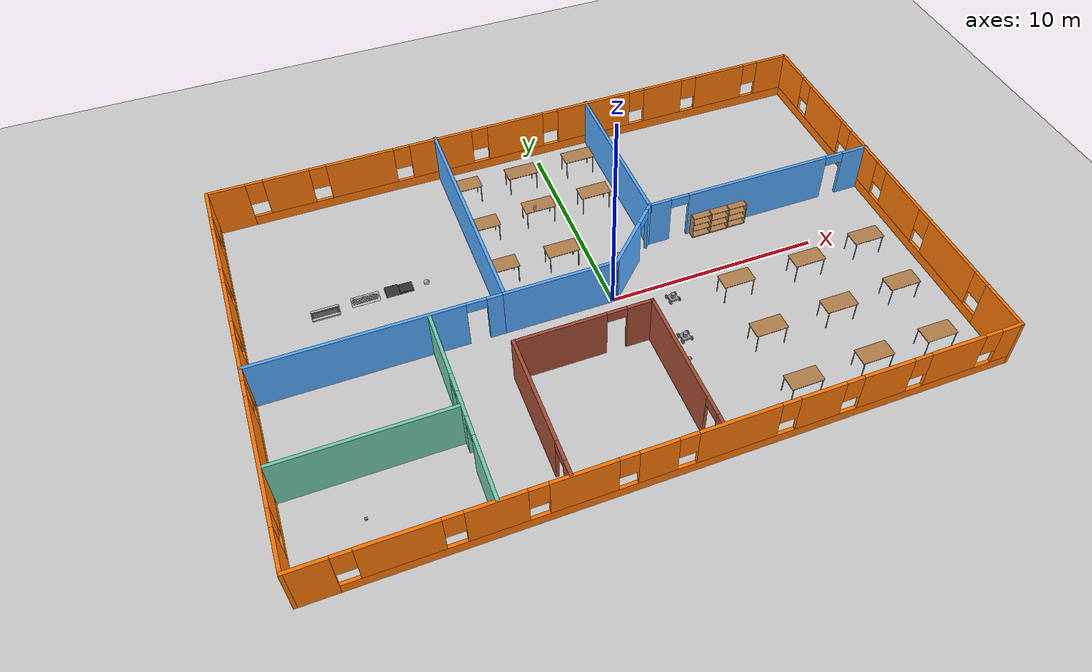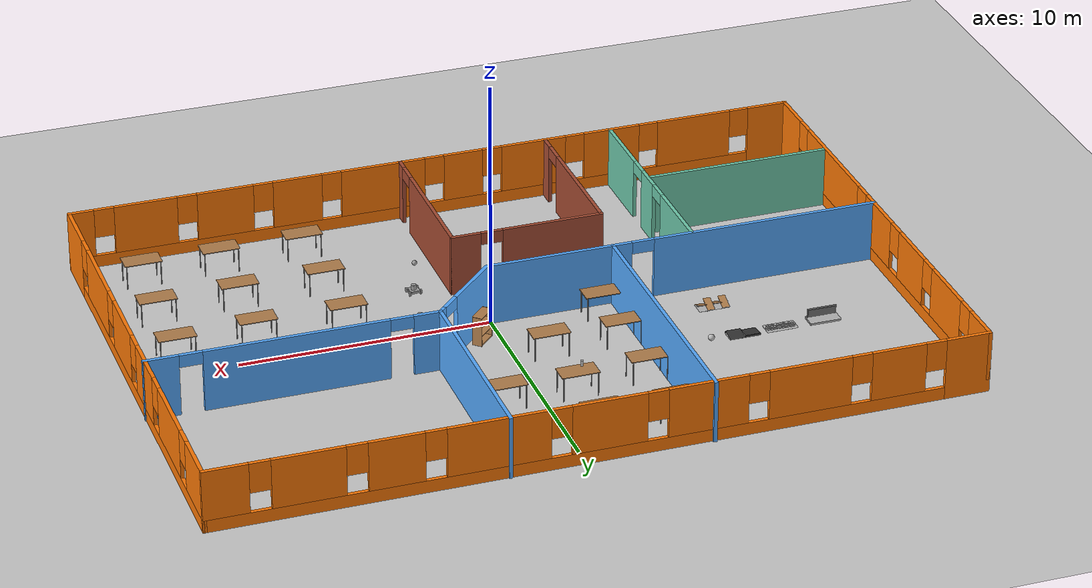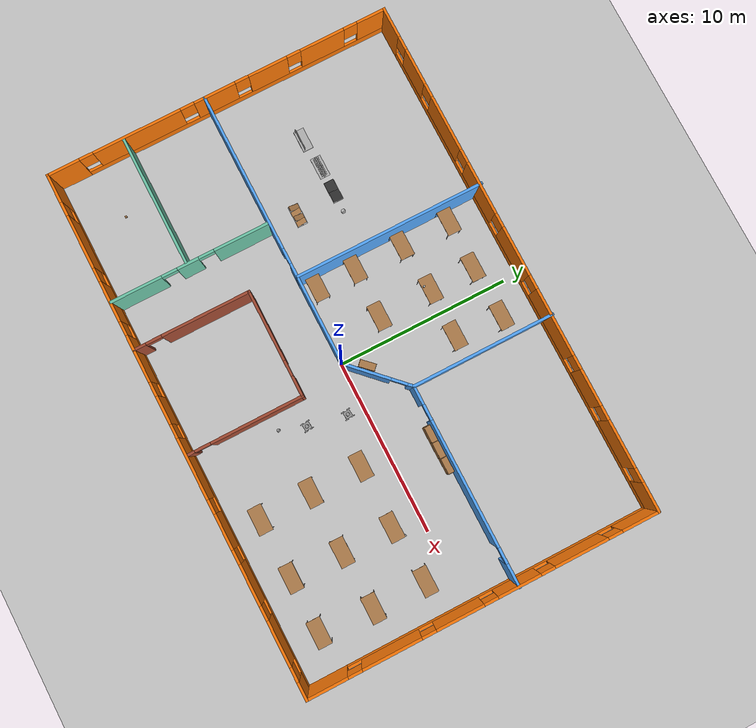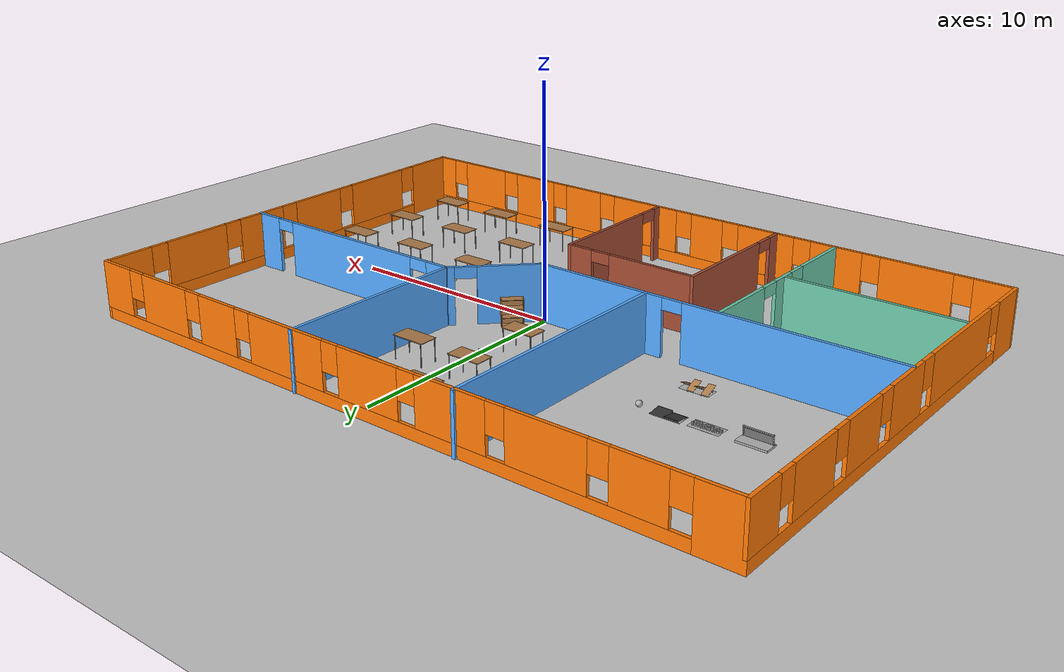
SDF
<sdf version="1.6">
 <world name="default">
  <light name="sun" type="directional">
   <pose>0 0 10 0 -0 0</pose>
   <diffuse>0.8 0.8 0.8 1</diffuse>
   <specular>0.2 0.2 0.2 1</specular>
   <attenuation>
    <range>1000</range>
    <constant>0.9</constant>
    <linear>0.01</linear>
    <quadratic>0.001</quadratic>
   </attenuation>
   <direction>-0.5 0.1 -0.9</direction>
   <spot><inner_angle>0</inner_angle><outer_angle>0</outer_angle><falloff>0</falloff></spot>
  </light>
  <model name="ground_plane">
   <static>1</static>
   <link name="link">
    <collision name="collision">
     <geometry><plane><normal>0 0 1</normal><size>100 100</size></plane></geometry>
     <surface>
      <contact><collide_bitmask>65535</collide_bitmask></contact>
      <friction><ode><mu>100</mu><mu2>50</mu2></ode></friction>
     </surface>
    </collision>
    <visual name="visual">
     <cast_shadows>0</cast_shadows>
     <geometry><plane><normal>0 0 1</normal><size>100 100</size></plane></geometry>
     <material>
      <script><uri>file://media/materials/scripts/gazebo.material</uri><name>Gazebo/Grey</name></script>
     </material>
    </visual>
   </link>
  </model>
  <gravity>0 0 -9.8</gravity>
  <magnetic_field>6e-06 2.3e-05 -4.2e-05</magnetic_field>
  <atmosphere type="adiabatic"/>
  <physics type="ode">
   <max_step_size>0.001</max_step_size>
   <real_time_factor>1</real_time_factor>
   <real_time_update_rate>1000</real_time_update_rate>
  </physics>
  <scene><ambient>0.4 0.4 0.4 1</ambient><background>0.7 0.7 0.7 1</background><shadows>1</shadows></scene>
  <spherical_coordinates>
   <surface_model>EARTH_WGS84</surface_model>
   <latitude_deg>0</latitude_deg>
   <longitude_deg>0</longitude_deg>
   <elevation>0</elevation>
   <heading_deg>0</heading_deg>
  </spherical_coordinates>
  <model name="building1">
   <pose>-0.784049 0.80046 0 0 -0 0</pose>
   <link name="Wall_0">
    <pose>-0.018158 -10.0416 0 0 -0 0</pose>
    <visual name="Wall_0_Visual_0">
     <pose>-14.2164 0 1.25 0 -0 0</pose>
     <geometry><box><size>1.7173 0.15 2.5</size></box></geometry>
     <material>
      <script><uri>file://media/materials/scripts/gazebo.material</uri><name>Gazebo/Grey</name></script>
      <ambient>0.996078 0.47451 0.0196078 1</ambient>
     </material>
     <meta><layer>0</layer></meta>
    </visual>
    <collision name="Wall_0_Collision_0">
     <geometry><box><size>1.7173 0.15 2.5</size></box></geometry>
     <pose>-14.2164 0 1.25 0 -0 0</pose>
    </collision>
    <visual name="Wall_0_Visual_1">
     <pose>0.858647 0 0.25 0 -0 0</pose>
     <geometry><box><size>28.4327 0.15 0.5</size></box></geometry>
     <material>
      <script><uri>file://media/materials/scripts/gazebo.material</uri><name>Gazebo/Grey</name></script>
      <ambient>0.996078 0.47451 0.0196078 1</ambient>
     </material>
     <meta><layer>0</layer></meta>
    </visual>
    <collision name="Wall_0_Collision_1">
     <geometry><box><size>28.4327 0.15 0.5</size></box></geometry>
     <pose>0.858647 0 0.25 0 -0 0</pose>
    </collision>
    <visual name="Wall_0_Visual_2">
     <pose>-10.9877 0 1.5 0 -0 0</pose>
     <geometry><box><size>3.14002 0.15 2</size></box></geometry>
     <material>
      <script><uri>file://media/materials/scripts/gazebo.material</uri><name>Gazebo/Grey</name></script>
      <ambient>0.996078 0.47451 0.0196078 1</ambient>
     </material>
     <meta><layer>0</layer></meta>
    </visual>
    <collision name="Wall_0_Collision_2">
     <geometry><box><size>3.14002 0.15 2</size></box></geometry>
     <pose>-10.9877 0 1.5 0 -0 0</pose>
    </collision>
    <visual name="Wall_0_Visual_3">
     <pose>-7.43464 0 1.5 0 -0 0</pose>
     <geometry><box><size>2.36609 0.15 2</size></box></geometry>
     <material>
      <script><uri>file://media/materials/scripts/gazebo.material</uri><name>Gazebo/Grey</name></script>
      <ambient>0.996078 0.47451 0.0196078 1</ambient>
     </material>
     <meta><layer>0</layer></meta>
    </visual>
    <collision name="Wall_0_Collision_3">
     <geometry><box><size>2.36609 0.15 2</size></box></geometry>
     <pose>-7.43464 0 1.5 0 -0 0</pose>
    </collision>
    <visual name="Wall_0_Visual_4">
     <pose>-4.08798 0 1.5 0 -0 0</pose>
     <geometry><box><size>2.72724 0.15 2</size></box></geometry>
     <material>
      <script><uri>file://media/materials/scripts/gazebo.material</uri><name>Gazebo/Grey</name></script>
      <ambient>0.996078 0.47451 0.0196078 1</ambient>
     </material>
     <meta><layer>0</layer></meta>
    </visual>
    <collision name="Wall_0_Collision_4">
     <geometry><box><size>2.72724 0.15 2</size></box></geometry>
     <pose>-4.08798 0 1.5 0 -0 0</pose>
    </collision>
    <visual name="Wall_0_Visual_5">
     <pose>-1.11069 0 1.5 0 -0 0</pose>
     <geometry><box><size>1.62733 0.15 2</size></box></geometry>
     <material>
      <script><uri>file://media/materials/scripts/gazebo.material</uri><name>Gazebo/Grey</name></script>
      <ambient>0.996078 0.47451 0.0196078 1</ambient>
     </material>
     <meta><layer>0</layer></meta>
    </visual>
    <collision name="Wall_0_Collision_5">
     <geometry><box><size>1.62733 0.15 2</size></box></geometry>
     <pose>-1.11069 0 1.5 0 -0 0</pose>
    </collision>
    <visual name="Wall_0_Visual_6">
     <pose>2.2442 0 1.5 0 -0 0</pose>
     <geometry><box><size>3.48244 0.15 2</size></box></geometry>
     <material>
      <script><uri>file://media/materials/scripts/gazebo.material</uri><name>Gazebo/Grey</name></script>
      <ambient>0.996078 0.47451 0.0196078 1</ambient>
     </material>
     <meta><layer>0</layer></meta>
    </visual>
    <collision name="Wall_0_Collision_6">
     <geometry><box><size>3.48244 0.15 2</size></box></geometry>
     <pose>2.2442 0 1.5 0 -0 0</pose>
    </collision>
    <visual name="Wall_0_Visual_7">
     <pose>5.79258 0 1.5 0 -0 0</pose>
     <geometry><box><size>2.0143 0.15 2</size></box></geometry>
     <material>
      <script><uri>file://media/materials/scripts/gazebo.material</uri><name>Gazebo/Grey</name></script>
      <ambient>0.996078 0.47451 0.0196078 1</ambient>
     </material>
     <meta><layer>0</layer></meta>
    </visual>
    <collision name="Wall_0_Collision_7">
     <geometry><box><size>2.0143 0.15 2</size></box></geometry>
     <pose>5.79258 0 1.5 0 -0 0</pose>
    </collision>
    <visual name="Wall_0_Visual_8">
     <pose>8.74759 0 1.5 0 -0 0</pose>
     <geometry><box><size>2.29573 0.15 2</size></box></geometry>
     <material>
      <script><uri>file://media/materials/scripts/gazebo.material</uri><name>Gazebo/Grey</name></script>
      <ambient>0.996078 0.47451 0.0196078 1</ambient>
     </material>
     <meta><layer>0</layer></meta>
    </visual>
    <collision name="Wall_0_Collision_8">
     <geometry><box><size>2.29573 0.15 2</size></box></geometry>
     <pose>8.74759 0 1.5 0 -0 0</pose>
    </collision>
    <visual name="Wall_0_Visual_9">
     <pose>11.9664 0 1.5 0 -0 0</pose>
     <geometry><box><size>2.54198 0.15 2</size></box></geometry>
     <material>
      <script><uri>file://media/materials/scripts/gazebo.material</uri><name>Gazebo/Grey</name></script>
      <ambient>0.996078 0.47451 0.0196078 1</ambient>
     </material>
     <meta><layer>0</layer></meta>
    </visual>
    <collision name="Wall_0_Collision_9">
     <geometry><box><size>2.54198 0.15 2</size></box></geometry>
     <pose>11.9664 0 1.5 0 -0 0</pose>
    </collision>
    <visual name="Wall_0_Visual_10">
     <pose>14.5562 0 1.5 0 -0 0</pose>
     <geometry><box><size>1.03756 0.15 2</size></box></geometry>
     <material>
      <script><uri>file://media/materials/scripts/gazebo.material</uri><name>Gazebo/Grey</name></script>
      <ambient>0.996078 0.47451 0.0196078 1</ambient>
     </material>
     <meta><layer>0</layer></meta>
    </visual>
    <collision name="Wall_0_Collision_10">
     <geometry><box><size>1.03756 0.15 2</size></box></geometry>
     <pose>14.5562 0 1.5 0 -0 0</pose>
    </collision>
    <visual name="Wall_0_Visual_11">
     <pose>-12.9577 0 1.9 0 -0 0</pose>
     <geometry><box><size>0.8 0.15 1.2</size></box></geometry>
     <material>
      <script><uri>file://media/materials/scripts/gazebo.material</uri><name>Gazebo/Grey</name></script>
      <ambient>0.996078 0.47451 0.0196078 1</ambient>
     </material>
     <meta><layer>0</layer></meta>
    </visual>
    <collision name="Wall_0_Collision_11">
     <geometry><box><size>0.8 0.15 1.2</size></box></geometry>
     <pose>-12.9577 0 1.9 0 -0 0</pose>
    </collision>
    <visual name="Wall_0_Visual_12">
     <pose>-9.01768 0 1.9 0 -0 0</pose>
     <geometry><box><size>0.8 0.15 1.2</size></box></geometry>
     <material>
      <script><uri>file://media/materials/scripts/gazebo.material</uri><name>Gazebo/Grey</name></script>
      <ambient>0.996078 0.47451 0.0196078 1</ambient>
     </material>
     <meta><layer>0</layer></meta>
    </visual>
    <collision name="Wall_0_Collision_12">
     <geometry><box><size>0.8 0.15 1.2</size></box></geometry>
     <pose>-9.01768 0 1.9 0 -0 0</pose>
    </collision>
    <visual name="Wall_0_Visual_13">
     <pose>-5.8516 0 1.9 0 -0 0</pose>
     <geometry><box><size>0.8 0.15 1.2</size></box></geometry>
     <material>
      <script><uri>file://media/materials/scripts/gazebo.material</uri><name>Gazebo/Grey</name></script>
      <ambient>0.996078 0.47451 0.0196078 1</ambient>
     </material>
     <meta><layer>0</layer></meta>
    </visual>
    <collision name="Wall_0_Collision_13">
     <geometry><box><size>0.8 0.15 1.2</size></box></geometry>
     <pose>-5.8516 0 1.9 0 -0 0</pose>
    </collision>
    <visual name="Wall_0_Visual_14">
     <pose>-2.32436 0 1.9 0 -0 0</pose>
     <geometry><box><size>0.8 0.15 1.2</size></box></geometry>
     <material>
      <script><uri>file://media/materials/scripts/gazebo.material</uri><name>Gazebo/Grey</name></script>
      <ambient>0.996078 0.47451 0.0196078 1</ambient>
     </material>
     <meta><layer>0</layer></meta>
    </visual>
    <collision name="Wall_0_Collision_14">
     <geometry><box><size>0.8 0.15 1.2</size></box></geometry>
     <pose>-2.32436 0 1.9 0 -0 0</pose>
    </collision>
    <visual name="Wall_0_Visual_15">
     <pose>0.10298 0 1.9 0 -0 0</pose>
     <geometry><box><size>0.8 0.15 1.2</size></box></geometry>
     <material>
      <script><uri>file://media/materials/scripts/gazebo.material</uri><name>Gazebo/Grey</name></script>
      <ambient>0.996078 0.47451 0.0196078 1</ambient>
     </material>
     <meta><layer>0</layer></meta>
    </visual>
    <collision name="Wall_0_Collision_15">
     <geometry><box><size>0.8 0.15 1.2</size></box></geometry>
     <pose>0.10298 0 1.9 0 -0 0</pose>
    </collision>
    <visual name="Wall_0_Visual_16">
     <pose>4.38542 0 1.9 0 -0 0</pose>
     <geometry><box><size>0.8 0.15 1.2</size></box></geometry>
     <material>
      <script><uri>file://media/materials/scripts/gazebo.material</uri><name>Gazebo/Grey</name></script>
      <ambient>0.996078 0.47451 0.0196078 1</ambient>
     </material>
     <meta><layer>0</layer></meta>
    </visual>
    <collision name="Wall_0_Collision_16">
     <geometry><box><size>0.8 0.15 1.2</size></box></geometry>
     <pose>4.38542 0 1.9 0 -0 0</pose>
    </collision>
    <visual name="Wall_0_Visual_17">
     <pose>7.19973 0 1.9 0 -0 0</pose>
     <geometry><box><size>0.8 0.15 1.2</size></box></geometry>
     <material>
      <script><uri>file://media/materials/scripts/gazebo.material</uri><name>Gazebo/Grey</name></script>
      <ambient>0.996078 0.47451 0.0196078 1</ambient>
     </material>
     <meta><layer>0</layer></meta>
    </visual>
    <collision name="Wall_0_Collision_17">
     <geometry><box><size>0.8 0.15 1.2</size></box></geometry>
     <pose>7.19973 0 1.9 0 -0 0</pose>
    </collision>
    <visual name="Wall_0_Visual_18">
     <pose>10.2955 0 1.9 0 -0 0</pose>
     <geometry><box><size>0.8 0.15 1.2</size></box></geometry>
     <material>
      <script><uri>file://media/materials/scripts/gazebo.material</uri><name>Gazebo/Grey</name></script>
      <ambient>0.996078 0.47451 0.0196078 1</ambient>
     </material>
     <meta><layer>0</layer></meta>
    </visual>
    <collision name="Wall_0_Collision_18">
     <geometry><box><size>0.8 0.15 1.2</size></box></geometry>
     <pose>10.2955 0 1.9 0 -0 0</pose>
    </collision>
    <visual name="Wall_0_Visual_19">
     <pose>13.6374 0 1.9 0 -0 0</pose>
     <geometry><box><size>0.8 0.15 1.2</size></box></geometry>
     <material>
      <script><uri>file://media/materials/scripts/gazebo.material</uri><name>Gazebo/Grey</name></script>
      <ambient>0.996078 0.47451 0.0196078 1</ambient>
     </material>
     <meta><layer>0</layer></meta>
    </visual>
    <collision name="Wall_0_Collision_19">
     <geometry><box><size>0.8 0.15 1.2</size></box></geometry>
     <pose>13.6374 0 1.9 0 -0 0</pose>
    </collision>
   </link>
   <link name="Wall_11">
    <pose>-7.3948 -5.44058 0 0 0 -1.5708</pose>
    <visual name="Wall_11_Visual_0">
     <pose>-3.01002 0 1.25 0 -0 0</pose>
     <geometry><box><size>3.22995 0.15 2.5</size></box></geometry>
     <material>
      <script><uri>file://media/materials/scripts/gazebo.material</uri><name>Gazebo/Grey</name></script>
      <ambient>0.435294 0.796078 0.67451 1</ambient>
     </material>
     <meta><layer>0</layer></meta>
    </visual>
    <collision name="Wall_11_Collision_0">
     <geometry><box><size>3.22995 0.15 2.5</size></box></geometry>
     <pose>-3.01002 0 1.25 0 -0 0</pose>
    </collision>
    <visual name="Wall_11_Visual_1">
     <pose>0.127027 0 1.25 0 -0 0</pose>
     <geometry><box><size>1.24415 0.15 2.5</size></box></geometry>
     <material>
      <script><uri>file://media/materials/scripts/gazebo.material</uri><name>Gazebo/Grey</name></script>
      <ambient>0.435294 0.796078 0.67451 1</ambient>
     </material>
     <meta><layer>0</layer></meta>
    </visual>
    <collision name="Wall_11_Collision_1">
     <geometry><box><size>1.24415 0.15 2.5</size></box></geometry>
     <pose>0.127027 0 1.25 0 -0 0</pose>
    </collision>
    <visual name="Wall_11_Visual_2">
     <pose>3.13705 0 1.25 0 -0 0</pose>
     <geometry><box><size>2.9759 0.15 2.5</size></box></geometry>
     <material>
      <script><uri>file://media/materials/scripts/gazebo.material</uri><name>Gazebo/Grey</name></script>
      <ambient>0.435294 0.796078 0.67451 1</ambient>
     </material>
     <meta><layer>0</layer></meta>
    </visual>
    <collision name="Wall_11_Collision_2">
     <geometry><box><size>2.9759 0.15 2.5</size></box></geometry>
     <pose>3.13705 0 1.25 0 -0 0</pose>
    </collision>
    <visual name="Wall_11_Visual_3">
     <pose>-0.945045 0 2.25 0 -0 0</pose>
     <geometry><box><size>0.9 0.15 0.5</size></box></geometry>
     <material>
      <script><uri>file://media/materials/scripts/gazebo.material</uri><name>Gazebo/Grey</name></script>
      <ambient>0.435294 0.796078 0.67451 1</ambient>
     </material>
     <meta><layer>0</layer></meta>
    </visual>
    <collision name="Wall_11_Collision_3">
     <geometry><box><size>0.9 0.15 0.5</size></box></geometry>
     <pose>-0.945045 0 2.25 0 -0 0</pose>
    </collision>
    <visual name="Wall_11_Visual_4">
     <pose>1.1991 0 2.25 0 -0 0</pose>
     <geometry><box><size>0.9 0.15 0.5</size></box></geometry>
     <material>
      <script><uri>file://media/materials/scripts/gazebo.material</uri><name>Gazebo/Grey</name></script>
      <ambient>0.435294 0.796078 0.67451 1</ambient>
     </material>
     <meta><layer>0</layer></meta>
    </visual>
    <collision name="Wall_11_Collision_4">
     <geometry><box><size>0.9 0.15 0.5</size></box></geometry>
     <pose>1.1991 0 2.25 0 -0 0</pose>
    </collision>
   </link>
   <link name="Wall_13">
    <collision name="Wall_13_Collision">
     <geometry><box><size>5.25 0.15 2.5</size></box></geometry>
     <pose>0 0 1.25 0 -0 0</pose>
    </collision>
    <visual name="Wall_13_Visual">
     <pose>0 0 1.25 0 -0 0</pose>
     <geometry><box><size>5.25 0.15 2.5</size></box></geometry>
     <material>
      <script><uri>file://media/materials/scripts/gazebo.material</uri><name>Gazebo/Grey</name></script>
      <ambient>0.333333 0.666667 1 1</ambient>
     </material>
     <meta><layer>0</layer></meta>
    </visual>
    <pose>-1.6042 -0.808364 0 0 -0 0</pose>
   </link>
   <link name="Wall_14">
    <pose>2.30698 0.552817 0 0 -0 0.785398</pose>
    <visual name="Wall_14_Visual_0">
     <pose>-0.648809 0 1.25 0 -0 0</pose>
     <geometry><box><size>2.70238 0.15 2.5</size></box></geometry>
     <material>
      <script><uri>file://media/materials/scripts/gazebo.material</uri><name>Gazebo/Grey</name></script>
      <ambient>0.333333 0.666667 1 1</ambient>
     </material>
     <meta><layer>0</layer></meta>
    </visual>
    <collision name="Wall_14_Collision_0">
     <geometry><box><size>2.70238 0.15 2.5</size></box></geometry>
     <pose>-0.648809 0 1.25 0 -0 0</pose>
    </collision>
    <visual name="Wall_14_Visual_1">
     <pose>1.80119 0 1.25 0 -0 0</pose>
     <geometry><box><size>0.397618 0.15 2.5</size></box></geometry>
     <material>
      <script><uri>file://media/materials/scripts/gazebo.material</uri><name>Gazebo/Grey</name></script>
      <ambient>0.333333 0.666667 1 1</ambient>
     </material>
     <meta><layer>0</layer></meta>
    </visual>
    <collision name="Wall_14_Collision_1">
     <geometry><box><size>0.397618 0.15 2.5</size></box></geometry>
     <pose>1.80119 0 1.25 0 -0 0</pose>
    </collision>
    <visual name="Wall_14_Visual_2">
     <pose>1.15238 0 2.25 0 -0 0</pose>
     <geometry><box><size>0.9 0.15 0.5</size></box></geometry>
     <material>
      <script><uri>file://media/materials/scripts/gazebo.material</uri><name>Gazebo/Grey</name></script>
      <ambient>0.333333 0.666667 1 1</ambient>
     </material>
     <meta><layer>0</layer></meta>
    </visual>
    <collision name="Wall_14_Collision_2">
     <geometry><box><size>0.9 0.15 0.5</size></box></geometry>
     <pose>1.15238 0 2.25 0 -0 0</pose>
    </collision>
   </link>
   <link name="Wall_15">
    <collision name="Wall_15_Collision">
     <geometry><box><size>8.25 0.15 2.5</size></box></geometry>
     <pose>0 0 1.25 0 -0 0</pose>
    </collision>
    <visual name="Wall_15_Visual">
     <pose>0 0 1.25 0 -0 0</pose>
     <geometry><box><size>8.25 0.15 2.5</size></box></geometry>
     <material>
      <script><uri>file://media/materials/scripts/gazebo.material</uri><name>Gazebo/Grey</name></script>
      <ambient>0.333333 0.666667 1 1</ambient>
     </material>
     <meta><layer>0</layer></meta>
    </visual>
    <pose>3.66816 5.964 0 0 -0 1.5708</pose>
   </link>
   <link name="Wall_17">
    <pose>9.34316 1.914 0 0 -0 0</pose>
    <visual name="Wall_17_Visual_0">
     <pose>-5.18047 0 1.25 0 -0 0</pose>
     <geometry><box><size>1.13906 0.15 2.5</size></box></geometry>
     <material>
      <script><uri>file://media/materials/scripts/gazebo.material</uri><name>Gazebo/Grey</name></script>
      <ambient>0.333333 0.666667 1 1</ambient>
     </material>
     <meta><layer>0</layer></meta>
    </visual>
    <collision name="Wall_17_Collision_0">
     <geometry><box><size>1.13906 0.15 2.5</size></box></geometry>
     <pose>-5.18047 0 1.25 0 -0 0</pose>
    </collision>
    <visual name="Wall_17_Visual_1">
     <pose>-0.115377 0 1.25 0 -0 0</pose>
     <geometry><box><size>7.19111 0.15 2.5</size></box></geometry>
     <material>
      <script><uri>file://media/materials/scripts/gazebo.material</uri><name>Gazebo/Grey</name></script>
      <ambient>0.333333 0.666667 1 1</ambient>
     </material>
     <meta><layer>0</layer></meta>
    </visual>
    <collision name="Wall_17_Collision_1">
     <geometry><box><size>7.19111 0.15 2.5</size></box></geometry>
     <pose>-0.115377 0 1.25 0 -0 0</pose>
    </collision>
    <visual name="Wall_17_Visual_2">
     <pose>5.06509 0 1.25 0 -0 0</pose>
     <geometry><box><size>1.36982 0.15 2.5</size></box></geometry>
     <material>
      <script><uri>file://media/materials/scripts/gazebo.material</uri><name>Gazebo/Grey</name></script>
      <ambient>0.333333 0.666667 1 1</ambient>
     </material>
     <meta><layer>0</layer></meta>
    </visual>
    <collision name="Wall_17_Collision_2">
     <geometry><box><size>1.36982 0.15 2.5</size></box></geometry>
     <pose>5.06509 0 1.25 0 -0 0</pose>
    </collision>
    <visual name="Wall_17_Visual_3">
     <pose>-4.16094 0 2.25 0 -0 0</pose>
     <geometry><box><size>0.9 0.15 0.5</size></box></geometry>
     <material>
      <script><uri>file://media/materials/scripts/gazebo.material</uri><name>Gazebo/Grey</name></script>
      <ambient>0.333333 0.666667 1 1</ambient>
     </material>
     <meta><layer>0</layer></meta>
    </visual>
    <collision name="Wall_17_Collision_3">
     <geometry><box><size>0.9 0.15 0.5</size></box></geometry>
     <pose>-4.16094 0 2.25 0 -0 0</pose>
    </collision>
    <visual name="Wall_17_Visual_4">
     <pose>3.93018 0 2.25 0 -0 0</pose>
     <geometry><box><size>0.9 0.15 0.5</size></box></geometry>
     <material>
      <script><uri>file://media/materials/scripts/gazebo.material</uri><name>Gazebo/Grey</name></script>
      <ambient>0.333333 0.666667 1 1</ambient>
     </material>
     <meta><layer>0</layer></meta>
    </visual>
    <collision name="Wall_17_Collision_4">
     <geometry><box><size>0.9 0.15 0.5</size></box></geometry>
     <pose>3.93018 0 2.25 0 -0 0</pose>
    </collision>
   </link>
   <link name="Wall_19">
    <collision name="Wall_19_Collision">
     <geometry><box><size>7.5 0.15 2.5</size></box></geometry>
     <pose>0 0 1.25 0 -0 0</pose>
    </collision>
    <visual name="Wall_19_Visual">
     <pose>0 0 1.25 0 -0 0</pose>
     <geometry><box><size>7.5 0.15 2.5</size></box></geometry>
     <material>
      <script><uri>file://media/materials/scripts/gazebo.material</uri><name>Gazebo/Grey</name></script>
      <ambient>0.435294 0.796078 0.67451 1</ambient>
     </material>
     <meta><layer>0</layer></meta>
    </visual>
    <pose>-11.1958 -5.62829 0 0 -0 3.14159</pose>
   </link>
   <link name="Wall_2">
    <pose>-15.0182 -0.041636 0 0 -0 1.5708</pose>
    <visual name="Wall_2_Visual_0">
     <pose>-9.11261 0 1.25 0 -0 0</pose>
     <geometry><box><size>1.92478 0.15 2.5</size></box></geometry>
     <material>
      <script><uri>file://media/materials/scripts/gazebo.material</uri><name>Gazebo/Grey</name></script>
      <ambient>0.996078 0.47451 0.0196078 1</ambient>
     </material>
     <meta><layer>0</layer></meta>
    </visual>
    <collision name="Wall_2_Collision_0">
     <geometry><box><size>1.92478 0.15 2.5</size></box></geometry>
     <pose>-9.11261 0 1.25 0 -0 0</pose>
    </collision>
    <visual name="Wall_2_Visual_1">
     <pose>0.962392 0 0.25 0 -0 0</pose>
     <geometry><box><size>18.2252 0.15 0.5</size></box></geometry>
     <material>
      <script><uri>file://media/materials/scripts/gazebo.material</uri><name>Gazebo/Grey</name></script>
      <ambient>0.996078 0.47451 0.0196078 1</ambient>
     </material>
     <meta><layer>0</layer></meta>
    </visual>
    <collision name="Wall_2_Collision_1">
     <geometry><box><size>18.2252 0.15 0.5</size></box></geometry>
     <pose>0.962392 0 0.25 0 -0 0</pose>
    </collision>
    <visual name="Wall_2_Visual_2">
     <pose>-4.77761 0 1.5 0 -0 0</pose>
     <geometry><box><size>5.14521 0.15 2</size></box></geometry>
     <material>
      <script><uri>file://media/materials/scripts/gazebo.material</uri><name>Gazebo/Grey</name></script>
      <ambient>0.996078 0.47451 0.0196078 1</ambient>
     </material>
     <meta><layer>0</layer></meta>
    </visual>
    <collision name="Wall_2_Collision_2">
     <geometry><box><size>5.14521 0.15 2</size></box></geometry>
     <pose>-4.77761 0 1.5 0 -0 0</pose>
    </collision>
    <visual name="Wall_2_Visual_3">
     <pose>-0.186783 0 1.5 0 -0 0</pose>
     <geometry><box><size>2.43645 0.15 2</size></box></geometry>
     <material>
      <script><uri>file://media/materials/scripts/gazebo.material</uri><name>Gazebo/Grey</name></script>
      <ambient>0.996078 0.47451 0.0196078 1</ambient>
     </material>
     <meta><layer>0</layer></meta>
    </visual>
    <collision name="Wall_2_Collision_3">
     <geometry><box><size>2.43645 0.15 2</size></box></geometry>
     <pose>-0.186783 0 1.5 0 -0 0</pose>
    </collision>
    <visual name="Wall_2_Visual_4">
     <pose>2.97931 0 1.5 0 -0 0</pose>
     <geometry><box><size>2.29573 0.15 2</size></box></geometry>
     <material>
      <script><uri>file://media/materials/scripts/gazebo.material</uri><name>Gazebo/Grey</name></script>
      <ambient>0.996078 0.47451 0.0196078 1</ambient>
     </material>
     <meta><layer>0</layer></meta>
    </visual>
    <collision name="Wall_2_Collision_4">
     <geometry><box><size>2.29573 0.15 2</size></box></geometry>
     <pose>2.97931 0 1.5 0 -0 0</pose>
    </collision>
    <visual name="Wall_2_Visual_5">
     <pose>6.23334 0 1.5 0 -0 0</pose>
     <geometry><box><size>2.61234 0.15 2</size></box></geometry>
     <material>
      <script><uri>file://media/materials/scripts/gazebo.material</uri><name>Gazebo/Grey</name></script>
      <ambient>0.996078 0.47451 0.0196078 1</ambient>
     </material>
     <meta><layer>0</layer></meta>
    </visual>
    <collision name="Wall_2_Collision_5">
     <geometry><box><size>2.61234 0.15 2</size></box></geometry>
     <pose>6.23334 0 1.5 0 -0 0</pose>
    </collision>
    <visual name="Wall_2_Visual_6">
     <pose>9.20726 0 1.5 0 -0 0</pose>
     <geometry><box><size>1.73549 0.15 2</size></box></geometry>
     <material>
      <script><uri>file://media/materials/scripts/gazebo.material</uri><name>Gazebo/Grey</name></script>
      <ambient>0.996078 0.47451 0.0196078 1</ambient>
     </material>
     <meta><layer>0</layer></meta>
    </visual>
    <collision name="Wall_2_Collision_6">
     <geometry><box><size>1.73549 0.15 2</size></box></geometry>
     <pose>9.20726 0 1.5 0 -0 0</pose>
    </collision>
    <visual name="Wall_2_Visual_7">
     <pose>-7.75022 0 1.9 0 -0 0</pose>
     <geometry><box><size>0.8 0.15 1.2</size></box></geometry>
     <material>
      <script><uri>file://media/materials/scripts/gazebo.material</uri><name>Gazebo/Grey</name></script>
      <ambient>0.996078 0.47451 0.0196078 1</ambient>
     </material>
     <meta><layer>0</layer></meta>
    </visual>
    <collision name="Wall_2_Collision_7">
     <geometry><box><size>0.8 0.15 1.2</size></box></geometry>
     <pose>-7.75022 0 1.9 0 -0 0</pose>
    </collision>
    <visual name="Wall_2_Visual_8">
     <pose>-1.80501 0 1.9 0 -0 0</pose>
     <geometry><box><size>0.8 0.15 1.2</size></box></geometry>
     <material>
      <script><uri>file://media/materials/scripts/gazebo.material</uri><name>Gazebo/Grey</name></script>
      <ambient>0.996078 0.47451 0.0196078 1</ambient>
     </material>
     <meta><layer>0</layer></meta>
    </visual>
    <collision name="Wall_2_Collision_8">
     <geometry><box><size>0.8 0.15 1.2</size></box></geometry>
     <pose>-1.80501 0 1.9 0 -0 0</pose>
    </collision>
    <visual name="Wall_2_Visual_9">
     <pose>1.43144 0 1.9 0 -0 0</pose>
     <geometry><box><size>0.8 0.15 1.2</size></box></geometry>
     <material>
      <script><uri>file://media/materials/scripts/gazebo.material</uri><name>Gazebo/Grey</name></script>
      <ambient>0.996078 0.47451 0.0196078 1</ambient>
     </material>
     <meta><layer>0</layer></meta>
    </visual>
    <collision name="Wall_2_Collision_9">
     <geometry><box><size>0.8 0.15 1.2</size></box></geometry>
     <pose>1.43144 0 1.9 0 -0 0</pose>
    </collision>
    <visual name="Wall_2_Visual_10">
     <pose>4.52717 0 1.9 0 -0 0</pose>
     <geometry><box><size>0.8 0.15 1.2</size></box></geometry>
     <material>
      <script><uri>file://media/materials/scripts/gazebo.material</uri><name>Gazebo/Grey</name></script>
      <ambient>0.996078 0.47451 0.0196078 1</ambient>
     </material>
     <meta><layer>0</layer></meta>
    </visual>
    <collision name="Wall_2_Collision_10">
     <geometry><box><size>0.8 0.15 1.2</size></box></geometry>
     <pose>4.52717 0 1.9 0 -0 0</pose>
    </collision>
    <visual name="Wall_2_Visual_11">
     <pose>7.93951 0 1.9 0 -0 0</pose>
     <geometry><box><size>0.8 0.15 1.2</size></box></geometry>
     <material>
      <script><uri>file://media/materials/scripts/gazebo.material</uri><name>Gazebo/Grey</name></script>
      <ambient>0.996078 0.47451 0.0196078 1</ambient>
     </material>
     <meta><layer>0</layer></meta>
    </visual>
    <collision name="Wall_2_Collision_11">
     <geometry><box><size>0.8 0.15 1.2</size></box></geometry>
     <pose>7.93951 0 1.9 0 -0 0</pose>
    </collision>
   </link>
   <link name="Wall_23">
    <pose>-4.60803 -6.6975 0 0 -0 1.5708</pose>
    <visual name="Wall_23_Visual_0">
     <pose>-3.01635 0 1.25 0 -0 0</pose>
     <geometry><box><size>0.717301 0.15 2.5</size></box></geometry>
     <material>
      <script><uri>file://media/materials/scripts/gazebo.material</uri><name>Gazebo/Bricks</name></script>
      <ambient>0.435294 0.796078 0.67451 1</ambient>
     </material>
     <meta><layer>0</layer></meta>
    </visual>
    <collision name="Wall_23_Collision_0">
     <geometry><box><size>0.717301 0.15 2.5</size></box></geometry>
     <pose>-3.01635 0 1.25 0 -0 0</pose>
    </collision>
    <visual name="Wall_23_Visual_1">
     <pose>0.80865 0 1.25 0 -0 0</pose>
     <geometry><box><size>5.1327 0.15 2.5</size></box></geometry>
     <material>
      <script><uri>file://media/materials/scripts/gazebo.material</uri><name>Gazebo/Bricks</name></script>
      <ambient>0.435294 0.796078 0.67451 1</ambient>
     </material>
     <meta><layer>0</layer></meta>
    </visual>
    <collision name="Wall_23_Collision_1">
     <geometry><box><size>5.1327 0.15 2.5</size></box></geometry>
     <pose>0.80865 0 1.25 0 -0 0</pose>
    </collision>
    <visual name="Wall_23_Visual_2">
     <pose>-2.2077 0 2.25 0 -0 0</pose>
     <geometry><box><size>0.9 0.15 0.5</size></box></geometry>
     <material>
      <script><uri>file://media/materials/scripts/gazebo.material</uri><name>Gazebo/Bricks</name></script>
      <ambient>0.435294 0.796078 0.67451 1</ambient>
     </material>
     <meta><layer>0</layer></meta>
    </visual>
    <collision name="Wall_23_Collision_2">
     <geometry><box><size>0.9 0.15 0.5</size></box></geometry>
     <pose>-2.2077 0 2.25 0 -0 0</pose>
    </collision>
   </link>
   <link name="Wall_24">
    <pose>-1.55802 -3.3975 0 0 -0 0</pose>
    <visual name="Wall_24_Visual_0">
     <pose>-1.06722 0 1.25 0 -0 0</pose>
     <geometry><box><size>4.11557 0.15 2.5</size></box></geometry>
     <material>
      <script><uri>file://media/materials/scripts/gazebo.material</uri><name>Gazebo/Bricks</name></script>
      <ambient>0.435294 0.796078 0.67451 1</ambient>
     </material>
     <meta><layer>0</layer></meta>
    </visual>
    <collision name="Wall_24_Collision_0">
     <geometry><box><size>4.11557 0.15 2.5</size></box></geometry>
     <pose>-1.06722 0 1.25 0 -0 0</pose>
    </collision>
    <visual name="Wall_24_Visual_1">
     <pose>2.50779 0 1.25 0 -0 0</pose>
     <geometry><box><size>1.23443 0.15 2.5</size></box></geometry>
     <material>
      <script><uri>file://media/materials/scripts/gazebo.material</uri><name>Gazebo/Bricks</name></script>
      <ambient>0.435294 0.796078 0.67451 1</ambient>
     </material>
     <meta><layer>0</layer></meta>
    </visual>
    <collision name="Wall_24_Collision_1">
     <geometry><box><size>1.23443 0.15 2.5</size></box></geometry>
     <pose>2.50779 0 1.25 0 -0 0</pose>
    </collision>
    <visual name="Wall_24_Visual_2">
     <pose>1.44057 0 2.25 0 -0 0</pose>
     <geometry><box><size>0.9 0.15 0.5</size></box></geometry>
     <material>
      <script><uri>file://media/materials/scripts/gazebo.material</uri><name>Gazebo/Bricks</name></script>
      <ambient>0.435294 0.796078 0.67451 1</ambient>
     </material>
     <meta><layer>0</layer></meta>
    </visual>
    <collision name="Wall_24_Collision_2">
     <geometry><box><size>0.9 0.15 0.5</size></box></geometry>
     <pose>1.44057 0 2.25 0 -0 0</pose>
    </collision>
   </link>
   <link name="Wall_25">
    <pose>1.49197 -6.6975 0 0 0 -1.5708</pose>
    <visual name="Wall_25_Visual_0">
     <pose>-0.707511 0 1.25 0 -0 0</pose>
     <geometry><box><size>5.33498 0.15 2.5</size></box></geometry>
     <material>
      <script><uri>file://media/materials/scripts/gazebo.material</uri><name>Gazebo/Bricks</name></script>
      <ambient>0.435294 0.796078 0.67451 1</ambient>
     </material>
     <meta><layer>0</layer></meta>
    </visual>
    <collision name="Wall_25_Collision_0">
     <geometry><box><size>5.33498 0.15 2.5</size></box></geometry>
     <pose>-0.707511 0 1.25 0 -0 0</pose>
    </collision>
    <visual name="Wall_25_Visual_1">
     <pose>3.11749 0 1.25 0 -0 0</pose>
     <geometry><box><size>0.515023 0.15 2.5</size></box></geometry>
     <material>
      <script><uri>file://media/materials/scripts/gazebo.material</uri><name>Gazebo/Bricks</name></script>
      <ambient>0.435294 0.796078 0.67451 1</ambient>
     </material>
     <meta><layer>0</layer></meta>
    </visual>
    <collision name="Wall_25_Collision_1">
     <geometry><box><size>0.515023 0.15 2.5</size></box></geometry>
     <pose>3.11749 0 1.25 0 -0 0</pose>
    </collision>
    <visual name="Wall_25_Visual_2">
     <pose>2.40998 0 2.25 0 -0 0</pose>
     <geometry><box><size>0.9 0.15 0.5</size></box></geometry>
     <material>
      <script><uri>file://media/materials/scripts/gazebo.material</uri><name>Gazebo/Bricks</name></script>
      <ambient>0.435294 0.796078 0.67451 1</ambient>
     </material>
     <meta><layer>0</layer></meta>
    </visual>
    <collision name="Wall_25_Collision_2">
     <geometry><box><size>0.9 0.15 0.5</size></box></geometry>
     <pose>2.40998 0 2.25 0 -0 0</pose>
    </collision>
   </link>
   <link name="Wall_4">
    <pose>-0.018158 9.95836 0 0 -0 0</pose>
    <visual name="Wall_4_Visual_0">
     <pose>-14.1636 0 1.25 0 -0 0</pose>
     <geometry><box><size>1.82283 0.15 2.5</size></box></geometry>
     <material>
      <script><uri>file://media/materials/scripts/gazebo.material</uri><name>Gazebo/Grey</name></script>
      <ambient>0.996078 0.47451 0.0196078 1</ambient>
     </material>
     <meta><layer>0</layer></meta>
    </visual>
    <collision name="Wall_4_Collision_0">
     <geometry><box><size>1.82283 0.15 2.5</size></box></geometry>
     <pose>-14.1636 0 1.25 0 -0 0</pose>
    </collision>
    <visual name="Wall_4_Visual_1">
     <pose>0.911415 0 0.25 0 -0 0</pose>
     <geometry><box><size>28.3272 0.15 0.5</size></box></geometry>
     <material>
      <script><uri>file://media/materials/scripts/gazebo.material</uri><name>Gazebo/Grey</name></script>
      <ambient>0.996078 0.47451 0.0196078 1</ambient>
     </material>
     <meta><layer>0</layer></meta>
    </visual>
    <collision name="Wall_4_Collision_1">
     <geometry><box><size>28.3272 0.15 0.5</size></box></geometry>
     <pose>0.911415 0 0.25 0 -0 0</pose>
    </collision>
    <visual name="Wall_4_Visual_2">
     <pose>-11.3747 0 1.5 0 -0 0</pose>
     <geometry><box><size>2.15502 0.15 2</size></box></geometry>
     <material>
      <script><uri>file://media/materials/scripts/gazebo.material</uri><name>Gazebo/Grey</name></script>
      <ambient>0.996078 0.47451 0.0196078 1</ambient>
     </material>
     <meta><layer>0</layer></meta>
    </visual>
    <collision name="Wall_4_Collision_2">
     <geometry><box><size>2.15502 0.15 2</size></box></geometry>
     <pose>-11.3747 0 1.5 0 -0 0</pose>
    </collision>
    <visual name="Wall_4_Visual_3">
     <pose>-7.87437 0 1.5 0 -0 0</pose>
     <geometry><box><size>3.24556 0.15 2</size></box></geometry>
     <material>
      <script><uri>file://media/materials/scripts/gazebo.material</uri><name>Gazebo/Grey</name></script>
      <ambient>0.996078 0.47451 0.0196078 1</ambient>
     </material>
     <meta><layer>0</layer></meta>
    </visual>
    <collision name="Wall_4_Collision_3">
     <geometry><box><size>3.24556 0.15 2</size></box></geometry>
     <pose>-7.87437 0 1.5 0 -0 0</pose>
    </collision>
    <visual name="Wall_4_Visual_4">
     <pose>-3.89917 0 1.5 0 -0 0</pose>
     <geometry><box><size>3.10484 0.15 2</size></box></geometry>
     <material>
      <script><uri>file://media/materials/scripts/gazebo.material</uri><name>Gazebo/Grey</name></script>
      <ambient>0.996078 0.47451 0.0196078 1</ambient>
     </material>
     <meta><layer>0</layer></meta>
    </visual>
    <collision name="Wall_4_Collision_4">
     <geometry><box><size>3.10484 0.15 2</size></box></geometry>
     <pose>-3.89917 0 1.5 0 -0 0</pose>
    </collision>
    <visual name="Wall_4_Visual_5">
     <pose>-0.099868 0 1.5 0 -0 0</pose>
     <geometry><box><size>2.89377 0.15 2</size></box></geometry>
     <material>
      <script><uri>file://media/materials/scripts/gazebo.material</uri><name>Gazebo/Grey</name></script>
      <ambient>0.996078 0.47451 0.0196078 1</ambient>
     </material>
     <meta><layer>0</layer></meta>
    </visual>
    <collision name="Wall_4_Collision_5">
     <geometry><box><size>2.89377 0.15 2</size></box></geometry>
     <pose>-0.099868 0 1.5 0 -0 0</pose>
    </collision>
    <visual name="Wall_4_Visual_6">
     <pose>4.10399 0 1.5 0 -0 0</pose>
     <geometry><box><size>3.91395 0.15 2</size></box></geometry>
     <material>
      <script><uri>file://media/materials/scripts/gazebo.material</uri><name>Gazebo/Grey</name></script>
      <ambient>0.996078 0.47451 0.0196078 1</ambient>
     </material>
     <meta><layer>0</layer></meta>
    </visual>
    <collision name="Wall_4_Collision_6">
     <geometry><box><size>3.91395 0.15 2</size></box></geometry>
     <pose>4.10399 0 1.5 0 -0 0</pose>
    </collision>
    <visual name="Wall_4_Visual_7">
     <pose>7.92089 0 1.5 0 -0 0</pose>
     <geometry><box><size>2.11984 0.15 2</size></box></geometry>
     <material>
      <script><uri>file://media/materials/scripts/gazebo.material</uri><name>Gazebo/Grey</name></script>
      <ambient>0.996078 0.47451 0.0196078 1</ambient>
     </material>
     <meta><layer>0</layer></meta>
    </visual>
    <collision name="Wall_4_Collision_7">
     <geometry><box><size>2.11984 0.15 2</size></box></geometry>
     <pose>7.92089 0 1.5 0 -0 0</pose>
    </collision>
    <visual name="Wall_4_Visual_8">
     <pose>11.1573 0 1.5 0 -0 0</pose>
     <geometry><box><size>2.75305 0.15 2</size></box></geometry>
     <material>
      <script><uri>file://media/materials/scripts/gazebo.material</uri><name>Gazebo/Grey</name></script>
      <ambient>0.996078 0.47451 0.0196078 1</ambient>
     </material>
     <meta><layer>0</layer></meta>
    </visual>
    <collision name="Wall_4_Collision_8">
     <geometry><box><size>2.75305 0.15 2</size></box></geometry>
     <pose>11.1573 0 1.5 0 -0 0</pose>
    </collision>
    <visual name="Wall_4_Visual_9">
     <pose>14.2044 0 1.5 0 -0 0</pose>
     <geometry><box><size>1.74114 0.15 2</size></box></geometry>
     <material>
      <script><uri>file://media/materials/scripts/gazebo.material</uri><name>Gazebo/Grey</name></script>
      <ambient>0.996078 0.47451 0.0196078 1</ambient>
     </material>
     <meta><layer>0</layer></meta>
    </visual>
    <collision name="Wall_4_Collision_9">
     <geometry><box><size>1.74114 0.15 2</size></box></geometry>
     <pose>14.2044 0 1.5 0 -0 0</pose>
    </collision>
    <visual name="Wall_4_Visual_10">
     <pose>-12.8522 0 1.9 0 -0 0</pose>
     <geometry><box><size>0.8 0.15 1.2</size></box></geometry>
     <material>
      <script><uri>file://media/materials/scripts/gazebo.material</uri><name>Gazebo/Grey</name></script>
      <ambient>0.996078 0.47451 0.0196078 1</ambient>
     </material>
     <meta><layer>0</layer></meta>
    </visual>
    <collision name="Wall_4_Collision_10">
     <geometry><box><size>0.8 0.15 1.2</size></box></geometry>
     <pose>-12.8522 0 1.9 0 -0 0</pose>
    </collision>
    <visual name="Wall_4_Visual_11">
     <pose>-9.89715 0 1.9 0 -0 0</pose>
     <geometry><box><size>0.8 0.15 1.2</size></box></geometry>
     <material>
      <script><uri>file://media/materials/scripts/gazebo.material</uri><name>Gazebo/Grey</name></script>
      <ambient>0.996078 0.47451 0.0196078 1</ambient>
     </material>
     <meta><layer>0</layer></meta>
    </visual>
    <collision name="Wall_4_Collision_11">
     <geometry><box><size>0.8 0.15 1.2</size></box></geometry>
     <pose>-9.89715 0 1.9 0 -0 0</pose>
    </collision>
    <visual name="Wall_4_Visual_12">
     <pose>-5.8516 0 1.9 0 -0 0</pose>
     <geometry><box><size>0.8 0.15 1.2</size></box></geometry>
     <material>
      <script><uri>file://media/materials/scripts/gazebo.material</uri><name>Gazebo/Grey</name></script>
      <ambient>0.996078 0.47451 0.0196078 1</ambient>
     </material>
     <meta><layer>0</layer></meta>
    </visual>
    <collision name="Wall_4_Collision_12">
     <geometry><box><size>0.8 0.15 1.2</size></box></geometry>
     <pose>-5.8516 0 1.9 0 -0 0</pose>
    </collision>
    <visual name="Wall_4_Visual_13">
     <pose>-1.94675 0 1.9 0 -0 0</pose>
     <geometry><box><size>0.8 0.15 1.2</size></box></geometry>
     <material>
      <script><uri>file://media/materials/scripts/gazebo.material</uri><name>Gazebo/Grey</name></script>
      <ambient>0.996078 0.47451 0.0196078 1</ambient>
     </material>
     <meta><layer>0</layer></meta>
    </visual>
    <collision name="Wall_4_Collision_13">
     <geometry><box><size>0.8 0.15 1.2</size></box></geometry>
     <pose>-1.94675 0 1.9 0 -0 0</pose>
    </collision>
    <visual name="Wall_4_Visual_14">
     <pose>1.74702 0 1.9 0 -0 0</pose>
     <geometry><box><size>0.8 0.15 1.2</size></box></geometry>
     <material>
      <script><uri>file://media/materials/scripts/gazebo.material</uri><name>Gazebo/Grey</name></script>
      <ambient>0.996078 0.47451 0.0196078 1</ambient>
     </material>
     <meta><layer>0</layer></meta>
    </visual>
    <collision name="Wall_4_Collision_14">
     <geometry><box><size>0.8 0.15 1.2</size></box></geometry>
     <pose>1.74702 0 1.9 0 -0 0</pose>
    </collision>
    <visual name="Wall_4_Visual_15">
     <pose>6.46097 0 1.9 0 -0 0</pose>
     <geometry><box><size>0.8 0.15 1.2</size></box></geometry>
     <material>
      <script><uri>file://media/materials/scripts/gazebo.material</uri><name>Gazebo/Grey</name></script>
      <ambient>0.996078 0.47451 0.0196078 1</ambient>
     </material>
     <meta><layer>0</layer></meta>
    </visual>
    <collision name="Wall_4_Collision_15">
     <geometry><box><size>0.8 0.15 1.2</size></box></geometry>
     <pose>6.46097 0 1.9 0 -0 0</pose>
    </collision>
    <visual name="Wall_4_Visual_16">
     <pose>9.38081 0 1.9 0 -0 0</pose>
     <geometry><box><size>0.8 0.15 1.2</size></box></geometry>
     <material>
      <script><uri>file://media/materials/scripts/gazebo.material</uri><name>Gazebo/Grey</name></script>
      <ambient>0.996078 0.47451 0.0196078 1</ambient>
     </material>
     <meta><layer>0</layer></meta>
    </visual>
    <collision name="Wall_4_Collision_16">
     <geometry><box><size>0.8 0.15 1.2</size></box></geometry>
     <pose>9.38081 0 1.9 0 -0 0</pose>
    </collision>
    <visual name="Wall_4_Visual_17">
     <pose>12.9339 0 1.9 0 -0 0</pose>
     <geometry><box><size>0.8 0.15 1.2</size></box></geometry>
     <material>
      <script><uri>file://media/materials/scripts/gazebo.material</uri><name>Gazebo/Grey</name></script>
      <ambient>0.996078 0.47451 0.0196078 1</ambient>
     </material>
     <meta><layer>0</layer></meta>
    </visual>
    <collision name="Wall_4_Collision_17">
     <geometry><box><size>0.8 0.15 1.2</size></box></geometry>
     <pose>12.9339 0 1.9 0 -0 0</pose>
    </collision>
   </link>
   <link name="Wall_6">
    <pose>14.9818 -0.041636 0 0 -0 1.5708</pose>
    <visual name="Wall_6_Visual_0">
     <pose>-8.88395 0 1.25 0 -0 0</pose>
     <geometry><box><size>2.38211 0.15 2.5</size></box></geometry>
     <material>
      <script><uri>file://media/materials/scripts/gazebo.material</uri><name>Gazebo/Grey</name></script>
      <ambient>0.996078 0.47451 0.0196078 1</ambient>
     </material>
     <meta><layer>0</layer></meta>
    </visual>
    <collision name="Wall_6_Collision_0">
     <geometry><box><size>2.38211 0.15 2.5</size></box></geometry>
     <pose>-8.88395 0 1.25 0 -0 0</pose>
    </collision>
    <visual name="Wall_6_Visual_1">
     <pose>1.19105 0 0.25 0 -0 0</pose>
     <geometry><box><size>17.7679 0.15 0.5</size></box></geometry>
     <material>
      <script><uri>file://media/materials/scripts/gazebo.material</uri><name>Gazebo/Grey</name></script>
      <ambient>0.996078 0.47451 0.0196078 1</ambient>
     </material>
     <meta><layer>0</layer></meta>
    </visual>
    <collision name="Wall_6_Collision_1">
     <geometry><box><size>17.7679 0.15 0.5</size></box></geometry>
     <pose>1.19105 0 0.25 0 -0 0</pose>
    </collision>
    <visual name="Wall_6_Visual_2">
     <pose>-5.21735 0 1.5 0 -0 0</pose>
     <geometry><box><size>3.35109 0.15 2</size></box></geometry>
     <material>
      <script><uri>file://media/materials/scripts/gazebo.material</uri><name>Gazebo/Grey</name></script>
      <ambient>0.996078 0.47451 0.0196078 1</ambient>
     </material>
     <meta><layer>0</layer></meta>
    </visual>
    <collision name="Wall_6_Collision_2">
     <geometry><box><size>3.35109 0.15 2</size></box></geometry>
     <pose>-5.21735 0 1.5 0 -0 0</pose>
    </collision>
    <visual name="Wall_6_Visual_3">
     <pose>-1.38286 0 1.5 0 -0 0</pose>
     <geometry><box><size>2.71788 0.15 2</size></box></geometry>
     <material>
      <script><uri>file://media/materials/scripts/gazebo.material</uri><name>Gazebo/Grey</name></script>
      <ambient>0.996078 0.47451 0.0196078 1</ambient>
     </material>
     <meta><layer>0</layer></meta>
    </visual>
    <collision name="Wall_6_Collision_3">
     <geometry><box><size>2.71788 0.15 2</size></box></geometry>
     <pose>-1.38286 0 1.5 0 -0 0</pose>
    </collision>
    <visual name="Wall_6_Visual_4">
     <pose>1.9943 0 1.5 0 -0 0</pose>
     <geometry><box><size>2.43645 0.15 2</size></box></geometry>
     <material>
      <script><uri>file://media/materials/scripts/gazebo.material</uri><name>Gazebo/Grey</name></script>
      <ambient>0.996078 0.47451 0.0196078 1</ambient>
     </material>
     <meta><layer>0</layer></meta>
    </visual>
    <collision name="Wall_6_Collision_4">
     <geometry><box><size>2.43645 0.15 2</size></box></geometry>
     <pose>1.9943 0 1.5 0 -0 0</pose>
    </collision>
    <visual name="Wall_6_Visual_5">
     <pose>5.54735 0 1.5 0 -0 0</pose>
     <geometry><box><size>3.06966 0.15 2</size></box></geometry>
     <material>
      <script><uri>file://media/materials/scripts/gazebo.material</uri><name>Gazebo/Grey</name></script>
      <ambient>0.996078 0.47451 0.0196078 1</ambient>
     </material>
     <meta><layer>0</layer></meta>
    </visual>
    <collision name="Wall_6_Collision_5">
     <geometry><box><size>3.06966 0.15 2</size></box></geometry>
     <pose>5.54735 0 1.5 0 -0 0</pose>
    </collision>
    <visual name="Wall_6_Visual_6">
     <pose>8.97859 0 1.5 0 -0 0</pose>
     <geometry><box><size>2.19281 0.15 2</size></box></geometry>
     <material>
      <script><uri>file://media/materials/scripts/gazebo.material</uri><name>Gazebo/Grey</name></script>
      <ambient>0.996078 0.47451 0.0196078 1</ambient>
     </material>
     <meta><layer>0</layer></meta>
    </visual>
    <collision name="Wall_6_Collision_6">
     <geometry><box><size>2.19281 0.15 2</size></box></geometry>
     <pose>8.97859 0 1.5 0 -0 0</pose>
    </collision>
    <visual name="Wall_6_Visual_7">
     <pose>-7.29289 0 1.9 0 -0 0</pose>
     <geometry><box><size>0.8 0.15 1.2</size></box></geometry>
     <material>
      <script><uri>file://media/materials/scripts/gazebo.material</uri><name>Gazebo/Grey</name></script>
      <ambient>0.996078 0.47451 0.0196078 1</ambient>
     </material>
     <meta><layer>0</layer></meta>
    </visual>
    <collision name="Wall_6_Collision_7">
     <geometry><box><size>0.8 0.15 1.2</size></box></geometry>
     <pose>-7.29289 0 1.9 0 -0 0</pose>
    </collision>
    <visual name="Wall_6_Visual_8">
     <pose>-3.1418 0 1.9 0 -0 0</pose>
     <geometry><box><size>0.8 0.15 1.2</size></box></geometry>
     <material>
      <script><uri>file://media/materials/scripts/gazebo.material</uri><name>Gazebo/Grey</name></script>
      <ambient>0.996078 0.47451 0.0196078 1</ambient>
     </material>
     <meta><layer>0</layer></meta>
    </visual>
    <collision name="Wall_6_Collision_8">
     <geometry><box><size>0.8 0.15 1.2</size></box></geometry>
     <pose>-3.1418 0 1.9 0 -0 0</pose>
    </collision>
    <visual name="Wall_6_Visual_9">
     <pose>0.376077 0 1.9 0 -0 0</pose>
     <geometry><box><size>0.8 0.15 1.2</size></box></geometry>
     <material>
      <script><uri>file://media/materials/scripts/gazebo.material</uri><name>Gazebo/Grey</name></script>
      <ambient>0.996078 0.47451 0.0196078 1</ambient>
     </material>
     <meta><layer>0</layer></meta>
    </visual>
    <collision name="Wall_6_Collision_9">
     <geometry><box><size>0.8 0.15 1.2</size></box></geometry>
     <pose>0.376077 0 1.9 0 -0 0</pose>
    </collision>
    <visual name="Wall_6_Visual_10">
     <pose>3.61252 0 1.9 0 -0 0</pose>
     <geometry><box><size>0.8 0.15 1.2</size></box></geometry>
     <material>
      <script><uri>file://media/materials/scripts/gazebo.material</uri><name>Gazebo/Grey</name></script>
      <ambient>0.996078 0.47451 0.0196078 1</ambient>
     </material>
     <meta><layer>0</layer></meta>
    </visual>
    <collision name="Wall_6_Collision_10">
     <geometry><box><size>0.8 0.15 1.2</size></box></geometry>
     <pose>3.61252 0 1.9 0 -0 0</pose>
    </collision>
    <visual name="Wall_6_Visual_11">
     <pose>7.48219 0 1.9 0 -0 0</pose>
     <geometry><box><size>0.8 0.15 1.2</size></box></geometry>
     <material>
      <script><uri>file://media/materials/scripts/gazebo.material</uri><name>Gazebo/Grey</name></script>
      <ambient>0.996078 0.47451 0.0196078 1</ambient>
     </material>
     <meta><layer>0</layer></meta>
    </visual>
    <collision name="Wall_6_Collision_11">
     <geometry><box><size>0.8 0.15 1.2</size></box></geometry>
     <pose>7.48219 0 1.9 0 -0 0</pose>
    </collision>
   </link>
   <link name="Wall_8">
    <pose>-9.5792 -0.808364 0 0 -0 0</pose>
    <visual name="Wall_8_Visual_0">
     <pose>-0.873286 0 1.25 0 -0 0</pose>
     <geometry><box><size>9.25343 0.15 2.5</size></box></geometry>
     <material>
      <script><uri>file://media/materials/scripts/gazebo.material</uri><name>Gazebo/Grey</name></script>
      <ambient>0.333333 0.666667 1 1</ambient>
     </material>
     <meta><layer>0</layer></meta>
    </visual>
    <collision name="Wall_8_Collision_0">
     <geometry><box><size>9.25343 0.15 2.5</size></box></geometry>
     <pose>-0.873286 0 1.25 0 -0 0</pose>
    </collision>
    <visual name="Wall_8_Visual_1">
     <pose>5.07671 0 1.25 0 -0 0</pose>
     <geometry><box><size>0.846573 0.15 2.5</size></box></geometry>
     <material>
      <script><uri>file://media/materials/scripts/gazebo.material</uri><name>Gazebo/Grey</name></script>
      <ambient>0.333333 0.666667 1 1</ambient>
     </material>
     <meta><layer>0</layer></meta>
    </visual>
    <collision name="Wall_8_Collision_1">
     <geometry><box><size>0.846573 0.15 2.5</size></box></geometry>
     <pose>5.07671 0 1.25 0 -0 0</pose>
    </collision>
    <visual name="Wall_8_Visual_2">
     <pose>4.20343 0 2.25 0 -0 0</pose>
     <geometry><box><size>0.9 0.15 0.5</size></box></geometry>
     <material>
      <script><uri>file://media/materials/scripts/gazebo.material</uri><name>Gazebo/Grey</name></script>
      <ambient>0.333333 0.666667 1 1</ambient>
     </material>
     <meta><layer>0</layer></meta>
    </visual>
    <collision name="Wall_8_Collision_2">
     <geometry><box><size>0.9 0.15 0.5</size></box></geometry>
     <pose>4.20343 0 2.25 0 -0 0</pose>
    </collision>
   </link>
   <link name="Wall_9">
    <collision name="Wall_9_Collision">
     <geometry><box><size>11 0.15 2.5</size></box></geometry>
     <pose>0 0 1.25 0 -0 0</pose>
    </collision>
    <visual name="Wall_9_Visual">
     <pose>0 0 1.25 0 -0 0</pose>
     <geometry><box><size>11 0.15 2.5</size></box></geometry>
     <material>
      <script><uri>file://media/materials/scripts/gazebo.material</uri><name>Gazebo/Grey</name></script>
      <ambient>0.333333 0.666667 1 1</ambient>
     </material>
     <meta><layer>0</layer></meta>
    </visual>
    <pose>-4.1542 4.61664 0 0 -0 1.5708</pose>
   </link>
   <static>1</static>
  </model>
  <model name="table">
   <static>1</static>
   <link name="link">
    <collision name="surface">
     <pose>0 0 1 0 -0 0</pose>
     <geometry><box><size>1.5 0.8 0.03</size></box></geometry>
     <surface><friction><ode><mu>0.6</mu><mu2>0.6</mu2></ode></friction></surface>
    </collision>
    <visual name="visual1">
     <pose>0 0 1 0 -0 0</pose>
     <geometry><box><size>1.5 0.8 0.03</size></box></geometry>
     <material>
      <script><uri>file://media/materials/scripts/gazebo.material</uri><name>Gazebo/Wood</name></script>
     </material>
    </visual>
    <collision name="front_left_leg">
     <pose>0.68 0.38 0.5 0 -0 0</pose>
     <geometry><cylinder><radius>0.02</radius><length>1</length></cylinder></geometry>
    </collision>
    <visual name="front_left_leg">
     <pose>0.68 0.38 0.5 0 -0 0</pose>
     <geometry><cylinder><radius>0.02</radius><length>1</length></cylinder></geometry>
     <material>
      <script><uri>file://media/materials/scripts/gazebo.material</uri><name>Gazebo/Grey</name></script>
     </material>
    </visual>
    <collision name="front_right_leg">
     <pose>0.68 -0.38 0.5 0 -0 0</pose>
     <geometry><cylinder><radius>0.02</radius><length>1</length></cylinder></geometry>
    </collision>
    <visual name="front_right_leg">
     <pose>0.68 -0.38 0.5 0 -0 0</pose>
     <geometry><cylinder><radius>0.02</radius><length>1</length></cylinder></geometry>
     <material>
      <script><uri>file://media/materials/scripts/gazebo.material</uri><name>Gazebo/Grey</name></script>
     </material>
    </visual>
    <collision name="back_right_leg">
     <pose>-0.68 -0.38 0.5 0 -0 0</pose>
     <geometry><cylinder><radius>0.02</radius><length>1</length></cylinder></geometry>
    </collision>
    <visual name="back_right_leg">
     <pose>-0.68 -0.38 0.5 0 -0 0</pose>
     <geometry><cylinder><radius>0.02</radius><length>1</length></cylinder></geometry>
     <material>
      <script><uri>file://media/materials/scripts/gazebo.material</uri><name>Gazebo/Grey</name></script>
     </material>
    </visual>
    <collision name="back_left_leg">
     <pose>-0.68 0.38 0.5 0 -0 0</pose>
     <geometry><cylinder><radius>0.02</radius><length>1</length></cylinder></geometry>
    </collision>
    <visual name="back_left_leg">
     <pose>-0.68 0.38 0.5 0 -0 0</pose>
     <geometry><cylinder><radius>0.02</radius><length>1</length></cylinder></geometry>
     <material>
      <script><uri>file://media/materials/scripts/gazebo.material</uri><name>Gazebo/Grey</name></script>
     </material>
    </visual>
   </link>
   <pose>11.8514 -7.39737 0 0 -0 0</pose>
  </model>
  <model name="table_clone">
   <static>1</static>
   <link name="link">
    <collision name="surface">
     <pose>0 0 1 0 -0 0</pose>
     <geometry><box><size>1.5 0.8 0.03</size></box></geometry>
     <surface><friction><ode><mu>0.6</mu><mu2>0.6</mu2></ode></friction></surface>
    </collision>
    <visual name="visual1">
     <pose>0 0 1 0 -0 0</pose>
     <geometry><box><size>1.5 0.8 0.03</size></box></geometry>
     <material>
      <script><uri>file://media/materials/scripts/gazebo.material</uri><name>Gazebo/Wood</name></script>
     </material>
    </visual>
    <collision name="front_left_leg">
     <pose>0.68 0.38 0.5 0 -0 0</pose>
     <geometry><cylinder><radius>0.02</radius><length>1</length></cylinder></geometry>
    </collision>
    <visual name="front_left_leg">
     <pose>0.68 0.38 0.5 0 -0 0</pose>
     <geometry><cylinder><radius>0.02</radius><length>1</length></cylinder></geometry>
     <material>
      <script><uri>file://media/materials/scripts/gazebo.material</uri><name>Gazebo/Grey</name></script>
     </material>
    </visual>
    <collision name="front_right_leg">
     <pose>0.68 -0.38 0.5 0 -0 0</pose>
     <geometry><cylinder><radius>0.02</radius><length>1</length></cylinder></geometry>
    </collision>
    <visual name="front_right_leg">
     <pose>0.68 -0.38 0.5 0 -0 0</pose>
     <geometry><cylinder><radius>0.02</radius><length>1</length></cylinder></geometry>
     <material>
      <script><uri>file://media/materials/scripts/gazebo.material</uri><name>Gazebo/Grey</name></script>
     </material>
    </visual>
    <collision name="back_right_leg">
     <pose>-0.68 -0.38 0.5 0 -0 0</pose>
     <geometry><cylinder><radius>0.02</radius><length>1</length></cylinder></geometry>
    </collision>
    <visual name="back_right_leg">
     <pose>-0.68 -0.38 0.5 0 -0 0</pose>
     <geometry><cylinder><radius>0.02</radius><length>1</length></cylinder></geometry>
     <material>
      <script><uri>file://media/materials/scripts/gazebo.material</uri><name>Gazebo/Grey</name></script>
     </material>
    </visual>
    <collision name="back_left_leg">
     <pose>-0.68 0.38 0.5 0 -0 0</pose>
     <geometry><cylinder><radius>0.02</radius><length>1</length></cylinder></geometry>
    </collision>
    <visual name="back_left_leg">
     <pose>-0.68 0.38 0.5 0 -0 0</pose>
     <geometry><cylinder><radius>0.02</radius><length>1</length></cylinder></geometry>
     <material>
      <script><uri>file://media/materials/scripts/gazebo.material</uri><name>Gazebo/Grey</name></script>
     </material>
    </visual>
   </link>
   <pose>12.0412 -4.33936 0 0 -0 0</pose>
  </model>
  <model name="table_clone_clone">
   <static>1</static>
   <link name="link">
    <collision name="surface">
     <pose>0 0 1 0 -0 0</pose>
     <geometry><box><size>1.5 0.8 0.03</size></box></geometry>
     <surface><friction><ode><mu>0.6</mu><mu2>0.6</mu2></ode></friction></surface>
    </collision>
    <visual name="visual1">
     <pose>0 0 1 0 -0 0</pose>
     <geometry><box><size>1.5 0.8 0.03</size></box></geometry>
     <material>
      <script><uri>file://media/materials/scripts/gazebo.material</uri><name>Gazebo/Wood</name></script>
     </material>
    </visual>
    <collision name="front_left_leg">
     <pose>0.68 0.38 0.5 0 -0 0</pose>
     <geometry><cylinder><radius>0.02</radius><length>1</length></cylinder></geometry>
    </collision>
    <visual name="front_left_leg">
     <pose>0.68 0.38 0.5 0 -0 0</pose>
     <geometry><cylinder><radius>0.02</radius><length>1</length></cylinder></geometry>
     <material>
      <script><uri>file://media/materials/scripts/gazebo.material</uri><name>Gazebo/Grey</name></script>
     </material>
    </visual>
    <collision name="front_right_leg">
     <pose>0.68 -0.38 0.5 0 -0 0</pose>
     <geometry><cylinder><radius>0.02</radius><length>1</length></cylinder></geometry>
    </collision>
    <visual name="front_right_leg">
     <pose>0.68 -0.38 0.5 0 -0 0</pose>
     <geometry><cylinder><radius>0.02</radius><length>1</length></cylinder></geometry>
     <material>
      <script><uri>file://media/materials/scripts/gazebo.material</uri><name>Gazebo/Grey</name></script>
     </material>
    </visual>
    <collision name="back_right_leg">
     <pose>-0.68 -0.38 0.5 0 -0 0</pose>
     <geometry><cylinder><radius>0.02</radius><length>1</length></cylinder></geometry>
    </collision>
    <visual name="back_right_leg">
     <pose>-0.68 -0.38 0.5 0 -0 0</pose>
     <geometry><cylinder><radius>0.02</radius><length>1</length></cylinder></geometry>
     <material>
      <script><uri>file://media/materials/scripts/gazebo.material</uri><name>Gazebo/Grey</name></script>
     </material>
    </visual>
    <collision name="back_left_leg">
     <pose>-0.68 0.38 0.5 0 -0 0</pose>
     <geometry><cylinder><radius>0.02</radius><length>1</length></cylinder></geometry>
    </collision>
    <visual name="back_left_leg">
     <pose>-0.68 0.38 0.5 0 -0 0</pose>
     <geometry><cylinder><radius>0.02</radius><length>1</length></cylinder></geometry>
     <material>
      <script><uri>file://media/materials/scripts/gazebo.material</uri><name>Gazebo/Grey</name></script>
     </material>
    </visual>
   </link>
   <pose>12.0675 -1.32748 0 0 -0 0</pose>
  </model>
  <model name="table_clone_0">
   <static>1</static>
   <link name="link">
    <collision name="surface">
     <pose>0 0 1 0 -0 0</pose>
     <geometry><box><size>1.5 0.8 0.03</size></box></geometry>
     <surface><friction><ode><mu>0.6</mu><mu2>0.6</mu2></ode></friction></surface>
    </collision>
    <visual name="visual1">
     <pose>0 0 1 0 -0 0</pose>
     <geometry><box><size>1.5 0.8 0.03</size></box></geometry>
     <material>
      <script><uri>file://media/materials/scripts/gazebo.material</uri><name>Gazebo/Wood</name></script>
     </material>
    </visual>
    <collision name="front_left_leg">
     <pose>0.68 0.38 0.5 0 -0 0</pose>
     <geometry><cylinder><radius>0.02</radius><length>1</length></cylinder></geometry>
    </collision>
    <visual name="front_left_leg">
     <pose>0.68 0.38 0.5 0 -0 0</pose>
     <geometry><cylinder><radius>0.02</radius><length>1</length></cylinder></geometry>
     <material>
      <script><uri>file://media/materials/scripts/gazebo.material</uri><name>Gazebo/Grey</name></script>
     </material>
    </visual>
    <collision name="front_right_leg">
     <pose>0.68 -0.38 0.5 0 -0 0</pose>
     <geometry><cylinder><radius>0.02</radius><length>1</length></cylinder></geometry>
    </collision>
    <visual name="front_right_leg">
     <pose>0.68 -0.38 0.5 0 -0 0</pose>
     <geometry><cylinder><radius>0.02</radius><length>1</length></cylinder></geometry>
     <material>
      <script><uri>file://media/materials/scripts/gazebo.material</uri><name>Gazebo/Grey</name></script>
     </material>
    </visual>
    <collision name="back_right_leg">
     <pose>-0.68 -0.38 0.5 0 -0 0</pose>
     <geometry><cylinder><radius>0.02</radius><length>1</length></cylinder></geometry>
    </collision>
    <visual name="back_right_leg">
     <pose>-0.68 -0.38 0.5 0 -0 0</pose>
     <geometry><cylinder><radius>0.02</radius><length>1</length></cylinder></geometry>
     <material>
      <script><uri>file://media/materials/scripts/gazebo.material</uri><name>Gazebo/Grey</name></script>
     </material>
    </visual>
    <collision name="back_left_leg">
     <pose>-0.68 0.38 0.5 0 -0 0</pose>
     <geometry><cylinder><radius>0.02</radius><length>1</length></cylinder></geometry>
    </collision>
    <visual name="back_left_leg">
     <pose>-0.68 0.38 0.5 0 -0 0</pose>
     <geometry><cylinder><radius>0.02</radius><length>1</length></cylinder></geometry>
     <material>
      <script><uri>file://media/materials/scripts/gazebo.material</uri><name>Gazebo/Grey</name></script>
     </material>
    </visual>
   </link>
   <pose>8.72299 -7.42184 0 0 -0 0</pose>
  </model>
  <model name="table_clone_0_clone">
   <static>1</static>
   <link name="link">
    <collision name="surface">
     <pose>0 0 1 0 -0 0</pose>
     <geometry><box><size>1.5 0.8 0.03</size></box></geometry>
     <surface><friction><ode><mu>0.6</mu><mu2>0.6</mu2></ode></friction></surface>
    </collision>
    <visual name="visual1">
     <pose>0 0 1 0 -0 0</pose>
     <geometry><box><size>1.5 0.8 0.03</size></box></geometry>
     <material>
      <script><uri>file://media/materials/scripts/gazebo.material</uri><name>Gazebo/Wood</name></script>
     </material>
    </visual>
    <collision name="front_left_leg">
     <pose>0.68 0.38 0.5 0 -0 0</pose>
     <geometry><cylinder><radius>0.02</radius><length>1</length></cylinder></geometry>
    </collision>
    <visual name="front_left_leg">
     <pose>0.68 0.38 0.5 0 -0 0</pose>
     <geometry><cylinder><radius>0.02</radius><length>1</length></cylinder></geometry>
     <material>
      <script><uri>file://media/materials/scripts/gazebo.material</uri><name>Gazebo/Grey</name></script>
     </material>
    </visual>
    <collision name="front_right_leg">
     <pose>0.68 -0.38 0.5 0 -0 0</pose>
     <geometry><cylinder><radius>0.02</radius><length>1</length></cylinder></geometry>
    </collision>
    <visual name="front_right_leg">
     <pose>0.68 -0.38 0.5 0 -0 0</pose>
     <geometry><cylinder><radius>0.02</radius><length>1</length></cylinder></geometry>
     <material>
      <script><uri>file://media/materials/scripts/gazebo.material</uri><name>Gazebo/Grey</name></script>
     </material>
    </visual>
    <collision name="back_right_leg">
     <pose>-0.68 -0.38 0.5 0 -0 0</pose>
     <geometry><cylinder><radius>0.02</radius><length>1</length></cylinder></geometry>
    </collision>
    <visual name="back_right_leg">
     <pose>-0.68 -0.38 0.5 0 -0 0</pose>
     <geometry><cylinder><radius>0.02</radius><length>1</length></cylinder></geometry>
     <material>
      <script><uri>file://media/materials/scripts/gazebo.material</uri><name>Gazebo/Grey</name></script>
     </material>
    </visual>
    <collision name="back_left_leg">
     <pose>-0.68 0.38 0.5 0 -0 0</pose>
     <geometry><cylinder><radius>0.02</radius><length>1</length></cylinder></geometry>
    </collision>
    <visual name="back_left_leg">
     <pose>-0.68 0.38 0.5 0 -0 0</pose>
     <geometry><cylinder><radius>0.02</radius><length>1</length></cylinder></geometry>
     <material>
      <script><uri>file://media/materials/scripts/gazebo.material</uri><name>Gazebo/Grey</name></script>
     </material>
    </visual>
   </link>
   <pose>8.77167 -4.4817 0 0 -0 0</pose>
  </model>
  <model name="table_clone_0_clone_clone">
   <static>1</static>
   <link name="link">
    <collision name="surface">
     <pose>0 0 1 0 -0 0</pose>
     <geometry><box><size>1.5 0.8 0.03</size></box></geometry>
     <surface><friction><ode><mu>0.6</mu><mu2>0.6</mu2></ode></friction></surface>
    </collision>
    <visual name="visual1">
     <pose>0 0 1 0 -0 0</pose>
     <geometry><box><size>1.5 0.8 0.03</size></box></geometry>
     <material>
      <script><uri>file://media/materials/scripts/gazebo.material</uri><name>Gazebo/Wood</name></script>
     </material>
    </visual>
    <collision name="front_left_leg">
     <pose>0.68 0.38 0.5 0 -0 0</pose>
     <geometry><cylinder><radius>0.02</radius><length>1</length></cylinder></geometry>
    </collision>
    <visual name="front_left_leg">
     <pose>0.68 0.38 0.5 0 -0 0</pose>
     <geometry><cylinder><radius>0.02</radius><length>1</length></cylinder></geometry>
     <material>
      <script><uri>file://media/materials/scripts/gazebo.material</uri><name>Gazebo/Grey</name></script>
     </material>
    </visual>
    <collision name="front_right_leg">
     <pose>0.68 -0.38 0.5 0 -0 0</pose>
     <geometry><cylinder><radius>0.02</radius><length>1</length></cylinder></geometry>
    </collision>
    <visual name="front_right_leg">
     <pose>0.68 -0.38 0.5 0 -0 0</pose>
     <geometry><cylinder><radius>0.02</radius><length>1</length></cylinder></geometry>
     <material>
      <script><uri>file://media/materials/scripts/gazebo.material</uri><name>Gazebo/Grey</name></script>
     </material>
    </visual>
    <collision name="back_right_leg">
     <pose>-0.68 -0.38 0.5 0 -0 0</pose>
     <geometry><cylinder><radius>0.02</radius><length>1</length></cylinder></geometry>
    </collision>
    <visual name="back_right_leg">
     <pose>-0.68 -0.38 0.5 0 -0 0</pose>
     <geometry><cylinder><radius>0.02</radius><length>1</length></cylinder></geometry>
     <material>
      <script><uri>file://media/materials/scripts/gazebo.material</uri><name>Gazebo/Grey</name></script>
     </material>
    </visual>
    <collision name="back_left_leg">
     <pose>-0.68 0.38 0.5 0 -0 0</pose>
     <geometry><cylinder><radius>0.02</radius><length>1</length></cylinder></geometry>
    </collision>
    <visual name="back_left_leg">
     <pose>-0.68 0.38 0.5 0 -0 0</pose>
     <geometry><cylinder><radius>0.02</radius><length>1</length></cylinder></geometry>
     <material>
      <script><uri>file://media/materials/scripts/gazebo.material</uri><name>Gazebo/Grey</name></script>
     </material>
    </visual>
   </link>
   <pose>8.83789 -1.58849 0 0 -0 0</pose>
  </model>
  <model name="table_clone_0_clone_0">
   <static>1</static>
   <link name="link">
    <collision name="surface">
     <pose>0 0 1 0 -0 0</pose>
     <geometry><box><size>1.5 0.8 0.03</size></box></geometry>
     <surface><friction><ode><mu>0.6</mu><mu2>0.6</mu2></ode></friction></surface>
    </collision>
    <visual name="visual1">
     <pose>0 0 1 0 -0 0</pose>
     <geometry><box><size>1.5 0.8 0.03</size></box></geometry>
     <material>
      <script><uri>file://media/materials/scripts/gazebo.material</uri><name>Gazebo/Wood</name></script>
     </material>
    </visual>
    <collision name="front_left_leg">
     <pose>0.68 0.38 0.5 0 -0 0</pose>
     <geometry><cylinder><radius>0.02</radius><length>1</length></cylinder></geometry>
    </collision>
    <visual name="front_left_leg">
     <pose>0.68 0.38 0.5 0 -0 0</pose>
     <geometry><cylinder><radius>0.02</radius><length>1</length></cylinder></geometry>
     <material>
      <script><uri>file://media/materials/scripts/gazebo.material</uri><name>Gazebo/Grey</name></script>
     </material>
    </visual>
    <collision name="front_right_leg">
     <pose>0.68 -0.38 0.5 0 -0 0</pose>
     <geometry><cylinder><radius>0.02</radius><length>1</length></cylinder></geometry>
    </collision>
    <visual name="front_right_leg">
     <pose>0.68 -0.38 0.5 0 -0 0</pose>
     <geometry><cylinder><radius>0.02</radius><length>1</length></cylinder></geometry>
     <material>
      <script><uri>file://media/materials/scripts/gazebo.material</uri><name>Gazebo/Grey</name></script>
     </material>
    </visual>
    <collision name="back_right_leg">
     <pose>-0.68 -0.38 0.5 0 -0 0</pose>
     <geometry><cylinder><radius>0.02</radius><length>1</length></cylinder></geometry>
    </collision>
    <visual name="back_right_leg">
     <pose>-0.68 -0.38 0.5 0 -0 0</pose>
     <geometry><cylinder><radius>0.02</radius><length>1</length></cylinder></geometry>
     <material>
      <script><uri>file://media/materials/scripts/gazebo.material</uri><name>Gazebo/Grey</name></script>
     </material>
    </visual>
    <collision name="back_left_leg">
     <pose>-0.68 0.38 0.5 0 -0 0</pose>
     <geometry><cylinder><radius>0.02</radius><length>1</length></cylinder></geometry>
    </collision>
    <visual name="back_left_leg">
     <pose>-0.68 0.38 0.5 0 -0 0</pose>
     <geometry><cylinder><radius>0.02</radius><length>1</length></cylinder></geometry>
     <material>
      <script><uri>file://media/materials/scripts/gazebo.material</uri><name>Gazebo/Grey</name></script>
     </material>
    </visual>
   </link>
   <pose>5.33935 -7.51842 0 0 -0 0</pose>
  </model>
  <model name="table_clone_0_clone_0_clone">
   <static>1</static>
   <link name="link">
    <collision name="surface">
     <pose>0 0 1 0 -0 0</pose>
     <geometry><box><size>1.5 0.8 0.03</size></box></geometry>
     <surface><friction><ode><mu>0.6</mu><mu2>0.6</mu2></ode></friction></surface>
    </collision>
    <visual name="visual1">
     <pose>0 0 1 0 -0 0</pose>
     <geometry><box><size>1.5 0.8 0.03</size></box></geometry>
     <material>
      <script><uri>file://media/materials/scripts/gazebo.material</uri><name>Gazebo/Wood</name></script>
     </material>
    </visual>
    <collision name="front_left_leg">
     <pose>0.68 0.38 0.5 0 -0 0</pose>
     <geometry><cylinder><radius>0.02</radius><length>1</length></cylinder></geometry>
    </collision>
    <visual name="front_left_leg">
     <pose>0.68 0.38 0.5 0 -0 0</pose>
     <geometry><cylinder><radius>0.02</radius><length>1</length></cylinder></geometry>
     <material>
      <script><uri>file://media/materials/scripts/gazebo.material</uri><name>Gazebo/Grey</name></script>
     </material>
    </visual>
    <collision name="front_right_leg">
     <pose>0.68 -0.38 0.5 0 -0 0</pose>
     <geometry><cylinder><radius>0.02</radius><length>1</length></cylinder></geometry>
    </collision>
    <visual name="front_right_leg">
     <pose>0.68 -0.38 0.5 0 -0 0</pose>
     <geometry><cylinder><radius>0.02</radius><length>1</length></cylinder></geometry>
     <material>
      <script><uri>file://media/materials/scripts/gazebo.material</uri><name>Gazebo/Grey</name></script>
     </material>
    </visual>
    <collision name="back_right_leg">
     <pose>-0.68 -0.38 0.5 0 -0 0</pose>
     <geometry><cylinder><radius>0.02</radius><length>1</length></cylinder></geometry>
    </collision>
    <visual name="back_right_leg">
     <pose>-0.68 -0.38 0.5 0 -0 0</pose>
     <geometry><cylinder><radius>0.02</radius><length>1</length></cylinder></geometry>
     <material>
      <script><uri>file://media/materials/scripts/gazebo.material</uri><name>Gazebo/Grey</name></script>
     </material>
    </visual>
    <collision name="back_left_leg">
     <pose>-0.68 0.38 0.5 0 -0 0</pose>
     <geometry><cylinder><radius>0.02</radius><length>1</length></cylinder></geometry>
    </collision>
    <visual name="back_left_leg">
     <pose>-0.68 0.38 0.5 0 -0 0</pose>
     <geometry><cylinder><radius>0.02</radius><length>1</length></cylinder></geometry>
     <material>
      <script><uri>file://media/materials/scripts/gazebo.material</uri><name>Gazebo/Grey</name></script>
     </material>
    </visual>
   </link>
   <pose>5.31299 -4.53845 0 0 -0 0</pose>
  </model>
  <model name="table_clone_0_clone_0_clone_clone">
   <static>1</static>
   <link name="link">
    <collision name="surface">
     <pose>0 0 1 0 -0 0</pose>
     <geometry><box><size>1.5 0.8 0.03</size></box></geometry>
     <surface><friction><ode><mu>0.6</mu><mu2>0.6</mu2></ode></friction></surface>
    </collision>
    <visual name="visual1">
     <pose>0 0 1 0 -0 0</pose>
     <geometry><box><size>1.5 0.8 0.03</size></box></geometry>
     <material>
      <script><uri>file://media/materials/scripts/gazebo.material</uri><name>Gazebo/Wood</name></script>
     </material>
    </visual>
    <collision name="front_left_leg">
     <pose>0.68 0.38 0.5 0 -0 0</pose>
     <geometry><cylinder><radius>0.02</radius><length>1</length></cylinder></geometry>
    </collision>
    <visual name="front_left_leg">
     <pose>0.68 0.38 0.5 0 -0 0</pose>
     <geometry><cylinder><radius>0.02</radius><length>1</length></cylinder></geometry>
     <material>
      <script><uri>file://media/materials/scripts/gazebo.material</uri><name>Gazebo/Grey</name></script>
     </material>
    </visual>
    <collision name="front_right_leg">
     <pose>0.68 -0.38 0.5 0 -0 0</pose>
     <geometry><cylinder><radius>0.02</radius><length>1</length></cylinder></geometry>
    </collision>
    <visual name="front_right_leg">
     <pose>0.68 -0.38 0.5 0 -0 0</pose>
     <geometry><cylinder><radius>0.02</radius><length>1</length></cylinder></geometry>
     <material>
      <script><uri>file://media/materials/scripts/gazebo.material</uri><name>Gazebo/Grey</name></script>
     </material>
    </visual>
    <collision name="back_right_leg">
     <pose>-0.68 -0.38 0.5 0 -0 0</pose>
     <geometry><cylinder><radius>0.02</radius><length>1</length></cylinder></geometry>
    </collision>
    <visual name="back_right_leg">
     <pose>-0.68 -0.38 0.5 0 -0 0</pose>
     <geometry><cylinder><radius>0.02</radius><length>1</length></cylinder></geometry>
     <material>
      <script><uri>file://media/materials/scripts/gazebo.material</uri><name>Gazebo/Grey</name></script>
     </material>
    </visual>
    <collision name="back_left_leg">
     <pose>-0.68 0.38 0.5 0 -0 0</pose>
     <geometry><cylinder><radius>0.02</radius><length>1</length></cylinder></geometry>
    </collision>
    <visual name="back_left_leg">
     <pose>-0.68 0.38 0.5 0 -0 0</pose>
     <geometry><cylinder><radius>0.02</radius><length>1</length></cylinder></geometry>
     <material>
      <script><uri>file://media/materials/scripts/gazebo.material</uri><name>Gazebo/Grey</name></script>
     </material>
    </visual>
   </link>
   <pose>5.29207 -1.56373 0 0 -0 0</pose>
  </model>
  <model name="bookshelf">
   <static>1</static>
   <link name="link">
    <inertial><mass>1</mass></inertial>
    <collision name="back">
     <pose>0 0.005 0.6 0 -0 0</pose>
     <geometry><box><size>0.9 0.01 1.2</size></box></geometry>
    </collision>
    <visual name="visual1">
     <pose>0 0.005 0.6 0 -0 0</pose>
     <geometry><box><size>0.9 0.01 1.2</size></box></geometry>
     <material>
      <script><uri>file://media/materials/scripts/gazebo.material</uri><name>Gazebo/Wood</name></script>
     </material>
    </visual>
    <collision name="left_side">
     <pose>0.45 -0.195 0.6 0 -0 0</pose>
     <geometry><box><size>0.02 0.4 1.2</size></box></geometry>
    </collision>
    <visual name="visual2">
     <pose>0.45 -0.195 0.6 0 -0 0</pose>
     <geometry><box><size>0.02 0.4 1.2</size></box></geometry>
     <material>
      <script><uri>file://media/materials/scripts/gazebo.material</uri><name>Gazebo/Wood</name></script>
     </material>
    </visual>
    <collision name="right_side">
     <pose>-0.45 -0.195 0.6 0 -0 0</pose>
     <geometry><box><size>0.02 0.4 1.2</size></box></geometry>
    </collision>
    <visual name="visual3">
     <pose>-0.45 -0.195 0.6 0 -0 0</pose>
     <geometry><box><size>0.02 0.4 1.2</size></box></geometry>
     <material>
      <script><uri>file://media/materials/scripts/gazebo.material</uri><name>Gazebo/Wood</name></script>
     </material>
    </visual>
    <collision name="bottom">
     <pose>0 -0.195 0.03 0 -0 0</pose>
     <geometry><box><size>0.88 0.4 0.06</size></box></geometry>
    </collision>
    <visual name="visual4">
     <pose>0 -0.195 0.03 0 -0 0</pose>
     <geometry><box><size>0.88 0.4 0.06</size></box></geometry>
     <material>
      <script><uri>file://media/materials/scripts/gazebo.material</uri><name>Gazebo/Wood</name></script>
     </material>
    </visual>
    <collision name="top">
     <pose>0 -0.195 1.19 0 -0 0</pose>
     <geometry><box><size>0.88 0.4 0.02</size></box></geometry>
    </collision>
    <visual name="visual5">
     <pose>0 -0.195 1.19 0 -0 0</pose>
     <geometry><box><size>0.88 0.4 0.02</size></box></geometry>
     <material>
      <script><uri>file://media/materials/scripts/gazebo.material</uri><name>Gazebo/Wood</name></script>
     </material>
    </visual>
    <collision name="low_shelf">
     <pose>0 -0.195 0.43 0 -0 0</pose>
     <geometry><box><size>0.88 0.4 0.02</size></box></geometry>
    </collision>
    <visual name="visual6">
     <pose>0 -0.195 0.43 0 -0 0</pose>
     <geometry><box><size>0.88 0.4 0.02</size></box></geometry>
     <material>
      <script><uri>file://media/materials/scripts/gazebo.material</uri><name>Gazebo/Wood</name></script>
     </material>
    </visual>
    <collision name="high_shelf">
     <pose>0 -0.195 0.8 0 -0 0</pose>
     <geometry><box><size>0.88 0.4 0.02</size></box></geometry>
    </collision>
    <visual name="visual7">
     <pose>0 -0.195 0.8 0 -0 0</pose>
     <geometry><box><size>0.88 0.4 0.02</size></box></geometry>
     <material>
      <script><uri>file://media/materials/scripts/gazebo.material</uri><name>Gazebo/Wood</name></script>
     </material>
    </visual>
   </link>
   <pose>5.486 2.67468 0 0 -0 0</pose>
  </model>
  <model name="bookshelf_clone">
   <static>1</static>
   <link name="link">
    <inertial><mass>1</mass></inertial>
    <collision name="back">
     <pose>0 0.005 0.6 0 -0 0</pose>
     <geometry><box><size>0.9 0.01 1.2</size></box></geometry>
    </collision>
    <visual name="visual1">
     <pose>0 0.005 0.6 0 -0 0</pose>
     <geometry><box><size>0.9 0.01 1.2</size></box></geometry>
     <material>
      <script><uri>file://media/materials/scripts/gazebo.material</uri><name>Gazebo/Wood</name></script>
     </material>
    </visual>
    <collision name="left_side">
     <pose>0.45 -0.195 0.6 0 -0 0</pose>
     <geometry><box><size>0.02 0.4 1.2</size></box></geometry>
    </collision>
    <visual name="visual2">
     <pose>0.45 -0.195 0.6 0 -0 0</pose>
     <geometry><box><size>0.02 0.4 1.2</size></box></geometry>
     <material>
      <script><uri>file://media/materials/scripts/gazebo.material</uri><name>Gazebo/Wood</name></script>
     </material>
    </visual>
    <collision name="right_side">
     <pose>-0.45 -0.195 0.6 0 -0 0</pose>
     <geometry><box><size>0.02 0.4 1.2</size></box></geometry>
    </collision>
    <visual name="visual3">
     <pose>-0.45 -0.195 0.6 0 -0 0</pose>
     <geometry><box><size>0.02 0.4 1.2</size></box></geometry>
     <material>
      <script><uri>file://media/materials/scripts/gazebo.material</uri><name>Gazebo/Wood</name></script>
     </material>
    </visual>
    <collision name="bottom">
     <pose>0 -0.195 0.03 0 -0 0</pose>
     <geometry><box><size>0.88 0.4 0.06</size></box></geometry>
    </collision>
    <visual name="visual4">
     <pose>0 -0.195 0.03 0 -0 0</pose>
     <geometry><box><size>0.88 0.4 0.06</size></box></geometry>
     <material>
      <script><uri>file://media/materials/scripts/gazebo.material</uri><name>Gazebo/Wood</name></script>
     </material>
    </visual>
    <collision name="top">
     <pose>0 -0.195 1.19 0 -0 0</pose>
     <geometry><box><size>0.88 0.4 0.02</size></box></geometry>
    </collision>
    <visual name="visual5">
     <pose>0 -0.195 1.19 0 -0 0</pose>
     <geometry><box><size>0.88 0.4 0.02</size></box></geometry>
     <material>
      <script><uri>file://media/materials/scripts/gazebo.material</uri><name>Gazebo/Wood</name></script>
     </material>
    </visual>
    <collision name="low_shelf">
     <pose>0 -0.195 0.43 0 -0 0</pose>
     <geometry><box><size>0.88 0.4 0.02</size></box></geometry>
    </collision>
    <visual name="visual6">
     <pose>0 -0.195 0.43 0 -0 0</pose>
     <geometry><box><size>0.88 0.4 0.02</size></box></geometry>
     <material>
      <script><uri>file://media/materials/scripts/gazebo.material</uri><name>Gazebo/Wood</name></script>
     </material>
    </visual>
    <collision name="high_shelf">
     <pose>0 -0.195 0.8 0 -0 0</pose>
     <geometry><box><size>0.88 0.4 0.02</size></box></geometry>
    </collision>
    <visual name="visual7">
     <pose>0 -0.195 0.8 0 -0 0</pose>
     <geometry><box><size>0.88 0.4 0.02</size></box></geometry>
     <material>
      <script><uri>file://media/materials/scripts/gazebo.material</uri><name>Gazebo/Wood</name></script>
     </material>
    </visual>
   </link>
   <pose>6.40253 2.67434 0 0 -0 0</pose>
  </model>
  <model name="bookshelf_clone_clone">
   <static>1</static>
   <link name="link">
    <inertial><mass>1</mass></inertial>
    <collision name="back">
     <pose>0 0.005 0.6 0 -0 0</pose>
     <geometry><box><size>0.9 0.01 1.2</size></box></geometry>
    </collision>
    <visual name="visual1">
     <pose>0 0.005 0.6 0 -0 0</pose>
     <geometry><box><size>0.9 0.01 1.2</size></box></geometry>
     <material>
      <script><uri>file://media/materials/scripts/gazebo.material</uri><name>Gazebo/Wood</name></script>
     </material>
    </visual>
    <collision name="left_side">
     <pose>0.45 -0.195 0.6 0 -0 0</pose>
     <geometry><box><size>0.02 0.4 1.2</size></box></geometry>
    </collision>
    <visual name="visual2">
     <pose>0.45 -0.195 0.6 0 -0 0</pose>
     <geometry><box><size>0.02 0.4 1.2</size></box></geometry>
     <material>
      <script><uri>file://media/materials/scripts/gazebo.material</uri><name>Gazebo/Wood</name></script>
     </material>
    </visual>
    <collision name="right_side">
     <pose>-0.45 -0.195 0.6 0 -0 0</pose>
     <geometry><box><size>0.02 0.4 1.2</size></box></geometry>
    </collision>
    <visual name="visual3">
     <pose>-0.45 -0.195 0.6 0 -0 0</pose>
     <geometry><box><size>0.02 0.4 1.2</size></box></geometry>
     <material>
      <script><uri>file://media/materials/scripts/gazebo.material</uri><name>Gazebo/Wood</name></script>
     </material>
    </visual>
    <collision name="bottom">
     <pose>0 -0.195 0.03 0 -0 0</pose>
     <geometry><box><size>0.88 0.4 0.06</size></box></geometry>
    </collision>
    <visual name="visual4">
     <pose>0 -0.195 0.03 0 -0 0</pose>
     <geometry><box><size>0.88 0.4 0.06</size></box></geometry>
     <material>
      <script><uri>file://media/materials/scripts/gazebo.material</uri><name>Gazebo/Wood</name></script>
     </material>
    </visual>
    <collision name="top">
     <pose>0 -0.195 1.19 0 -0 0</pose>
     <geometry><box><size>0.88 0.4 0.02</size></box></geometry>
    </collision>
    <visual name="visual5">
     <pose>0 -0.195 1.19 0 -0 0</pose>
     <geometry><box><size>0.88 0.4 0.02</size></box></geometry>
     <material>
      <script><uri>file://media/materials/scripts/gazebo.material</uri><name>Gazebo/Wood</name></script>
     </material>
    </visual>
    <collision name="low_shelf">
     <pose>0 -0.195 0.43 0 -0 0</pose>
     <geometry><box><size>0.88 0.4 0.02</size></box></geometry>
    </collision>
    <visual name="visual6">
     <pose>0 -0.195 0.43 0 -0 0</pose>
     <geometry><box><size>0.88 0.4 0.02</size></box></geometry>
     <material>
      <script><uri>file://media/materials/scripts/gazebo.material</uri><name>Gazebo/Wood</name></script>
     </material>
    </visual>
    <collision name="high_shelf">
     <pose>0 -0.195 0.8 0 -0 0</pose>
     <geometry><box><size>0.88 0.4 0.02</size></box></geometry>
    </collision>
    <visual name="visual7">
     <pose>0 -0.195 0.8 0 -0 0</pose>
     <geometry><box><size>0.88 0.4 0.02</size></box></geometry>
     <material>
      <script><uri>file://media/materials/scripts/gazebo.material</uri><name>Gazebo/Wood</name></script>
     </material>
    </visual>
   </link>
   <pose>7.3243 2.68724 0 0 -0 0</pose>
  </model>
  <model name="beer">
   <link name="link">
    <pose>0 0 0.115 0 -0 0</pose>
    <inertial>
     <mass>0.39</mass>
     <inertia><ixx>0.00058</ixx><ixy>0</ixy><ixz>0</ixz><iyy>0.00058</iyy><iyz>0</iyz><izz>0.00019</izz></inertia>
    </inertial>
    <collision name="collision">
     <geometry><cylinder><radius>0.055</radius><length>0.23</length></cylinder></geometry>
    </collision>
    <visual name="visual">
     <geometry><cylinder><radius>0.055</radius><length>0.23</length></cylinder></geometry>
     <material>
      <script>
       <uri>model://beer/materials/scripts</uri>
       <uri>model://beer/materials/textures</uri>
       <name>Beer/Diffuse</name>
      </script>
     </material>
    </visual>
   </link>
   <pose>9.62119 -1.16049 -8e-06 -1e-06 -0 -5.7e-05</pose>
  </model>
  <model name="table_clone_0_clone_0_clone_clone_clone">
   <static>1</static>
   <link name="link">
    <collision name="surface">
     <pose>0 0 1 0 -0 0</pose>
     <geometry><box><size>1.5 0.8 0.03</size></box></geometry>
     <surface><friction><ode><mu>0.6</mu><mu2>0.6</mu2></ode></friction></surface>
    </collision>
    <visual name="visual1">
     <pose>0 0 1 0 -0 0</pose>
     <geometry><box><size>1.5 0.8 0.03</size></box></geometry>
     <material>
      <script><uri>file://media/materials/scripts/gazebo.material</uri><name>Gazebo/Wood</name></script>
     </material>
    </visual>
    <collision name="front_left_leg">
     <pose>0.68 0.38 0.5 0 -0 0</pose>
     <geometry><cylinder><radius>0.02</radius><length>1</length></cylinder></geometry>
    </collision>
    <visual name="front_left_leg">
     <pose>0.68 0.38 0.5 0 -0 0</pose>
     <geometry><cylinder><radius>0.02</radius><length>1</length></cylinder></geometry>
     <material>
      <script><uri>file://media/materials/scripts/gazebo.material</uri><name>Gazebo/Grey</name></script>
     </material>
    </visual>
    <collision name="front_right_leg">
     <pose>0.68 -0.38 0.5 0 -0 0</pose>
     <geometry><cylinder><radius>0.02</radius><length>1</length></cylinder></geometry>
    </collision>
    <visual name="front_right_leg">
     <pose>0.68 -0.38 0.5 0 -0 0</pose>
     <geometry><cylinder><radius>0.02</radius><length>1</length></cylinder></geometry>
     <material>
      <script><uri>file://media/materials/scripts/gazebo.material</uri><name>Gazebo/Grey</name></script>
     </material>
    </visual>
    <collision name="back_right_leg">
     <pose>-0.68 -0.38 0.5 0 -0 0</pose>
     <geometry><cylinder><radius>0.02</radius><length>1</length></cylinder></geometry>
    </collision>
    <visual name="back_right_leg">
     <pose>-0.68 -0.38 0.5 0 -0 0</pose>
     <geometry><cylinder><radius>0.02</radius><length>1</length></cylinder></geometry>
     <material>
      <script><uri>file://media/materials/scripts/gazebo.material</uri><name>Gazebo/Grey</name></script>
     </material>
    </visual>
    <collision name="back_left_leg">
     <pose>-0.68 0.38 0.5 0 -0 0</pose>
     <geometry><cylinder><radius>0.02</radius><length>1</length></cylinder></geometry>
    </collision>
    <visual name="back_left_leg">
     <pose>-0.68 0.38 0.5 0 -0 0</pose>
     <geometry><cylinder><radius>0.02</radius><length>1</length></cylinder></geometry>
     <material>
      <script><uri>file://media/materials/scripts/gazebo.material</uri><name>Gazebo/Grey</name></script>
     </material>
    </visual>
   </link>
   <pose>-4.19448 8.69629 0 0 -0 0</pose>
  </model>
  <model name="table_clone_0_clone_0_clone_clone_clone_clone">
   <static>1</static>
   <link name="link">
    <collision name="surface">
     <pose>0 0 1 0 -0 0</pose>
     <geometry><box><size>1.5 0.8 0.03</size></box></geometry>
     <surface><friction><ode><mu>0.6</mu><mu2>0.6</mu2></ode></friction></surface>
    </collision>
    <visual name="visual1">
     <pose>0 0 1 0 -0 0</pose>
     <geometry><box><size>1.5 0.8 0.03</size></box></geometry>
     <material>
      <script><uri>file://media/materials/scripts/gazebo.material</uri><name>Gazebo/Wood</name></script>
     </material>
    </visual>
    <collision name="front_left_leg">
     <pose>0.68 0.38 0.5 0 -0 0</pose>
     <geometry><cylinder><radius>0.02</radius><length>1</length></cylinder></geometry>
    </collision>
    <visual name="front_left_leg">
     <pose>0.68 0.38 0.5 0 -0 0</pose>
     <geometry><cylinder><radius>0.02</radius><length>1</length></cylinder></geometry>
     <material>
      <script><uri>file://media/materials/scripts/gazebo.material</uri><name>Gazebo/Grey</name></script>
     </material>
    </visual>
    <collision name="front_right_leg">
     <pose>0.68 -0.38 0.5 0 -0 0</pose>
     <geometry><cylinder><radius>0.02</radius><length>1</length></cylinder></geometry>
    </collision>
    <visual name="front_right_leg">
     <pose>0.68 -0.38 0.5 0 -0 0</pose>
     <geometry><cylinder><radius>0.02</radius><length>1</length></cylinder></geometry>
     <material>
      <script><uri>file://media/materials/scripts/gazebo.material</uri><name>Gazebo/Grey</name></script>
     </material>
    </visual>
    <collision name="back_right_leg">
     <pose>-0.68 -0.38 0.5 0 -0 0</pose>
     <geometry><cylinder><radius>0.02</radius><length>1</length></cylinder></geometry>
    </collision>
    <visual name="back_right_leg">
     <pose>-0.68 -0.38 0.5 0 -0 0</pose>
     <geometry><cylinder><radius>0.02</radius><length>1</length></cylinder></geometry>
     <material>
      <script><uri>file://media/materials/scripts/gazebo.material</uri><name>Gazebo/Grey</name></script>
     </material>
    </visual>
    <collision name="back_left_leg">
     <pose>-0.68 0.38 0.5 0 -0 0</pose>
     <geometry><cylinder><radius>0.02</radius><length>1</length></cylinder></geometry>
    </collision>
    <visual name="back_left_leg">
     <pose>-0.68 0.38 0.5 0 -0 0</pose>
     <geometry><cylinder><radius>0.02</radius><length>1</length></cylinder></geometry>
     <material>
      <script><uri>file://media/materials/scripts/gazebo.material</uri><name>Gazebo/Grey</name></script>
     </material>
    </visual>
   </link>
   <pose>-4.18086 5.82665 0 0 -0 0</pose>
  </model>
  <model name="table_clone_0_clone_0_clone_clone_clone_clone_clone">
   <static>1</static>
   <link name="link">
    <collision name="surface">
     <pose>0 0 1 0 -0 0</pose>
     <geometry><box><size>1.5 0.8 0.03</size></box></geometry>
     <surface><friction><ode><mu>0.6</mu><mu2>0.6</mu2></ode></friction></surface>
    </collision>
    <visual name="visual1">
     <pose>0 0 1 0 -0 0</pose>
     <geometry><box><size>1.5 0.8 0.03</size></box></geometry>
     <material>
      <script><uri>file://media/materials/scripts/gazebo.material</uri><name>Gazebo/Wood</name></script>
     </material>
    </visual>
    <collision name="front_left_leg">
     <pose>0.68 0.38 0.5 0 -0 0</pose>
     <geometry><cylinder><radius>0.02</radius><length>1</length></cylinder></geometry>
    </collision>
    <visual name="front_left_leg">
     <pose>0.68 0.38 0.5 0 -0 0</pose>
     <geometry><cylinder><radius>0.02</radius><length>1</length></cylinder></geometry>
     <material>
      <script><uri>file://media/materials/scripts/gazebo.material</uri><name>Gazebo/Grey</name></script>
     </material>
    </visual>
    <collision name="front_right_leg">
     <pose>0.68 -0.38 0.5 0 -0 0</pose>
     <geometry><cylinder><radius>0.02</radius><length>1</length></cylinder></geometry>
    </collision>
    <visual name="front_right_leg">
     <pose>0.68 -0.38 0.5 0 -0 0</pose>
     <geometry><cylinder><radius>0.02</radius><length>1</length></cylinder></geometry>
     <material>
      <script><uri>file://media/materials/scripts/gazebo.material</uri><name>Gazebo/Grey</name></script>
     </material>
    </visual>
    <collision name="back_right_leg">
     <pose>-0.68 -0.38 0.5 0 -0 0</pose>
     <geometry><cylinder><radius>0.02</radius><length>1</length></cylinder></geometry>
    </collision>
    <visual name="back_right_leg">
     <pose>-0.68 -0.38 0.5 0 -0 0</pose>
     <geometry><cylinder><radius>0.02</radius><length>1</length></cylinder></geometry>
     <material>
      <script><uri>file://media/materials/scripts/gazebo.material</uri><name>Gazebo/Grey</name></script>
     </material>
    </visual>
    <collision name="back_left_leg">
     <pose>-0.68 0.38 0.5 0 -0 0</pose>
     <geometry><cylinder><radius>0.02</radius><length>1</length></cylinder></geometry>
    </collision>
    <visual name="back_left_leg">
     <pose>-0.68 0.38 0.5 0 -0 0</pose>
     <geometry><cylinder><radius>0.02</radius><length>1</length></cylinder></geometry>
     <material>
      <script><uri>file://media/materials/scripts/gazebo.material</uri><name>Gazebo/Grey</name></script>
     </material>
    </visual>
   </link>
   <pose>-4.184 2.99357 0 0 -0 0</pose>
  </model>
  <model name="table_clone_0_clone_0_clone_clone_clone_clone_clone_0">
   <static>1</static>
   <link name="link">
    <collision name="surface">
     <pose>0 0 1 0 -0 0</pose>
     <geometry><box><size>1.5 0.8 0.03</size></box></geometry>
     <surface><friction><ode><mu>0.6</mu><mu2>0.6</mu2></ode></friction></surface>
    </collision>
    <visual name="visual1">
     <pose>0 0 1 0 -0 0</pose>
     <geometry><box><size>1.5 0.8 0.03</size></box></geometry>
     <material>
      <script><uri>file://media/materials/scripts/gazebo.material</uri><name>Gazebo/Wood</name></script>
     </material>
    </visual>
    <collision name="front_left_leg">
     <pose>0.68 0.38 0.5 0 -0 0</pose>
     <geometry><cylinder><radius>0.02</radius><length>1</length></cylinder></geometry>
    </collision>
    <visual name="front_left_leg">
     <pose>0.68 0.38 0.5 0 -0 0</pose>
     <geometry><cylinder><radius>0.02</radius><length>1</length></cylinder></geometry>
     <material>
      <script><uri>file://media/materials/scripts/gazebo.material</uri><name>Gazebo/Grey</name></script>
     </material>
    </visual>
    <collision name="front_right_leg">
     <pose>0.68 -0.38 0.5 0 -0 0</pose>
     <geometry><cylinder><radius>0.02</radius><length>1</length></cylinder></geometry>
    </collision>
    <visual name="front_right_leg">
     <pose>0.68 -0.38 0.5 0 -0 0</pose>
     <geometry><cylinder><radius>0.02</radius><length>1</length></cylinder></geometry>
     <material>
      <script><uri>file://media/materials/scripts/gazebo.material</uri><name>Gazebo/Grey</name></script>
     </material>
    </visual>
    <collision name="back_right_leg">
     <pose>-0.68 -0.38 0.5 0 -0 0</pose>
     <geometry><cylinder><radius>0.02</radius><length>1</length></cylinder></geometry>
    </collision>
    <visual name="back_right_leg">
     <pose>-0.68 -0.38 0.5 0 -0 0</pose>
     <geometry><cylinder><radius>0.02</radius><length>1</length></cylinder></geometry>
     <material>
      <script><uri>file://media/materials/scripts/gazebo.material</uri><name>Gazebo/Grey</name></script>
     </material>
    </visual>
    <collision name="back_left_leg">
     <pose>-0.68 0.38 0.5 0 -0 0</pose>
     <geometry><cylinder><radius>0.02</radius><length>1</length></cylinder></geometry>
    </collision>
    <visual name="back_left_leg">
     <pose>-0.68 0.38 0.5 0 -0 0</pose>
     <geometry><cylinder><radius>0.02</radius><length>1</length></cylinder></geometry>
     <material>
      <script><uri>file://media/materials/scripts/gazebo.material</uri><name>Gazebo/Grey</name></script>
     </material>
    </visual>
   </link>
   <pose>1.65526 8.78422 0 0 -0 0</pose>
  </model>
  <model name="table_clone_0_clone_0_clone_clone_clone_clone_clone_1">
   <static>1</static>
   <link name="link">
    <collision name="surface">
     <pose>0 0 1 0 -0 0</pose>
     <geometry><box><size>1.5 0.8 0.03</size></box></geometry>
     <surface><friction><ode><mu>0.6</mu><mu2>0.6</mu2></ode></friction></surface>
    </collision>
    <visual name="visual1">
     <pose>0 0 1 0 -0 0</pose>
     <geometry><box><size>1.5 0.8 0.03</size></box></geometry>
     <material>
      <script><uri>file://media/materials/scripts/gazebo.material</uri><name>Gazebo/Wood</name></script>
     </material>
    </visual>
    <collision name="front_left_leg">
     <pose>0.68 0.38 0.5 0 -0 0</pose>
     <geometry><cylinder><radius>0.02</radius><length>1</length></cylinder></geometry>
    </collision>
    <visual name="front_left_leg">
     <pose>0.68 0.38 0.5 0 -0 0</pose>
     <geometry><cylinder><radius>0.02</radius><length>1</length></cylinder></geometry>
     <material>
      <script><uri>file://media/materials/scripts/gazebo.material</uri><name>Gazebo/Grey</name></script>
     </material>
    </visual>
    <collision name="front_right_leg">
     <pose>0.68 -0.38 0.5 0 -0 0</pose>
     <geometry><cylinder><radius>0.02</radius><length>1</length></cylinder></geometry>
    </collision>
    <visual name="front_right_leg">
     <pose>0.68 -0.38 0.5 0 -0 0</pose>
     <geometry><cylinder><radius>0.02</radius><length>1</length></cylinder></geometry>
     <material>
      <script><uri>file://media/materials/scripts/gazebo.material</uri><name>Gazebo/Grey</name></script>
     </material>
    </visual>
    <collision name="back_right_leg">
     <pose>-0.68 -0.38 0.5 0 -0 0</pose>
     <geometry><cylinder><radius>0.02</radius><length>1</length></cylinder></geometry>
    </collision>
    <visual name="back_right_leg">
     <pose>-0.68 -0.38 0.5 0 -0 0</pose>
     <geometry><cylinder><radius>0.02</radius><length>1</length></cylinder></geometry>
     <material>
      <script><uri>file://media/materials/scripts/gazebo.material</uri><name>Gazebo/Grey</name></script>
     </material>
    </visual>
    <collision name="back_left_leg">
     <pose>-0.68 0.38 0.5 0 -0 0</pose>
     <geometry><cylinder><radius>0.02</radius><length>1</length></cylinder></geometry>
    </collision>
    <visual name="back_left_leg">
     <pose>-0.68 0.38 0.5 0 -0 0</pose>
     <geometry><cylinder><radius>0.02</radius><length>1</length></cylinder></geometry>
     <material>
      <script><uri>file://media/materials/scripts/gazebo.material</uri><name>Gazebo/Grey</name></script>
     </material>
    </visual>
   </link>
   <pose>1.46571 6.0719 0 0 -0 0</pose>
  </model>
  <model name="table_clone_0_clone_0_clone_clone_clone_clone_clone_2">
   <static>1</static>
   <link name="link">
    <collision name="surface">
     <pose>0 0 1 0 -0 0</pose>
     <geometry><box><size>1.5 0.8 0.03</size></box></geometry>
     <surface><friction><ode><mu>0.6</mu><mu2>0.6</mu2></ode></friction></surface>
    </collision>
    <visual name="visual1">
     <pose>0 0 1 0 -0 0</pose>
     <geometry><box><size>1.5 0.8 0.03</size></box></geometry>
     <material>
      <script><uri>file://media/materials/scripts/gazebo.material</uri><name>Gazebo/Wood</name></script>
     </material>
    </visual>
    <collision name="front_left_leg">
     <pose>0.68 0.38 0.5 0 -0 0</pose>
     <geometry><cylinder><radius>0.02</radius><length>1</length></cylinder></geometry>
    </collision>
    <visual name="front_left_leg">
     <pose>0.68 0.38 0.5 0 -0 0</pose>
     <geometry><cylinder><radius>0.02</radius><length>1</length></cylinder></geometry>
     <material>
      <script><uri>file://media/materials/scripts/gazebo.material</uri><name>Gazebo/Grey</name></script>
     </material>
    </visual>
    <collision name="front_right_leg">
     <pose>0.68 -0.38 0.5 0 -0 0</pose>
     <geometry><cylinder><radius>0.02</radius><length>1</length></cylinder></geometry>
    </collision>
    <visual name="front_right_leg">
     <pose>0.68 -0.38 0.5 0 -0 0</pose>
     <geometry><cylinder><radius>0.02</radius><length>1</length></cylinder></geometry>
     <material>
      <script><uri>file://media/materials/scripts/gazebo.material</uri><name>Gazebo/Grey</name></script>
     </material>
    </visual>
    <collision name="back_right_leg">
     <pose>-0.68 -0.38 0.5 0 -0 0</pose>
     <geometry><cylinder><radius>0.02</radius><length>1</length></cylinder></geometry>
    </collision>
    <visual name="back_right_leg">
     <pose>-0.68 -0.38 0.5 0 -0 0</pose>
     <geometry><cylinder><radius>0.02</radius><length>1</length></cylinder></geometry>
     <material>
      <script><uri>file://media/materials/scripts/gazebo.material</uri><name>Gazebo/Grey</name></script>
     </material>
    </visual>
    <collision name="back_left_leg">
     <pose>-0.68 0.38 0.5 0 -0 0</pose>
     <geometry><cylinder><radius>0.02</radius><length>1</length></cylinder></geometry>
    </collision>
    <visual name="back_left_leg">
     <pose>-0.68 0.38 0.5 0 -0 0</pose>
     <geometry><cylinder><radius>0.02</radius><length>1</length></cylinder></geometry>
     <material>
      <script><uri>file://media/materials/scripts/gazebo.material</uri><name>Gazebo/Grey</name></script>
     </material>
    </visual>
   </link>
   <pose>-4.21512 0.73067 0 0 -0 0</pose>
  </model>
  <model name="table_clone_0_clone_0_clone_clone_clone_clone_clone_3">
   <static>1</static>
   <link name="link">
    <collision name="surface">
     <pose>0 0 1 0 -0 0</pose>
     <geometry><box><size>1.5 0.8 0.03</size></box></geometry>
     <surface><friction><ode><mu>0.6</mu><mu2>0.6</mu2></ode></friction></surface>
    </collision>
    <visual name="visual1">
     <pose>0 0 1 0 -0 0</pose>
     <geometry><box><size>1.5 0.8 0.03</size></box></geometry>
     <material>
      <script><uri>file://media/materials/scripts/gazebo.material</uri><name>Gazebo/Wood</name></script>
     </material>
    </visual>
    <collision name="front_left_leg">
     <pose>0.68 0.38 0.5 0 -0 0</pose>
     <geometry><cylinder><radius>0.02</radius><length>1</length></cylinder></geometry>
    </collision>
    <visual name="front_left_leg">
     <pose>0.68 0.38 0.5 0 -0 0</pose>
     <geometry><cylinder><radius>0.02</radius><length>1</length></cylinder></geometry>
     <material>
      <script><uri>file://media/materials/scripts/gazebo.material</uri><name>Gazebo/Grey</name></script>
     </material>
    </visual>
    <collision name="front_right_leg">
     <pose>0.68 -0.38 0.5 0 -0 0</pose>
     <geometry><cylinder><radius>0.02</radius><length>1</length></cylinder></geometry>
    </collision>
    <visual name="front_right_leg">
     <pose>0.68 -0.38 0.5 0 -0 0</pose>
     <geometry><cylinder><radius>0.02</radius><length>1</length></cylinder></geometry>
     <material>
      <script><uri>file://media/materials/scripts/gazebo.material</uri><name>Gazebo/Grey</name></script>
     </material>
    </visual>
    <collision name="back_right_leg">
     <pose>-0.68 -0.38 0.5 0 -0 0</pose>
     <geometry><cylinder><radius>0.02</radius><length>1</length></cylinder></geometry>
    </collision>
    <visual name="back_right_leg">
     <pose>-0.68 -0.38 0.5 0 -0 0</pose>
     <geometry><cylinder><radius>0.02</radius><length>1</length></cylinder></geometry>
     <material>
      <script><uri>file://media/materials/scripts/gazebo.material</uri><name>Gazebo/Grey</name></script>
     </material>
    </visual>
    <collision name="back_left_leg">
     <pose>-0.68 0.38 0.5 0 -0 0</pose>
     <geometry><cylinder><radius>0.02</radius><length>1</length></cylinder></geometry>
    </collision>
    <visual name="back_left_leg">
     <pose>-0.68 0.38 0.5 0 -0 0</pose>
     <geometry><cylinder><radius>0.02</radius><length>1</length></cylinder></geometry>
     <material>
      <script><uri>file://media/materials/scripts/gazebo.material</uri><name>Gazebo/Grey</name></script>
     </material>
    </visual>
   </link>
   <pose>-1.34747 6.0871 0 0 -0 0</pose>
  </model>
  <model name="table_clone_0_clone_0_clone_clone_clone_clone_clone_3_clone">
   <static>1</static>
   <link name="link">
    <collision name="surface">
     <pose>0 0 1 0 -0 0</pose>
     <geometry><box><size>1.5 0.8 0.03</size></box></geometry>
     <surface><friction><ode><mu>0.6</mu><mu2>0.6</mu2></ode></friction></surface>
    </collision>
    <visual name="visual1">
     <pose>0 0 1 0 -0 0</pose>
     <geometry><box><size>1.5 0.8 0.03</size></box></geometry>
     <material>
      <script><uri>file://media/materials/scripts/gazebo.material</uri><name>Gazebo/Wood</name></script>
     </material>
    </visual>
    <collision name="front_left_leg">
     <pose>0.68 0.38 0.5 0 -0 0</pose>
     <geometry><cylinder><radius>0.02</radius><length>1</length></cylinder></geometry>
    </collision>
    <visual name="front_left_leg">
     <pose>0.68 0.38 0.5 0 -0 0</pose>
     <geometry><cylinder><radius>0.02</radius><length>1</length></cylinder></geometry>
     <material>
      <script><uri>file://media/materials/scripts/gazebo.material</uri><name>Gazebo/Grey</name></script>
     </material>
    </visual>
    <collision name="front_right_leg">
     <pose>0.68 -0.38 0.5 0 -0 0</pose>
     <geometry><cylinder><radius>0.02</radius><length>1</length></cylinder></geometry>
    </collision>
    <visual name="front_right_leg">
     <pose>0.68 -0.38 0.5 0 -0 0</pose>
     <geometry><cylinder><radius>0.02</radius><length>1</length></cylinder></geometry>
     <material>
      <script><uri>file://media/materials/scripts/gazebo.material</uri><name>Gazebo/Grey</name></script>
     </material>
    </visual>
    <collision name="back_right_leg">
     <pose>-0.68 -0.38 0.5 0 -0 0</pose>
     <geometry><cylinder><radius>0.02</radius><length>1</length></cylinder></geometry>
    </collision>
    <visual name="back_right_leg">
     <pose>-0.68 -0.38 0.5 0 -0 0</pose>
     <geometry><cylinder><radius>0.02</radius><length>1</length></cylinder></geometry>
     <material>
      <script><uri>file://media/materials/scripts/gazebo.material</uri><name>Gazebo/Grey</name></script>
     </material>
    </visual>
    <collision name="back_left_leg">
     <pose>-0.68 0.38 0.5 0 -0 0</pose>
     <geometry><cylinder><radius>0.02</radius><length>1</length></cylinder></geometry>
    </collision>
    <visual name="back_left_leg">
     <pose>-0.68 0.38 0.5 0 -0 0</pose>
     <geometry><cylinder><radius>0.02</radius><length>1</length></cylinder></geometry>
     <material>
      <script><uri>file://media/materials/scripts/gazebo.material</uri><name>Gazebo/Grey</name></script>
     </material>
    </visual>
   </link>
   <pose>-1.35639 8.6653 0 0 -0 0</pose>
  </model>
  <model name="table_clone_0_clone_0_clone_clone_clone_clone_clone_3_clone_0">
   <static>1</static>
   <link name="link">
    <collision name="surface">
     <pose>0 0 1 0 -0 0</pose>
     <geometry><box><size>1.5 0.8 0.03</size></box></geometry>
     <surface><friction><ode><mu>0.6</mu><mu2>0.6</mu2></ode></friction></surface>
    </collision>
    <visual name="visual1">
     <pose>0 0 1 0 -0 0</pose>
     <geometry><box><size>1.5 0.8 0.03</size></box></geometry>
     <material>
      <script><uri>file://media/materials/scripts/gazebo.material</uri><name>Gazebo/Wood</name></script>
     </material>
    </visual>
    <collision name="front_left_leg">
     <pose>0.68 0.38 0.5 0 -0 0</pose>
     <geometry><cylinder><radius>0.02</radius><length>1</length></cylinder></geometry>
    </collision>
    <visual name="front_left_leg">
     <pose>0.68 0.38 0.5 0 -0 0</pose>
     <geometry><cylinder><radius>0.02</radius><length>1</length></cylinder></geometry>
     <material>
      <script><uri>file://media/materials/scripts/gazebo.material</uri><name>Gazebo/Grey</name></script>
     </material>
    </visual>
    <collision name="front_right_leg">
     <pose>0.68 -0.38 0.5 0 -0 0</pose>
     <geometry><cylinder><radius>0.02</radius><length>1</length></cylinder></geometry>
    </collision>
    <visual name="front_right_leg">
     <pose>0.68 -0.38 0.5 0 -0 0</pose>
     <geometry><cylinder><radius>0.02</radius><length>1</length></cylinder></geometry>
     <material>
      <script><uri>file://media/materials/scripts/gazebo.material</uri><name>Gazebo/Grey</name></script>
     </material>
    </visual>
    <collision name="back_right_leg">
     <pose>-0.68 -0.38 0.5 0 -0 0</pose>
     <geometry><cylinder><radius>0.02</radius><length>1</length></cylinder></geometry>
    </collision>
    <visual name="back_right_leg">
     <pose>-0.68 -0.38 0.5 0 -0 0</pose>
     <geometry><cylinder><radius>0.02</radius><length>1</length></cylinder></geometry>
     <material>
      <script><uri>file://media/materials/scripts/gazebo.material</uri><name>Gazebo/Grey</name></script>
     </material>
    </visual>
    <collision name="back_left_leg">
     <pose>-0.68 0.38 0.5 0 -0 0</pose>
     <geometry><cylinder><radius>0.02</radius><length>1</length></cylinder></geometry>
    </collision>
    <visual name="back_left_leg">
     <pose>-0.68 0.38 0.5 0 -0 0</pose>
     <geometry><cylinder><radius>0.02</radius><length>1</length></cylinder></geometry>
     <material>
      <script><uri>file://media/materials/scripts/gazebo.material</uri><name>Gazebo/Grey</name></script>
     </material>
    </visual>
   </link>
   <pose>-1.30838 2.9678 0 0 -0 0</pose>
  </model>
  <model name="bookshelf_0">
   <static>1</static>
   <link name="link">
    <inertial><mass>1</mass></inertial>
    <collision name="back">
     <pose>0 0.005 0.6 0 -0 0</pose>
     <geometry><box><size>0.9 0.01 1.2</size></box></geometry>
    </collision>
    <visual name="visual1">
     <pose>0 0.005 0.6 0 -0 0</pose>
     <geometry><box><size>0.9 0.01 1.2</size></box></geometry>
     <material>
      <script><uri>file://media/materials/scripts/gazebo.material</uri><name>Gazebo/Wood</name></script>
     </material>
    </visual>
    <collision name="left_side">
     <pose>0.45 -0.195 0.6 0 -0 0</pose>
     <geometry><box><size>0.02 0.4 1.2</size></box></geometry>
    </collision>
    <visual name="visual2">
     <pose>0.45 -0.195 0.6 0 -0 0</pose>
     <geometry><box><size>0.02 0.4 1.2</size></box></geometry>
     <material>
      <script><uri>file://media/materials/scripts/gazebo.material</uri><name>Gazebo/Wood</name></script>
     </material>
    </visual>
    <collision name="right_side">
     <pose>-0.45 -0.195 0.6 0 -0 0</pose>
     <geometry><box><size>0.02 0.4 1.2</size></box></geometry>
    </collision>
    <visual name="visual3">
     <pose>-0.45 -0.195 0.6 0 -0 0</pose>
     <geometry><box><size>0.02 0.4 1.2</size></box></geometry>
     <material>
      <script><uri>file://media/materials/scripts/gazebo.material</uri><name>Gazebo/Wood</name></script>
     </material>
    </visual>
    <collision name="bottom">
     <pose>0 -0.195 0.03 0 -0 0</pose>
     <geometry><box><size>0.88 0.4 0.06</size></box></geometry>
    </collision>
    <visual name="visual4">
     <pose>0 -0.195 0.03 0 -0 0</pose>
     <geometry><box><size>0.88 0.4 0.06</size></box></geometry>
     <material>
      <script><uri>file://media/materials/scripts/gazebo.material</uri><name>Gazebo/Wood</name></script>
     </material>
    </visual>
    <collision name="top">
     <pose>0 -0.195 1.19 0 -0 0</pose>
     <geometry><box><size>0.88 0.4 0.02</size></box></geometry>
    </collision>
    <visual name="visual5">
     <pose>0 -0.195 1.19 0 -0 0</pose>
     <geometry><box><size>0.88 0.4 0.02</size></box></geometry>
     <material>
      <script><uri>file://media/materials/scripts/gazebo.material</uri><name>Gazebo/Wood</name></script>
     </material>
    </visual>
    <collision name="low_shelf">
     <pose>0 -0.195 0.43 0 -0 0</pose>
     <geometry><box><size>0.88 0.4 0.02</size></box></geometry>
    </collision>
    <visual name="visual6">
     <pose>0 -0.195 0.43 0 -0 0</pose>
     <geometry><box><size>0.88 0.4 0.02</size></box></geometry>
     <material>
      <script><uri>file://media/materials/scripts/gazebo.material</uri><name>Gazebo/Wood</name></script>
     </material>
    </visual>
    <collision name="high_shelf">
     <pose>0 -0.195 0.8 0 -0 0</pose>
     <geometry><box><size>0.88 0.4 0.02</size></box></geometry>
    </collision>
    <visual name="visual7">
     <pose>0 -0.195 0.8 0 -0 0</pose>
     <geometry><box><size>0.88 0.4 0.02</size></box></geometry>
     <material>
      <script><uri>file://media/materials/scripts/gazebo.material</uri><name>Gazebo/Wood</name></script>
     </material>
    </visual>
   </link>
   <pose>0.885552 1.03872 0 0 0 -2.33542</pose>
  </model>
  <model name="beer_0">
   <link name="link">
    <pose>0 0 0.115 0 -0 0</pose>
    <inertial>
     <mass>0.39</mass>
     <inertia><ixx>0.00058</ixx><ixy>0</ixy><ixz>0</ixz><iyy>0.00058</iyy><iyz>0</iyz><izz>0.00019</izz></inertia>
    </inertial>
    <collision name="collision">
     <geometry><cylinder><radius>0.055</radius><length>0.23</length></cylinder></geometry>
    </collision>
    <visual name="visual">
     <geometry><cylinder><radius>0.055</radius><length>0.23</length></cylinder></geometry>
     <material>
      <script>
       <uri>model://beer/materials/scripts</uri>
       <uri>model://beer/materials/textures</uri>
       <name>Beer/Diffuse</name>
      </script>
     </material>
    </visual>
   </link>
   <pose>-1.60593 5.8146 1.01499 8e-06 4e-05 -4.1e-05</pose>
  </model>
  <model name="frc2016_ramparts">
   <static>1</static>
   <link name="link">
    <visual name="platform">
     <pose>0 0 0.06967 0 -0 0</pose>
     <geometry><box><size>1.27 0.5969 0.003175</size></box></geometry>
    </visual>
    <collision name="platform">
     <pose>0 0 0.06967 0 -0 0</pose>
     <geometry><box><size>1.27 0.5969 0.003175</size></box></geometry>
    </collision>
    <visual name="ramp1">
     <pose>0.30472 0.00588 0.1109 -0.13 0 0</pose>
     <geometry><box><size>0.60957 0.588891 0.00462</size></box></geometry>
     <material><ambient>0.2 0.2 0.2 1</ambient><diffuse>0.2 0.2 0.2 1</diffuse></material>
    </visual>
    <collision name="ramp1">
     <pose>0.30472 0.00588 0.1109 -0.13 0 0</pose>
     <geometry><box><size>0.60957 0.588891 0.00462</size></box></geometry>
    </collision>
    <visual name="up1">
     <pose>0.30472 -0.28806 0.11072 0 -0 0</pose>
     <geometry><box><size>0.60957 0.00462 0.07872</size></box></geometry>
     <material><ambient>0.2 0.2 0.2 1</ambient><diffuse>0.2 0.2 0.2 1</diffuse></material>
    </visual>
    <collision name="up1">
     <pose>0.30472 -0.28806 0.11072 0 -0 0</pose>
     <geometry><box><size>0.60957 0.00462 0.07872</size></box></geometry>
    </collision>
    <visual name="ramp2">
     <pose>-0.30472 -0.00619 0.1109 0.13 -0 0</pose>
     <geometry><box><size>0.60957 0.588891 0.00462</size></box></geometry>
     <material><ambient>0.2 0.2 0.2 1</ambient><diffuse>0.2 0.2 0.2 1</diffuse></material>
    </visual>
    <collision name="ramp2">
     <pose>-0.30472 -0.00619 0.1109 0.13 -0 0</pose>
     <geometry><box><size>0.60957 0.588891 0.00462</size></box></geometry>
    </collision>
    <visual name="up2">
     <pose>-0.30472 0.28806 0.11072 0 -0 0</pose>
     <geometry><box><size>0.60957 0.00462 0.07872</size></box></geometry>
     <material><ambient>0.2 0.2 0.2 1</ambient><diffuse>0.2 0.2 0.2 1</diffuse></material>
    </visual>
    <collision name="up2">
     <pose>-0.30472 0.28806 0.11072 0 -0 0</pose>
     <geometry><box><size>0.60957 0.00462 0.07872</size></box></geometry>
    </collision>
   </link>
   <pose>-8.75566 4.03061 0 0 -0 0</pose>
  </model>
  <model name="frc2016_roughterrain">
   <static>1</static>
   <link name="link">
    <visual name="platform">
     <pose>0 0 0.08269 0 -0 0</pose>
     <geometry><box><size>1.27 0.5969 0.003175</size></box></geometry>
    </visual>
    <collision name="platform">
     <pose>0 0 0.08269 0 -0 0</pose>
     <geometry><box><size>1.27 0.5969 0.003175</size></box></geometry>
    </collision>
    <visual name="row1_block1_sm">
     <pose>0.51435 0.1143 0.09698 0 -0 0</pose>
     <geometry><box><size>0.0762 0.0762 0.0254</size></box></geometry>
    </visual>
    <collision name="row1_block1_sm">
     <pose>0.51435 0.1143 0.09698 0 -0 0</pose>
     <geometry><box><size>0.0762 0.0762 0.0254</size></box></geometry>
    </collision>
    <visual name="row1_block2_lg">
     <pose>0.40005 0.1143 0.12238 0 -0 0</pose>
     <geometry><box><size>0.0762 0.0762 0.0762</size></box></geometry>
    </visual>
    <collision name="row1_block2_lg">
     <pose>0.40005 0.1143 0.12238 0 -0 0</pose>
     <geometry><box><size>0.0762 0.0762 0.0762</size></box></geometry>
    </collision>
    <visual name="row1_block3_md">
     <pose>0.28575 0.1143 0.10968 0 -0 0</pose>
     <geometry><box><size>0.0762 0.0762 0.0508</size></box></geometry>
    </visual>
    <collision name="row1_block3_md">
     <pose>0.28575 0.1143 0.10968 0 -0 0</pose>
     <geometry><box><size>0.0762 0.0762 0.0508</size></box></geometry>
    </collision>
    <visual name="row1_block4_sm">
     <pose>0.17145 0.1143 0.09698 0 -0 0</pose>
     <geometry><box><size>0.0762 0.0762 0.0254</size></box></geometry>
    </visual>
    <collision name="row1_block4_sm">
     <pose>0.17145 0.1143 0.09698 0 -0 0</pose>
     <geometry><box><size>0.0762 0.0762 0.0254</size></box></geometry>
    </collision>
    <visual name="row1_block5_md">
     <pose>0.05715 0.1143 0.10968 0 -0 0</pose>
     <geometry><box><size>0.0762 0.0762 0.0508</size></box></geometry>
    </visual>
    <collision name="row1_block5_md">
     <pose>0.05715 0.1143 0.10968 0 -0 0</pose>
     <geometry><box><size>0.0762 0.0762 0.0508</size></box></geometry>
    </collision>
    <visual name="row1_block6_lg">
     <pose>-0.05715 0.1143 0.12238 0 -0 0</pose>
     <geometry><box><size>0.0762 0.0762 0.0762</size></box></geometry>
    </visual>
    <collision name="row1_block6_lg">
     <pose>-0.05715 0.1143 0.12238 0 -0 0</pose>
     <geometry><box><size>0.0762 0.0762 0.0762</size></box></geometry>
    </collision>
    <visual name="row1_block7_sm">
     <pose>-0.17145 0.1143 0.09698 0 -0 0</pose>
     <geometry><box><size>0.0762 0.0762 0.0254</size></box></geometry>
    </visual>
    <collision name="row1_block7_sm">
     <pose>-0.17145 0.1143 0.09698 0 -0 0</pose>
     <geometry><box><size>0.0762 0.0762 0.0254</size></box></geometry>
    </collision>
    <visual name="row1_block8_sm">
     <pose>-0.28575 0.1143 0.09698 0 -0 0</pose>
     <geometry><box><size>0.0762 0.0762 0.0254</size></box></geometry>
    </visual>
    <collision name="row1_block8_sm">
     <pose>-0.28575 0.1143 0.09698 0 -0 0</pose>
     <geometry><box><size>0.0762 0.0762 0.0254</size></box></geometry>
    </collision>
    <visual name="row1_block9_md">
     <pose>-0.40005 0.1143 0.10968 0 -0 0</pose>
     <geometry><box><size>0.0762 0.0762 0.0508</size></box></geometry>
    </visual>
    <collision name="row1_block9_md">
     <pose>-0.40005 0.1143 0.10968 0 -0 0</pose>
     <geometry><box><size>0.0762 0.0762 0.0508</size></box></geometry>
    </collision>
    <visual name="row1_block10_lg">
     <pose>-0.51435 0.1143 0.12238 0 -0 0</pose>
     <geometry><box><size>0.0762 0.0762 0.0762</size></box></geometry>
    </visual>
    <collision name="row1_block10_lg">
     <pose>-0.51435 0.1143 0.12238 0 -0 0</pose>
     <geometry><box><size>0.0762 0.0762 0.0762</size></box></geometry>
    </collision>
    <visual name="row2_block1_md">
     <pose>0.5715 0 0.10968 0 -0 0</pose>
     <geometry><box><size>0.0762 0.0762 0.0508</size></box></geometry>
    </visual>
    <collision name="row2_block1_md">
     <pose>0.5715 0 0.10968 0 -0 0</pose>
     <geometry><box><size>0.0762 0.0762 0.0508</size></box></geometry>
    </collision>
    <visual name="row2_block2_sm">
     <pose>0.4572 0 0.09698 0 -0 0</pose>
     <geometry><box><size>0.0762 0.0762 0.0254</size></box></geometry>
    </visual>
    <collision name="row2_block2_sm">
     <pose>0.4572 0 0.09698 0 -0 0</pose>
     <geometry><box><size>0.0762 0.0762 0.0254</size></box></geometry>
    </collision>
    <visual name="row2_block3_lg">
     <pose>0.3429 0 0.12238 0 -0 0</pose>
     <geometry><box><size>0.0762 0.0762 0.0762</size></box></geometry>
    </visual>
    <collision name="row2_block3_lg">
     <pose>0.3429 0 0.12238 0 -0 0</pose>
     <geometry><box><size>0.0762 0.0762 0.0762</size></box></geometry>
    </collision>
    <visual name="row2_block4_md">
     <pose>0.2286 0 0.10968 0 -0 0</pose>
     <geometry><box><size>0.0762 0.0762 0.0508</size></box></geometry>
    </visual>
    <collision name="row2_block4_md">
     <pose>0.2286 0 0.10968 0 -0 0</pose>
     <geometry><box><size>0.0762 0.0762 0.0508</size></box></geometry>
    </collision>
    <visual name="row2_block5_lg">
     <pose>0.1143 0 0.12238 0 -0 0</pose>
     <geometry><box><size>0.0762 0.0762 0.0762</size></box></geometry>
    </visual>
    <collision name="row2_block5_lg">
     <pose>0.1143 0 0.12238 0 -0 0</pose>
     <geometry><box><size>0.0762 0.0762 0.0762</size></box></geometry>
    </collision>
    <visual name="row2_block6_sm">
     <pose>0 0 0.09698 0 -0 0</pose>
     <geometry><box><size>0.0762 0.0762 0.0254</size></box></geometry>
    </visual>
    <collision name="row2_block6_sm">
     <pose>0 0 0.09698 0 -0 0</pose>
     <geometry><box><size>0.0762 0.0762 0.0254</size></box></geometry>
    </collision>
    <visual name="row2_block7_md">
     <pose>-0.1143 0 0.10968 0 -0 0</pose>
     <geometry><box><size>0.0762 0.0762 0.0508</size></box></geometry>
    </visual>
    <collision name="row2_block7_md">
     <pose>-0.1143 0 0.10968 0 -0 0</pose>
     <geometry><box><size>0.0762 0.0762 0.0508</size></box></geometry>
    </collision>
    <visual name="row2_block8_lg">
     <pose>-0.2286 0 0.12238 0 -0 0</pose>
     <geometry><box><size>0.0762 0.0762 0.0762</size></box></geometry>
    </visual>
    <collision name="row2_block8_lg">
     <pose>-0.2286 0 0.12238 0 -0 0</pose>
     <geometry><box><size>0.0762 0.0762 0.0762</size></box></geometry>
    </collision>
    <visual name="row2_block9_sm">
     <pose>-0.3429 0 0.09698 0 -0 0</pose>
     <geometry><box><size>0.0762 0.0762 0.0254</size></box></geometry>
    </visual>
    <collision name="row2_block9_sm">
     <pose>-0.3429 0 0.09698 0 -0 0</pose>
     <geometry><box><size>0.0762 0.0762 0.0254</size></box></geometry>
    </collision>
    <visual name="row2_block10_lg">
     <pose>-0.4572 0 0.12238 0 -0 0</pose>
     <geometry><box><size>0.0762 0.0762 0.0762</size></box></geometry>
    </visual>
    <collision name="row2_block10_lg">
     <pose>-0.4572 0 0.12238 0 -0 0</pose>
     <geometry><box><size>0.0762 0.0762 0.0762</size></box></geometry>
    </collision>
    <visual name="row2_block11_md">
     <pose>-0.5715 0 0.10968 0 -0 0</pose>
     <geometry><box><size>0.0762 0.0762 0.0508</size></box></geometry>
    </visual>
    <collision name="row2_block11_md">
     <pose>-0.5715 0 0.10968 0 -0 0</pose>
     <geometry><box><size>0.0762 0.0762 0.0508</size></box></geometry>
    </collision>
    <visual name="row3_block1_lg">
     <pose>0.51435 -0.1143 0.12238 0 -0 0</pose>
     <geometry><box><size>0.0762 0.0762 0.0762</size></box></geometry>
    </visual>
    <collision name="row3_block1_lg">
     <pose>0.51435 -0.1143 0.12238 0 -0 0</pose>
     <geometry><box><size>0.0762 0.0762 0.0762</size></box></geometry>
    </collision>
    <visual name="row3_block2_md">
     <pose>0.40005 -0.1143 0.10968 0 -0 0</pose>
     <geometry><box><size>0.0762 0.0762 0.0508</size></box></geometry>
    </visual>
    <collision name="row3_block2_md">
     <pose>0.40005 -0.1143 0.10968 0 -0 0</pose>
     <geometry><box><size>0.0762 0.0762 0.0508</size></box></geometry>
    </collision>
    <visual name="row3_block3_lg">
     <pose>0.28575 -0.1143 0.12238 0 -0 0</pose>
     <geometry><box><size>0.0762 0.0762 0.0762</size></box></geometry>
    </visual>
    <collision name="row3_block3_lg">
     <pose>0.28575 -0.1143 0.12238 0 -0 0</pose>
     <geometry><box><size>0.0762 0.0762 0.0762</size></box></geometry>
    </collision>
    <visual name="row3_block4_sm">
     <pose>0.17145 -0.1143 0.09698 0 -0 0</pose>
     <geometry><box><size>0.0762 0.0762 0.0254</size></box></geometry>
    </visual>
    <collision name="row3_block4_sm">
     <pose>0.17145 -0.1143 0.09698 0 -0 0</pose>
     <geometry><box><size>0.0762 0.0762 0.0254</size></box></geometry>
    </collision>
    <visual name="row3_block5_md">
     <pose>0.05715 -0.1143 0.10968 0 -0 0</pose>
     <geometry><box><size>0.0762 0.0762 0.0508</size></box></geometry>
    </visual>
    <collision name="row3_block5_md">
     <pose>0.05715 -0.1143 0.10968 0 -0 0</pose>
     <geometry><box><size>0.0762 0.0762 0.0508</size></box></geometry>
    </collision>
    <visual name="row3_block6_md">
     <pose>-0.05715 -0.1143 0.10968 0 -0 0</pose>
     <geometry><box><size>0.0762 0.0762 0.0508</size></box></geometry>
    </visual>
    <collision name="row3_block6_md">
     <pose>-0.05715 -0.1143 0.10968 0 -0 0</pose>
     <geometry><box><size>0.0762 0.0762 0.0508</size></box></geometry>
    </collision>
    <visual name="row3_block7_lg">
     <pose>-0.17145 -0.1143 0.12238 0 -0 0</pose>
     <geometry><box><size>0.0762 0.0762 0.0762</size></box></geometry>
    </visual>
    <collision name="row3_block7_lg">
     <pose>-0.17145 -0.1143 0.12238 0 -0 0</pose>
     <geometry><box><size>0.0762 0.0762 0.0762</size></box></geometry>
    </collision>
    <visual name="row3_block8_sm">
     <pose>-0.28575 -0.1143 0.09698 0 -0 0</pose>
     <geometry><box><size>0.0762 0.0762 0.0254</size></box></geometry>
    </visual>
    <collision name="row3_block8_sm">
     <pose>-0.28575 -0.1143 0.09698 0 -0 0</pose>
     <geometry><box><size>0.0762 0.0762 0.0254</size></box></geometry>
    </collision>
    <visual name="row3_block9_md">
     <pose>-0.40005 -0.1143 0.10968 0 -0 0</pose>
     <geometry><box><size>0.0762 0.0762 0.0508</size></box></geometry>
    </visual>
    <collision name="row3_block9_md">
     <pose>-0.40005 -0.1143 0.10968 0 -0 0</pose>
     <geometry><box><size>0.0762 0.0762 0.0508</size></box></geometry>
    </collision>
    <visual name="row3_block10_sm">
     <pose>-0.51435 -0.1143 0.09698 0 -0 0</pose>
     <geometry><box><size>0.0762 0.0762 0.0254</size></box></geometry>
    </visual>
    <collision name="row3_block10_sm">
     <pose>-0.51435 -0.1143 0.09698 0 -0 0</pose>
     <geometry><box><size>0.0762 0.0762 0.0254</size></box></geometry>
    </collision>
   </link>
   <pose>-10.3036 3.99799 0 0 -0 0</pose>
  </model>
  <model name="frc2016_ball">
   <pose>-7.48392 3.99044 0.127 0 -0 0</pose>
   <link name="link">
    <inertial>
     <mass>0.213</mass>
     <inertia>
      <ixx>0.00322667</ixx>
      <ixy>0</ixy>
      <ixz>0</ixz>
      <iyy>0.00322667</iyy>
      <iyz>0</iyz>
      <izz>0.00322667</izz>
     </inertia>
    </inertial>
    <visual name="visual"><geometry><sphere><radius>0.127</radius></sphere></geometry></visual>
    <collision name="collision">
     <geometry><sphere><radius>0.127</radius></sphere></geometry>
     <surface>
      <bounce><restitution_coefficient>0.15937</restitution_coefficient><threshold>0</threshold></bounce>
      <contact><ode><max_vel>100</max_vel><min_depth>0.001</min_depth></ode></contact>
     </surface>
    </collision>
   </link>
  </model>
  <model name="frc2016_chevaldefrise">
   <link name="base">
    <inertial>
     <mass>10</mass>
     <pose>0 0 0.15672 0 -0 0</pose>
     <inertia><ixx>0.380221</ixx><ixy>0</ixy><ixz>0</ixz><iyy>1.43365</iyy><iyz>0</iyz><izz>1.64745</izz></inertia>
    </inertial>
    <visual name="platform">
     <pose>0 0 0.06968 0 -0 0</pose>
     <geometry><box><size>1.27 0.5969 0.003175</size></box></geometry>
    </visual>
    <collision name="platform">
     <pose>0 0 0.06968 0 -0 0</pose>
     <geometry><box><size>1.27 0.5969 0.003175</size></box></geometry>
    </collision>
    <visual name="bar">
     <pose>0 0 0.16855 0 1.5707 0</pose>
     <geometry><cylinder><radius>0.02108</radius><length>1.273</length></cylinder></geometry>
    </visual>
    <collision name="bar">
     <pose>0 0 0.16855 0 1.5707 0</pose>
     <geometry><cylinder><radius>0.02108</radius><length>1.27</length></cylinder></geometry>
    </collision>
    <visual name="castor1">
     <pose>-0.45653 -0.16581 0.03175 0 -0 0</pose>
     <geometry><sphere><radius>0.03175</radius></sphere></geometry>
    </visual>
    <collision name="castor1">
     <pose>-0.45653 -0.16581 0.03175 0 -0 0</pose>
     <geometry><sphere><radius>0.03175</radius></sphere></geometry>
    </collision>
    <visual name="castor2">
     <pose>-0.27855 0.21408 0.03175 0 -0 0</pose>
     <geometry><sphere><radius>0.03175</radius></sphere></geometry>
    </visual>
    <collision name="castor2">
     <pose>-0.27855 0.21408 0.03175 0 -0 0</pose>
     <geometry><sphere><radius>0.03175</radius></sphere></geometry>
    </collision>
    <visual name="castor3">
     <pose>0.28191 0.21419 0.03175 0 -0 0</pose>
     <geometry><sphere><radius>0.03175</radius></sphere></geometry>
    </visual>
    <collision name="castor3">
     <pose>0.28191 0.21419 0.03175 0 -0 0</pose>
     <geometry><sphere><radius>0.03175</radius></sphere></geometry>
    </collision>
    <visual name="castor4">
     <pose>0.45965 -0.16602 0.03175 0 -0 0</pose>
     <geometry><sphere><radius>0.03175</radius></sphere></geometry>
    </visual>
    <collision name="castor4">
     <pose>0.45965 -0.16602 0.03175 0 -0 0</pose>
     <geometry><sphere><radius>0.03175</radius></sphere></geometry>
    </collision>
   </link>
   <link name="slant1">
    <pose>-0.4572 0.01307 0.1997 -0.39732 0 0</pose>
    <inertial>
     <pose>0 0.1 0 0 -0 0</pose>
     <mass>2</mass>
     <inertia>
      <ixx>0.0606857</ixx>
      <ixy>0</ixy>
      <ixz>0</ixz>
      <iyy>0.0148723</iyy>
      <iyz>0</iyz>
      <izz>0.0755042</izz>
     </inertia>
    </inertial>
    <visual name="visual">
     <geometry><box><size>0.29845 0.593285 0.0127</size></box></geometry>
     <material><script><name>Gazebo/WoodFloor</name><uri>__default__</uri></script></material>
    </visual>
    <collision name="collision"><geometry><box><size>0.29845 0.593285 0.0127</size></box></geometry></collision>
   </link>
   <link name="slant2">
    <pose>-0.1524 -0.01307 0.1997 0.39732 -0 0</pose>
    <inertial>
     <mass>2</mass>
     <pose>0 -0.1 0 0 -0 0</pose>
     <inertia>
      <ixx>0.0606857</ixx>
      <ixy>0</ixy>
      <ixz>0</ixz>
      <iyy>0.0148723</iyy>
      <iyz>0</iyz>
      <izz>0.0755042</izz>
     </inertia>
    </inertial>
    <visual name="visual">
     <geometry><box><size>0.29845 0.593285 0.0127</size></box></geometry>
     <material><script><name>Gazebo/WoodFloor</name><uri>__default__</uri></script></material>
    </visual>
    <collision name="collision"><geometry><box><size>0.29845 0.593285 0.0127</size></box></geometry></collision>
   </link>
   <link name="slant3">
    <pose>0.1524 0.01307 0.1997 -0.39732 0 0</pose>
    <inertial>
     <pose>0 0.1 0 0 -0 0</pose>
     <mass>2</mass>
     <inertia>
      <ixx>0.0606857</ixx>
      <ixy>0</ixy>
      <ixz>0</ixz>
      <iyy>0.0148723</iyy>
      <iyz>0</iyz>
      <izz>0.0755042</izz>
     </inertia>
    </inertial>
    <visual name="visual">
     <geometry><box><size>0.29845 0.593285 0.0127</size></box></geometry>
     <material><script><name>Gazebo/WoodFloor</name><uri>__default__</uri></script></material>
    </visual>
    <collision name="collision"><geometry><box><size>0.29845 0.593285 0.0127</size></box></geometry></collision>
   </link>
   <link name="slant4">
    <pose>0.4572 -0.01307 0.1997 0.39732 -0 0</pose>
    <inertial>
     <pose>0 -0.1 0 0 -0 0</pose>
     <mass>2</mass>
     <inertia>
      <ixx>0.0606857</ixx>
      <ixy>0</ixy>
      <ixz>0</ixz>
      <iyy>0.0148723</iyy>
      <iyz>0</iyz>
      <izz>0.0755042</izz>
     </inertia>
    </inertial>
    <visual name="visual">
     <geometry><box><size>0.29845 0.593285 0.0127</size></box></geometry>
     <material><script><name>Gazebo/WoodFloor</name><uri>__default__</uri></script></material>
    </visual>
    <collision name="collision"><geometry><box><size>0.29845 0.593285 0.0127</size></box></geometry></collision>
   </link>
   <joint name="slant1_joint" type="revolute">
    <parent>base</parent>
    <child>slant1</child>
    <axis>
     <xyz>1 0 0</xyz>
     <limit><lower>0</lower><upper>1.5707</upper></limit>
     <dynamics><spring_reference>0</spring_reference><spring_stiffness>0</spring_stiffness></dynamics>
    </axis>
   </joint>
   <joint name="slant2_joint" type="revolute">
    <parent>base</parent>
    <child>slant2</child>
    <axis>
     <xyz>1 0 0</xyz>
     <limit><lower>-1.5707</lower><upper>0</upper></limit>
     <dynamics><spring_reference>0</spring_reference><spring_stiffness>0</spring_stiffness></dynamics>
    </axis>
   </joint>
   <joint name="slant3_joint" type="revolute">
    <parent>base</parent>
    <child>slant3</child>
    <axis>
     <xyz>1 0 0</xyz>
     <limit><lower>0</lower><upper>1.5707</upper></limit>
     <dynamics><spring_reference>0</spring_reference><spring_stiffness>0</spring_stiffness></dynamics>
    </axis>
   </joint>
   <joint name="slant4_joint" type="revolute">
    <parent>base</parent>
    <child>slant4</child>
    <axis>
     <xyz>1 0 0</xyz>
     <limit><lower>-1.5707</lower><upper>0</upper></limit>
     <dynamics><spring_reference>0</spring_reference><spring_stiffness>0</spring_stiffness></dynamics>
    </axis>
   </joint>
   <pose>-8.43697 1.65582 -0 0 -0 0</pose>
  </model>
  <model name="frc2016_lowbar">
   <link name="base">
    <inertial>
     <mass>50</mass>
     <inertia>
      <ixx>0.035543</ixx>
      <ixy>0</ixy>
      <ixz>0</ixz>
      <iyy>0.134412</iyy>
      <iyz>0</iyz>
      <izz>0.165376</izz>
     </inertia>
    </inertial>
    <visual name="platform">
     <pose>0 0 0.039065 0 -0 0</pose>
     <geometry><box><size>1.26 0.5996 0.07813</size></box></geometry>
    </visual>
    <collision name="platform">
     <pose>0 0 0.039065 0 -0 0</pose>
     <geometry><box><size>1.27 0.6096 0.07813</size></box></geometry>
    </collision>
    <visual name="right_column">
     <pose>-0.57845 -0.18464 0.26863 0 -0 0</pose>
     <geometry><cylinder><radius>0.0254</radius><length>0.381</length></cylinder></geometry>
    </visual>
    <collision name="right_column">
     <pose>-0.57845 -0.18464 0.26863 0 -0 0</pose>
     <geometry><cylinder><radius>0.0254</radius><length>0.381</length></cylinder></geometry>
    </collision>
    <visual name="left_column">
     <pose>0.57845 -0.18464 0.26863 0 -0 0</pose>
     <geometry><cylinder><radius>0.0254</radius><length>0.381</length></cylinder></geometry>
    </visual>
    <collision name="left_column">
     <pose>0.57845 -0.18464 0.26863 0 -0 0</pose>
     <geometry><cylinder><radius>0.0254</radius><length>0.381</length></cylinder></geometry>
    </collision>
    <visual name="horizontal">
     <pose>0 -0.18464 0.43556 0 1.5707 0</pose>
     <geometry><cylinder><radius>0.0254</radius><length>1.2018</length></cylinder></geometry>
    </visual>
    <collision name="horizontal">
     <pose>0 -0.18464 0.43556 0 1.5707 0</pose>
     <geometry><cylinder><radius>0.0254</radius><length>1.2018</length></cylinder></geometry>
    </collision>
   </link>
   <link name="wall">
    <pose>0 -0.1778 0.24323 0 -0 0</pose>
    <inertial>
     <mass>1</mass>
     <inertia>
      <ixx>0.00774528</ixx>
      <ixy>0</ixy>
      <ixz>0</ixz>
      <iyy>0.116613</iyy>
      <iyz>0</iyz>
      <izz>0.108874</izz>
     </inertia>
    </inertial>
    <visual name="visual">
     <geometry><box><size>1.1176 0.00635 0.3</size></box></geometry>
     <material><ambient>0.46 0.46 0.46 1</ambient><diffuse>0.46 0.46 0.46 1</diffuse></material>
    </visual>
    <collision name="collision"><geometry><box><size>1.143 0.00635 0.3</size></box></geometry></collision>
   </link>
   <joint name="bar_joint" type="revolute">
    <pose>0 0 0.36378 0 -0 0</pose>
    <parent>base</parent>
    <child>wall</child>
    <axis>
     <xyz>1 0 0</xyz>
     <limit><lower>-1.5707</lower><upper>1.5707</upper></limit>
     <dynamics><spring_reference>0</spring_reference><spring_stiffness>0</spring_stiffness></dynamics>
    </axis>
   </joint>
   <pose>-12.1218 3.87672 -9e-06 -1.3e-05 2e-05 -0.003387</pose>
  </model>
  <model name="wood_cube_10cm">
   <link name="link">
    <pose>0 0 0.05 0 -0 0</pose>
    <inertial>
     <mass>0.5167</mass>
     <inertia>
      <ixx>0.000861167</ixx>
      <ixy>0</ixy>
      <ixz>0</ixz>
      <iyy>0.000861167</iyy>
      <iyz>0</iyz>
      <izz>0.000861167</izz>
     </inertia>
    </inertial>
    <collision name="collision">
     <geometry><box><size>0.1 0.1 0.1</size></box></geometry>
     <surface>
      <contact>
       <poissons_ratio>0.347</poissons_ratio>
       <elastic_modulus>8.8e+09</elastic_modulus>
       <ode><kp>100000</kp><kd>100</kd><max_vel>100</max_vel><min_depth>0.001</min_depth></ode>
      </contact>
      <friction>
       <torsional>
        <coefficient>1</coefficient>
        <use_patch_radius>0</use_patch_radius>
        <surface_radius>0.01</surface_radius>
       </torsional>
      </friction>
     </surface>
    </collision>
    <visual name="visual">
     <geometry><box><size>0.1 0.1 0.1</size></box></geometry>
     <material>
      <script><uri>file://media/materials/scripts/gazebo.material</uri><name>Gazebo/Wood</name></script>
     </material>
    </visual>
   </link>
   <pose>-12.7118 -6.78252 -0.001013 0 -0 0</pose>
  </model>
  <model name="fourWheelRobby">
   <link name="link_1">
    <inertial>
     <mass>1</mass>
     <inertia>
      <ixx>0.166667</ixx>
      <ixy>0</ixy>
      <ixz>0</ixz>
      <iyy>0.166667</iyy>
      <iyz>0</iyz>
      <izz>0.166667</izz>
     </inertia>
    </inertial>
    <pose>-0.296148 0.102054 0.11 0 -0 0</pose>
    <visual name="visual">
     <geometry><box><size>0.4 0.4 0.1</size></box></geometry>
     <material>
      <lighting>1</lighting>
      <script><uri>file://media/materials/scripts/gazebo.material</uri><name>Gazebo/Grey</name></script>
      <shader type="pixel"><normal_map>__default__</normal_map></shader>
      <ambient>0.3 0.3 0.3 1</ambient>
      <diffuse>0.7 0.7 0.7 1</diffuse>
      <specular>0.01 0.01 0.01 1</specular>
      <emissive>0 0 0 1</emissive>
     </material>
    </visual>
    <collision name="collision">
     <geometry><box><size>0.4 0.4 0.1</size></box></geometry>
     <surface>
      <friction>
       <ode><mu>1</mu><mu2>1</mu2><fdir1>0 0 0</fdir1><slip1>0</slip1><slip2>0</slip2></ode>
       <torsional>
        <coefficient>1</coefficient>
        <patch_radius>0</patch_radius>
        <surface_radius>0</surface_radius>
        <use_patch_radius>1</use_patch_radius>
        <ode><slip>0</slip></ode>
       </torsional>
      </friction>
      <bounce><restitution_coefficient>0</restitution_coefficient><threshold>1e+06</threshold></bounce>
      <contact>
       <collide_without_contact>0</collide_without_contact>
       <collide_without_contact_bitmask>1</collide_without_contact_bitmask>
       <collide_bitmask>1</collide_bitmask>
       <ode>
        <soft_cfm>0</soft_cfm>
        <soft_erp>0.2</soft_erp>
        <kp>1e+13</kp>
        <kd>1</kd>
        <max_vel>0.01</max_vel>
        <min_depth>0</min_depth>
       </ode>
       <bullet>
        <split_impulse>1</split_impulse>
        <split_impulse_penetration_threshold>-0.01</split_impulse_penetration_threshold>
        <soft_cfm>0</soft_cfm>
        <soft_erp>0.2</soft_erp>
        <kp>1e+13</kp>
        <kd>1</kd>
       </bullet>
      </contact>
     </surface>
    </collision>
   </link>
   <link name="link_2">
    <inertial>
     <mass>1</mass>
     <inertia><ixx>0.145833</ixx><ixy>0</ixy><ixz>0</ixz><iyy>0.145833</iyy><iyz>0</iyz><izz>0.125</izz></inertia>
    </inertial>
    <pose>-0.521147 0.282053 0.098 0 1.5707 0</pose>
    <visual name="visual">
     <geometry><cylinder><radius>0.1</radius><length>0.05</length></cylinder></geometry>
     <material>
      <lighting>1</lighting>
      <script><uri>file://media/materials/scripts/gazebo.material</uri><name>Gazebo/Grey</name></script>
      <shader type="pixel"><normal_map>__default__</normal_map></shader>
      <ambient>0.3 0.3 0.3 1</ambient>
      <diffuse>0.7 0.7 0.7 1</diffuse>
      <specular>0.01 0.01 0.01 1</specular>
      <emissive>0 0 0 1</emissive>
     </material>
    </visual>
    <collision name="collision">
     <geometry><cylinder><radius>0.1</radius><length>0.05</length></cylinder></geometry>
     <surface>
      <friction>
       <ode><mu>1</mu><mu2>1</mu2><fdir1>0 0 0</fdir1><slip1>0</slip1><slip2>0</slip2></ode>
       <torsional>
        <coefficient>1</coefficient>
        <patch_radius>0</patch_radius>
        <surface_radius>0</surface_radius>
        <use_patch_radius>1</use_patch_radius>
        <ode><slip>0</slip></ode>
       </torsional>
      </friction>
      <bounce><restitution_coefficient>0</restitution_coefficient><threshold>1e+06</threshold></bounce>
      <contact>
       <collide_without_contact>0</collide_without_contact>
       <collide_without_contact_bitmask>1</collide_without_contact_bitmask>
       <collide_bitmask>1</collide_bitmask>
       <ode>
        <soft_cfm>0</soft_cfm>
        <soft_erp>0.2</soft_erp>
        <kp>1e+13</kp>
        <kd>1</kd>
        <max_vel>0.01</max_vel>
        <min_depth>0</min_depth>
       </ode>
       <bullet>
        <split_impulse>1</split_impulse>
        <split_impulse_penetration_threshold>-0.01</split_impulse_penetration_threshold>
        <soft_cfm>0</soft_cfm>
        <soft_erp>0.2</soft_erp>
        <kp>1e+13</kp>
        <kd>1</kd>
       </bullet>
      </contact>
     </surface>
    </collision>
   </link>
   <link name="link_2_clone">
    <inertial>
     <mass>1</mass>
     <inertia><ixx>0.145833</ixx><ixy>0</ixy><ixz>0</ixz><iyy>0.145833</iyy><iyz>0</iyz><izz>0.125</izz></inertia>
    </inertial>
    <pose>-0.521157 -0.077947 0.088 0 1.5707 0</pose>
    <visual name="visual">
     <geometry><cylinder><radius>0.1</radius><length>0.05</length></cylinder></geometry>
     <material>
      <lighting>1</lighting>
      <script><uri>file://media/materials/scripts/gazebo.material</uri><name>Gazebo/Grey</name></script>
      <shader type="pixel"><normal_map>__default__</normal_map></shader>
      <ambient>0.3 0.3 0.3 1</ambient>
      <diffuse>0.7 0.7 0.7 1</diffuse>
      <specular>0.01 0.01 0.01 1</specular>
      <emissive>0 0 0 1</emissive>
     </material>
    </visual>
    <collision name="collision">
     <geometry><cylinder><radius>0.1</radius><length>0.05</length></cylinder></geometry>
     <surface>
      <friction>
       <ode><mu>1</mu><mu2>1</mu2><fdir1>0 0 0</fdir1><slip1>0</slip1><slip2>0</slip2></ode>
       <torsional>
        <coefficient>1</coefficient>
        <patch_radius>0</patch_radius>
        <surface_radius>0</surface_radius>
        <use_patch_radius>1</use_patch_radius>
        <ode><slip>0</slip></ode>
       </torsional>
      </friction>
      <bounce><restitution_coefficient>0</restitution_coefficient><threshold>1e+06</threshold></bounce>
      <contact>
       <collide_without_contact>0</collide_without_contact>
       <collide_without_contact_bitmask>1</collide_without_contact_bitmask>
       <collide_bitmask>1</collide_bitmask>
       <ode>
        <soft_cfm>0</soft_cfm>
        <soft_erp>0.2</soft_erp>
        <kp>1e+13</kp>
        <kd>1</kd>
        <max_vel>0.01</max_vel>
        <min_depth>0</min_depth>
       </ode>
       <bullet>
        <split_impulse>1</split_impulse>
        <split_impulse_penetration_threshold>-0.01</split_impulse_penetration_threshold>
        <soft_cfm>0</soft_cfm>
        <soft_erp>0.2</soft_erp>
        <kp>1e+13</kp>
        <kd>1</kd>
       </bullet>
      </contact>
     </surface>
    </collision>
   </link>
   <link name="link_2_clone_clone">
    <inertial>
     <mass>1</mass>
     <inertia><ixx>0.145833</ixx><ixy>0</ixy><ixz>0</ixz><iyy>0.145833</iyy><iyz>0</iyz><izz>0.125</izz></inertia>
    </inertial>
    <pose>-0.071137 -0.077947 0.088 0 1.5707 0</pose>
    <visual name="visual">
     <geometry><cylinder><radius>0.1</radius><length>0.05</length></cylinder></geometry>
     <material>
      <lighting>1</lighting>
      <script><uri>file://media/materials/scripts/gazebo.material</uri><name>Gazebo/Grey</name></script>
      <shader type="pixel"><normal_map>__default__</normal_map></shader>
      <ambient>0.3 0.3 0.3 1</ambient>
      <diffuse>0.7 0.7 0.7 1</diffuse>
      <specular>0.01 0.01 0.01 1</specular>
      <emissive>0 0 0 1</emissive>
     </material>
    </visual>
    <collision name="collision">
     <geometry><cylinder><radius>0.1</radius><length>0.05</length></cylinder></geometry>
     <surface>
      <friction>
       <ode><mu>1</mu><mu2>1</mu2><fdir1>0 0 0</fdir1><slip1>0</slip1><slip2>0</slip2></ode>
       <torsional>
        <coefficient>1</coefficient>
        <patch_radius>0</patch_radius>
        <surface_radius>0</surface_radius>
        <use_patch_radius>1</use_patch_radius>
        <ode><slip>0</slip></ode>
       </torsional>
      </friction>
      <bounce><restitution_coefficient>0</restitution_coefficient><threshold>1e+06</threshold></bounce>
      <contact>
       <collide_without_contact>0</collide_without_contact>
       <collide_without_contact_bitmask>1</collide_without_contact_bitmask>
       <collide_bitmask>1</collide_bitmask>
       <ode>
        <soft_cfm>0</soft_cfm>
        <soft_erp>0.2</soft_erp>
        <kp>1e+13</kp>
        <kd>1</kd>
        <max_vel>0.01</max_vel>
        <min_depth>0</min_depth>
       </ode>
       <bullet>
        <split_impulse>1</split_impulse>
        <split_impulse_penetration_threshold>-0.01</split_impulse_penetration_threshold>
        <soft_cfm>0</soft_cfm>
        <soft_erp>0.2</soft_erp>
        <kp>1e+13</kp>
        <kd>1</kd>
       </bullet>
      </contact>
     </surface>
    </collision>
   </link>
   <link name="link_2_clone_clone_clone">
    <inertial>
     <mass>1</mass>
     <inertia><ixx>0.145833</ixx><ixy>0</ixy><ixz>0</ixz><iyy>0.145833</iyy><iyz>0</iyz><izz>0.125</izz></inertia>
    </inertial>
    <pose>-0.071137 0.282053 0.088 0 1.5707 0</pose>
    <visual name="visual">
     <geometry><cylinder><radius>0.1</radius><length>0.05</length></cylinder></geometry>
     <material>
      <lighting>1</lighting>
      <script><uri>file://media/materials/scripts/gazebo.material</uri><name>Gazebo/Grey</name></script>
      <shader type="pixel"><normal_map>__default__</normal_map></shader>
      <ambient>0.3 0.3 0.3 1</ambient>
      <diffuse>0.7 0.7 0.7 1</diffuse>
      <specular>0.01 0.01 0.01 1</specular>
      <emissive>0 0 0 1</emissive>
     </material>
    </visual>
    <collision name="collision">
     <geometry><cylinder><radius>0.1</radius><length>0.05</length></cylinder></geometry>
     <surface>
      <friction>
       <ode><mu>1</mu><mu2>1</mu2><fdir1>0 0 0</fdir1><slip1>0</slip1><slip2>0</slip2></ode>
       <torsional>
        <coefficient>1</coefficient>
        <patch_radius>0</patch_radius>
        <surface_radius>0</surface_radius>
        <use_patch_radius>1</use_patch_radius>
        <ode><slip>0</slip></ode>
       </torsional>
      </friction>
      <bounce><restitution_coefficient>0</restitution_coefficient><threshold>1e+06</threshold></bounce>
      <contact>
       <collide_without_contact>0</collide_without_contact>
       <collide_without_contact_bitmask>1</collide_without_contact_bitmask>
       <collide_bitmask>1</collide_bitmask>
       <ode>
        <soft_cfm>0</soft_cfm>
        <soft_erp>0.2</soft_erp>
        <kp>1e+13</kp>
        <kd>1</kd>
        <max_vel>0.01</max_vel>
        <min_depth>0</min_depth>
       </ode>
       <bullet>
        <split_impulse>1</split_impulse>
        <split_impulse_penetration_threshold>-0.01</split_impulse_penetration_threshold>
        <soft_cfm>0</soft_cfm>
        <soft_erp>0.2</soft_erp>
        <kp>1e+13</kp>
        <kd>1</kd>
       </bullet>
      </contact>
     </surface>
    </collision>
   </link>
   <link name="link_3">
    <inertial>
     <mass>1</mass>
     <inertia><ixx>0.145833</ixx><ixy>0</ixy><ixz>0</ixz><iyy>0.145833</iyy><iyz>0</iyz><izz>0.125</izz></inertia>
    </inertial>
    <pose>-0.296148 0.102054 0.26 0 -0 0</pose>
    <visual name="visual">
     <geometry><cylinder><radius>0.1</radius><length>0.2</length></cylinder></geometry>
     <material>
      <lighting>1</lighting>
      <script><uri>file://media/materials/scripts/gazebo.material</uri><name>Gazebo/Grey</name></script>
      <shader type="pixel"><normal_map>__default__</normal_map></shader>
      <ambient>0.3 0.3 0.3 1</ambient>
      <diffuse>0.7 0.7 0.7 1</diffuse>
      <specular>0.01 0.01 0.01 1</specular>
      <emissive>0 0 0 1</emissive>
     </material>
    </visual>
    <collision name="collision">
     <geometry><cylinder><radius>0.1</radius><length>0.2</length></cylinder></geometry>
     <surface>
      <friction>
       <ode><mu>1</mu><mu2>1</mu2><fdir1>0 0 0</fdir1><slip1>0</slip1><slip2>0</slip2></ode>
       <torsional>
        <coefficient>1</coefficient>
        <patch_radius>0</patch_radius>
        <surface_radius>0</surface_radius>
        <use_patch_radius>1</use_patch_radius>
        <ode><slip>0</slip></ode>
       </torsional>
      </friction>
      <bounce><restitution_coefficient>0</restitution_coefficient><threshold>1e+06</threshold></bounce>
      <contact>
       <collide_without_contact>0</collide_without_contact>
       <collide_without_contact_bitmask>1</collide_without_contact_bitmask>
       <collide_bitmask>1</collide_bitmask>
       <ode>
        <soft_cfm>0</soft_cfm>
        <soft_erp>0.2</soft_erp>
        <kp>1e+13</kp>
        <kd>1</kd>
        <max_vel>0.01</max_vel>
        <min_depth>0</min_depth>
       </ode>
       <bullet>
        <split_impulse>1</split_impulse>
        <split_impulse_penetration_threshold>-0.01</split_impulse_penetration_threshold>
        <soft_cfm>0</soft_cfm>
        <soft_erp>0.2</soft_erp>
        <kp>1e+13</kp>
        <kd>1</kd>
       </bullet>
      </contact>
     </surface>
    </collision>
   </link>
   <joint name="link_1_JOINT_0" type="revolute">
    <parent>link_1</parent>
    <child>link_2_clone</child>
    <axis>
     <xyz>0 0 1</xyz>
     <limit>
      <lower>-1.79769e+308</lower>
      <upper>1.79769e+308</upper>
      <effort>-1</effort>
      <velocity>-1</velocity>
     </limit>
     <dynamics>
      <spring_reference>0</spring_reference>
      <spring_stiffness>0</spring_stiffness>
      <damping>0</damping>
     </dynamics>
    </axis>
    <physics>
     <ode><limit><cfm>0</cfm><erp>0.2</erp></limit><suspension><cfm>0</cfm><erp>0.2</erp></suspension></ode>
    </physics>
   </joint>
   <joint name="link_1_JOINT_1" type="revolute">
    <parent>link_1</parent>
    <child>link_2</child>
    <axis>
     <xyz>0 0 1</xyz>
     <limit>
      <lower>-1.79769e+308</lower>
      <upper>1.79769e+308</upper>
      <effort>-1</effort>
      <velocity>-1</velocity>
     </limit>
     <dynamics>
      <spring_reference>0</spring_reference>
      <spring_stiffness>0</spring_stiffness>
      <damping>0</damping>
     </dynamics>
    </axis>
    <physics>
     <ode><limit><cfm>0</cfm><erp>0.2</erp></limit><suspension><cfm>0</cfm><erp>0.2</erp></suspension></ode>
    </physics>
   </joint>
   <joint name="link_1_JOINT_2" type="revolute">
    <parent>link_1</parent>
    <child>link_2_clone_clone_clone</child>
    <axis>
     <xyz>0 0 1</xyz>
     <limit>
      <lower>-1.79769e+308</lower>
      <upper>1.79769e+308</upper>
      <effort>-1</effort>
      <velocity>-1</velocity>
     </limit>
     <dynamics>
      <spring_reference>0</spring_reference>
      <spring_stiffness>0</spring_stiffness>
      <damping>0</damping>
     </dynamics>
    </axis>
    <physics>
     <ode><limit><cfm>0</cfm><erp>0.2</erp></limit><suspension><cfm>0</cfm><erp>0.2</erp></suspension></ode>
    </physics>
   </joint>
   <joint name="link_1_JOINT_3" type="revolute">
    <parent>link_1</parent>
    <child>link_2_clone_clone</child>
    <axis>
     <xyz>1 0 0</xyz>
     <limit>
      <lower>-1.79769e+308</lower>
      <upper>1.79769e+308</upper>
      <effort>-1</effort>
      <velocity>-1</velocity>
     </limit>
     <dynamics>
      <spring_reference>0</spring_reference>
      <spring_stiffness>0</spring_stiffness>
      <damping>0</damping>
     </dynamics>
    </axis>
    <physics>
     <ode><limit><cfm>0</cfm><erp>0.2</erp></limit><suspension><cfm>0</cfm><erp>0.2</erp></suspension></ode>
    </physics>
   </joint>
   <joint name="link_1_JOINT_4" type="fixed">
    <parent>link_1</parent>
    <child>link_3</child>
    <physics>
     <ode><limit><cfm>0</cfm><erp>0.2</erp></limit><suspension><cfm>0</cfm><erp>0.2</erp></suspension></ode>
    </physics>
   </joint>
   <static>0</static>
   <pose>2.84633 -0.995187 0.012002 2e-06 -4e-06 0.102319</pose>
  </model>
  <model name="fourWheelRobby_0">
   <link name="link_1">
    <inertial>
     <mass>1</mass>
     <inertia>
      <ixx>0.166667</ixx>
      <ixy>0</ixy>
      <ixz>0</ixz>
      <iyy>0.166667</iyy>
      <iyz>0</iyz>
      <izz>0.166667</izz>
     </inertia>
    </inertial>
    <pose>-0.296148 0.102054 0.11 0 -0 0</pose>
    <visual name="visual">
     <geometry><box><size>0.4 0.4 0.1</size></box></geometry>
     <material>
      <lighting>1</lighting>
      <script><uri>file://media/materials/scripts/gazebo.material</uri><name>Gazebo/Grey</name></script>
      <shader type="pixel"><normal_map>__default__</normal_map></shader>
      <ambient>0.3 0.3 0.3 1</ambient>
      <diffuse>0.7 0.7 0.7 1</diffuse>
      <specular>0.01 0.01 0.01 1</specular>
      <emissive>0 0 0 1</emissive>
     </material>
    </visual>
    <collision name="collision">
     <geometry><box><size>0.4 0.4 0.1</size></box></geometry>
     <surface>
      <friction>
       <ode><mu>1</mu><mu2>1</mu2><fdir1>0 0 0</fdir1><slip1>0</slip1><slip2>0</slip2></ode>
       <torsional>
        <coefficient>1</coefficient>
        <patch_radius>0</patch_radius>
        <surface_radius>0</surface_radius>
        <use_patch_radius>1</use_patch_radius>
        <ode><slip>0</slip></ode>
       </torsional>
      </friction>
      <bounce><restitution_coefficient>0</restitution_coefficient><threshold>1e+06</threshold></bounce>
      <contact>
       <collide_without_contact>0</collide_without_contact>
       <collide_without_contact_bitmask>1</collide_without_contact_bitmask>
       <collide_bitmask>1</collide_bitmask>
       <ode>
        <soft_cfm>0</soft_cfm>
        <soft_erp>0.2</soft_erp>
        <kp>1e+13</kp>
        <kd>1</kd>
        <max_vel>0.01</max_vel>
        <min_depth>0</min_depth>
       </ode>
       <bullet>
        <split_impulse>1</split_impulse>
        <split_impulse_penetration_threshold>-0.01</split_impulse_penetration_threshold>
        <soft_cfm>0</soft_cfm>
        <soft_erp>0.2</soft_erp>
        <kp>1e+13</kp>
        <kd>1</kd>
       </bullet>
      </contact>
     </surface>
    </collision>
   </link>
   <link name="link_2">
    <inertial>
     <mass>1</mass>
     <inertia><ixx>0.145833</ixx><ixy>0</ixy><ixz>0</ixz><iyy>0.145833</iyy><iyz>0</iyz><izz>0.125</izz></inertia>
    </inertial>
    <pose>-0.521147 0.282053 0.098 0 1.5707 0</pose>
    <visual name="visual">
     <geometry><cylinder><radius>0.1</radius><length>0.05</length></cylinder></geometry>
     <material>
      <lighting>1</lighting>
      <script><uri>file://media/materials/scripts/gazebo.material</uri><name>Gazebo/Grey</name></script>
      <shader type="pixel"><normal_map>__default__</normal_map></shader>
      <ambient>0.3 0.3 0.3 1</ambient>
      <diffuse>0.7 0.7 0.7 1</diffuse>
      <specular>0.01 0.01 0.01 1</specular>
      <emissive>0 0 0 1</emissive>
     </material>
    </visual>
    <collision name="collision">
     <geometry><cylinder><radius>0.1</radius><length>0.05</length></cylinder></geometry>
     <surface>
      <friction>
       <ode><mu>1</mu><mu2>1</mu2><fdir1>0 0 0</fdir1><slip1>0</slip1><slip2>0</slip2></ode>
       <torsional>
        <coefficient>1</coefficient>
        <patch_radius>0</patch_radius>
        <surface_radius>0</surface_radius>
        <use_patch_radius>1</use_patch_radius>
        <ode><slip>0</slip></ode>
       </torsional>
      </friction>
      <bounce><restitution_coefficient>0</restitution_coefficient><threshold>1e+06</threshold></bounce>
      <contact>
       <collide_without_contact>0</collide_without_contact>
       <collide_without_contact_bitmask>1</collide_without_contact_bitmask>
       <collide_bitmask>1</collide_bitmask>
       <ode>
        <soft_cfm>0</soft_cfm>
        <soft_erp>0.2</soft_erp>
        <kp>1e+13</kp>
        <kd>1</kd>
        <max_vel>0.01</max_vel>
        <min_depth>0</min_depth>
       </ode>
       <bullet>
        <split_impulse>1</split_impulse>
        <split_impulse_penetration_threshold>-0.01</split_impulse_penetration_threshold>
        <soft_cfm>0</soft_cfm>
        <soft_erp>0.2</soft_erp>
        <kp>1e+13</kp>
        <kd>1</kd>
       </bullet>
      </contact>
     </surface>
    </collision>
   </link>
   <link name="link_2_clone">
    <inertial>
     <mass>1</mass>
     <inertia><ixx>0.145833</ixx><ixy>0</ixy><ixz>0</ixz><iyy>0.145833</iyy><iyz>0</iyz><izz>0.125</izz></inertia>
    </inertial>
    <pose>-0.521157 -0.077947 0.088 0 1.5707 0</pose>
    <visual name="visual">
     <geometry><cylinder><radius>0.1</radius><length>0.05</length></cylinder></geometry>
     <material>
      <lighting>1</lighting>
      <script><uri>file://media/materials/scripts/gazebo.material</uri><name>Gazebo/Grey</name></script>
      <shader type="pixel"><normal_map>__default__</normal_map></shader>
      <ambient>0.3 0.3 0.3 1</ambient>
      <diffuse>0.7 0.7 0.7 1</diffuse>
      <specular>0.01 0.01 0.01 1</specular>
      <emissive>0 0 0 1</emissive>
     </material>
    </visual>
    <collision name="collision">
     <geometry><cylinder><radius>0.1</radius><length>0.05</length></cylinder></geometry>
     <surface>
      <friction>
       <ode><mu>1</mu><mu2>1</mu2><fdir1>0 0 0</fdir1><slip1>0</slip1><slip2>0</slip2></ode>
       <torsional>
        <coefficient>1</coefficient>
        <patch_radius>0</patch_radius>
        <surface_radius>0</surface_radius>
        <use_patch_radius>1</use_patch_radius>
        <ode><slip>0</slip></ode>
       </torsional>
      </friction>
      <bounce><restitution_coefficient>0</restitution_coefficient><threshold>1e+06</threshold></bounce>
      <contact>
       <collide_without_contact>0</collide_without_contact>
       <collide_without_contact_bitmask>1</collide_without_contact_bitmask>
       <collide_bitmask>1</collide_bitmask>
       <ode>
        <soft_cfm>0</soft_cfm>
        <soft_erp>0.2</soft_erp>
        <kp>1e+13</kp>
        <kd>1</kd>
        <max_vel>0.01</max_vel>
        <min_depth>0</min_depth>
       </ode>
       <bullet>
        <split_impulse>1</split_impulse>
        <split_impulse_penetration_threshold>-0.01</split_impulse_penetration_threshold>
        <soft_cfm>0</soft_cfm>
        <soft_erp>0.2</soft_erp>
        <kp>1e+13</kp>
        <kd>1</kd>
       </bullet>
      </contact>
     </surface>
    </collision>
   </link>
   <link name="link_2_clone_clone">
    <inertial>
     <mass>1</mass>
     <inertia><ixx>0.145833</ixx><ixy>0</ixy><ixz>0</ixz><iyy>0.145833</iyy><iyz>0</iyz><izz>0.125</izz></inertia>
    </inertial>
    <pose>-0.071137 -0.077947 0.088 0 1.5707 0</pose>
    <visual name="visual">
     <geometry><cylinder><radius>0.1</radius><length>0.05</length></cylinder></geometry>
     <material>
      <lighting>1</lighting>
      <script><uri>file://media/materials/scripts/gazebo.material</uri><name>Gazebo/Grey</name></script>
      <shader type="pixel"><normal_map>__default__</normal_map></shader>
      <ambient>0.3 0.3 0.3 1</ambient>
      <diffuse>0.7 0.7 0.7 1</diffuse>
      <specular>0.01 0.01 0.01 1</specular>
      <emissive>0 0 0 1</emissive>
     </material>
    </visual>
    <collision name="collision">
     <geometry><cylinder><radius>0.1</radius><length>0.05</length></cylinder></geometry>
     <surface>
      <friction>
       <ode><mu>1</mu><mu2>1</mu2><fdir1>0 0 0</fdir1><slip1>0</slip1><slip2>0</slip2></ode>
       <torsional>
        <coefficient>1</coefficient>
        <patch_radius>0</patch_radius>
        <surface_radius>0</surface_radius>
        <use_patch_radius>1</use_patch_radius>
        <ode><slip>0</slip></ode>
       </torsional>
      </friction>
      <bounce><restitution_coefficient>0</restitution_coefficient><threshold>1e+06</threshold></bounce>
      <contact>
       <collide_without_contact>0</collide_without_contact>
       <collide_without_contact_bitmask>1</collide_without_contact_bitmask>
       <collide_bitmask>1</collide_bitmask>
       <ode>
        <soft_cfm>0</soft_cfm>
        <soft_erp>0.2</soft_erp>
        <kp>1e+13</kp>
        <kd>1</kd>
        <max_vel>0.01</max_vel>
        <min_depth>0</min_depth>
       </ode>
       <bullet>
        <split_impulse>1</split_impulse>
        <split_impulse_penetration_threshold>-0.01</split_impulse_penetration_threshold>
        <soft_cfm>0</soft_cfm>
        <soft_erp>0.2</soft_erp>
        <kp>1e+13</kp>
        <kd>1</kd>
       </bullet>
      </contact>
     </surface>
    </collision>
   </link>
   <link name="link_2_clone_clone_clone">
    <inertial>
     <mass>1</mass>
     <inertia><ixx>0.145833</ixx><ixy>0</ixy><ixz>0</ixz><iyy>0.145833</iyy><iyz>0</iyz><izz>0.125</izz></inertia>
    </inertial>
    <pose>-0.071137 0.282053 0.088 0 1.5707 0</pose>
    <visual name="visual">
     <geometry><cylinder><radius>0.1</radius><length>0.05</length></cylinder></geometry>
     <material>
      <lighting>1</lighting>
      <script><uri>file://media/materials/scripts/gazebo.material</uri><name>Gazebo/Grey</name></script>
      <shader type="pixel"><normal_map>__default__</normal_map></shader>
      <ambient>0.3 0.3 0.3 1</ambient>
      <diffuse>0.7 0.7 0.7 1</diffuse>
      <specular>0.01 0.01 0.01 1</specular>
      <emissive>0 0 0 1</emissive>
     </material>
    </visual>
    <collision name="collision">
     <geometry><cylinder><radius>0.1</radius><length>0.05</length></cylinder></geometry>
     <surface>
      <friction>
       <ode><mu>1</mu><mu2>1</mu2><fdir1>0 0 0</fdir1><slip1>0</slip1><slip2>0</slip2></ode>
       <torsional>
        <coefficient>1</coefficient>
        <patch_radius>0</patch_radius>
        <surface_radius>0</surface_radius>
        <use_patch_radius>1</use_patch_radius>
        <ode><slip>0</slip></ode>
       </torsional>
      </friction>
      <bounce><restitution_coefficient>0</restitution_coefficient><threshold>1e+06</threshold></bounce>
      <contact>
       <collide_without_contact>0</collide_without_contact>
       <collide_without_contact_bitmask>1</collide_without_contact_bitmask>
       <collide_bitmask>1</collide_bitmask>
       <ode>
        <soft_cfm>0</soft_cfm>
        <soft_erp>0.2</soft_erp>
        <kp>1e+13</kp>
        <kd>1</kd>
        <max_vel>0.01</max_vel>
        <min_depth>0</min_depth>
       </ode>
       <bullet>
        <split_impulse>1</split_impulse>
        <split_impulse_penetration_threshold>-0.01</split_impulse_penetration_threshold>
        <soft_cfm>0</soft_cfm>
        <soft_erp>0.2</soft_erp>
        <kp>1e+13</kp>
        <kd>1</kd>
       </bullet>
      </contact>
     </surface>
    </collision>
   </link>
   <link name="link_3">
    <inertial>
     <mass>1</mass>
     <inertia><ixx>0.145833</ixx><ixy>0</ixy><ixz>0</ixz><iyy>0.145833</iyy><iyz>0</iyz><izz>0.125</izz></inertia>
    </inertial>
    <pose>-0.296148 0.102054 0.26 0 -0 0</pose>
    <visual name="visual">
     <geometry><cylinder><radius>0.1</radius><length>0.2</length></cylinder></geometry>
     <material>
      <lighting>1</lighting>
      <script><uri>file://media/materials/scripts/gazebo.material</uri><name>Gazebo/Grey</name></script>
      <shader type="pixel"><normal_map>__default__</normal_map></shader>
      <ambient>0.3 0.3 0.3 1</ambient>
      <diffuse>0.7 0.7 0.7 1</diffuse>
      <specular>0.01 0.01 0.01 1</specular>
      <emissive>0 0 0 1</emissive>
     </material>
    </visual>
    <collision name="collision">
     <geometry><cylinder><radius>0.1</radius><length>0.2</length></cylinder></geometry>
     <surface>
      <friction>
       <ode><mu>1</mu><mu2>1</mu2><fdir1>0 0 0</fdir1><slip1>0</slip1><slip2>0</slip2></ode>
       <torsional>
        <coefficient>1</coefficient>
        <patch_radius>0</patch_radius>
        <surface_radius>0</surface_radius>
        <use_patch_radius>1</use_patch_radius>
        <ode><slip>0</slip></ode>
       </torsional>
      </friction>
      <bounce><restitution_coefficient>0</restitution_coefficient><threshold>1e+06</threshold></bounce>
      <contact>
       <collide_without_contact>0</collide_without_contact>
       <collide_without_contact_bitmask>1</collide_without_contact_bitmask>
       <collide_bitmask>1</collide_bitmask>
       <ode>
        <soft_cfm>0</soft_cfm>
        <soft_erp>0.2</soft_erp>
        <kp>1e+13</kp>
        <kd>1</kd>
        <max_vel>0.01</max_vel>
        <min_depth>0</min_depth>
       </ode>
       <bullet>
        <split_impulse>1</split_impulse>
        <split_impulse_penetration_threshold>-0.01</split_impulse_penetration_threshold>
        <soft_cfm>0</soft_cfm>
        <soft_erp>0.2</soft_erp>
        <kp>1e+13</kp>
        <kd>1</kd>
       </bullet>
      </contact>
     </surface>
    </collision>
   </link>
   <joint name="link_1_JOINT_0" type="revolute">
    <parent>link_1</parent>
    <child>link_2_clone</child>
    <axis>
     <xyz>0 0 1</xyz>
     <limit>
      <lower>-1.79769e+308</lower>
      <upper>1.79769e+308</upper>
      <effort>-1</effort>
      <velocity>-1</velocity>
     </limit>
     <dynamics>
      <spring_reference>0</spring_reference>
      <spring_stiffness>0</spring_stiffness>
      <damping>0</damping>
     </dynamics>
    </axis>
    <physics>
     <ode><limit><cfm>0</cfm><erp>0.2</erp></limit><suspension><cfm>0</cfm><erp>0.2</erp></suspension></ode>
    </physics>
   </joint>
   <joint name="link_1_JOINT_1" type="revolute">
    <parent>link_1</parent>
    <child>link_2</child>
    <axis>
     <xyz>0 0 1</xyz>
     <limit>
      <lower>-1.79769e+308</lower>
      <upper>1.79769e+308</upper>
      <effort>-1</effort>
      <velocity>-1</velocity>
     </limit>
     <dynamics>
      <spring_reference>0</spring_reference>
      <spring_stiffness>0</spring_stiffness>
      <damping>0</damping>
     </dynamics>
    </axis>
    <physics>
     <ode><limit><cfm>0</cfm><erp>0.2</erp></limit><suspension><cfm>0</cfm><erp>0.2</erp></suspension></ode>
    </physics>
   </joint>
   <joint name="link_1_JOINT_2" type="revolute">
    <parent>link_1</parent>
    <child>link_2_clone_clone_clone</child>
    <axis>
     <xyz>0 0 1</xyz>
     <limit>
      <lower>-1.79769e+308</lower>
      <upper>1.79769e+308</upper>
      <effort>-1</effort>
      <velocity>-1</velocity>
     </limit>
     <dynamics>
      <spring_reference>0</spring_reference>
      <spring_stiffness>0</spring_stiffness>
      <damping>0</damping>
     </dynamics>
    </axis>
    <physics>
     <ode><limit><cfm>0</cfm><erp>0.2</erp></limit><suspension><cfm>0</cfm><erp>0.2</erp></suspension></ode>
    </physics>
   </joint>
   <joint name="link_1_JOINT_3" type="revolute">
    <parent>link_1</parent>
    <child>link_2_clone_clone</child>
    <axis>
     <xyz>1 0 0</xyz>
     <limit>
      <lower>-1.79769e+308</lower>
      <upper>1.79769e+308</upper>
      <effort>-1</effort>
      <velocity>-1</velocity>
     </limit>
     <dynamics>
      <spring_reference>0</spring_reference>
      <spring_stiffness>0</spring_stiffness>
      <damping>0</damping>
     </dynamics>
    </axis>
    <physics>
     <ode><limit><cfm>0</cfm><erp>0.2</erp></limit><suspension><cfm>0</cfm><erp>0.2</erp></suspension></ode>
    </physics>
   </joint>
   <joint name="link_1_JOINT_4" type="fixed">
    <parent>link_1</parent>
    <child>link_3</child>
    <physics>
     <ode><limit><cfm>0</cfm><erp>0.2</erp></limit><suspension><cfm>0</cfm><erp>0.2</erp></suspension></ode>
    </physics>
   </joint>
   <static>0</static>
   <pose>2.40977 -3.23642 0.012003 -1e-06 -7e-06 0.095254</pose>
  </model>
  <model name="myworld_wBall">
   <link name="link_0">
    <inertial>
     <mass>1</mass>
     <inertia><ixx>0.1</ixx><ixy>0</ixy><ixz>0</ixz><iyy>0.1</iyy><iyz>0</iyz><izz>0.1</izz></inertia>
    </inertial>
    <pose>-4e-06 2e-06 0 0 -0 0</pose>
    <visual name="visual">
     <geometry><sphere><radius>0.1</radius></sphere></geometry>
     <material>
      <lighting>1</lighting>
      <script><uri>file://media/materials/scripts/gazebo.material</uri><name>Gazebo/Grey</name></script>
      <shader type="pixel"><normal_map>__default__</normal_map></shader>
      <ambient>1 1 1 1</ambient>
      <diffuse>1 1 1 1</diffuse>
      <specular>1 1 1 1</specular>
      <emissive>1 1 1 1</emissive>
     </material>
    </visual>
    <collision name="collision">
     <geometry><sphere><radius>0.1</radius></sphere></geometry>
     <surface>
      <friction>
       <ode><mu>1</mu><mu2>1</mu2><fdir1>0 0 0</fdir1><slip1>0</slip1><slip2>0</slip2></ode>
       <torsional>
        <coefficient>1</coefficient>
        <patch_radius>0</patch_radius>
        <surface_radius>0</surface_radius>
        <use_patch_radius>1</use_patch_radius>
        <ode><slip>0</slip></ode>
       </torsional>
      </friction>
      <bounce><restitution_coefficient>0</restitution_coefficient><threshold>1e+06</threshold></bounce>
      <contact>
       <collide_without_contact>0</collide_without_contact>
       <collide_without_contact_bitmask>1</collide_without_contact_bitmask>
       <collide_bitmask>1</collide_bitmask>
       <ode>
        <soft_cfm>0</soft_cfm>
        <soft_erp>0.2</soft_erp>
        <kp>1e+13</kp>
        <kd>1</kd>
        <max_vel>0.01</max_vel>
        <min_depth>0</min_depth>
       </ode>
       <bullet>
        <split_impulse>1</split_impulse>
        <split_impulse_penetration_threshold>-0.01</split_impulse_penetration_threshold>
        <soft_cfm>0</soft_cfm>
        <soft_erp>0.2</soft_erp>
        <kp>1e+13</kp>
        <kd>1</kd>
       </bullet>
      </contact>
     </surface>
    </collision>
   </link>
   <static>0</static>
   <pose>1.61487 -4.5948 0.5 0 -0 0</pose>
  </model>
 </world>
</sdf>
